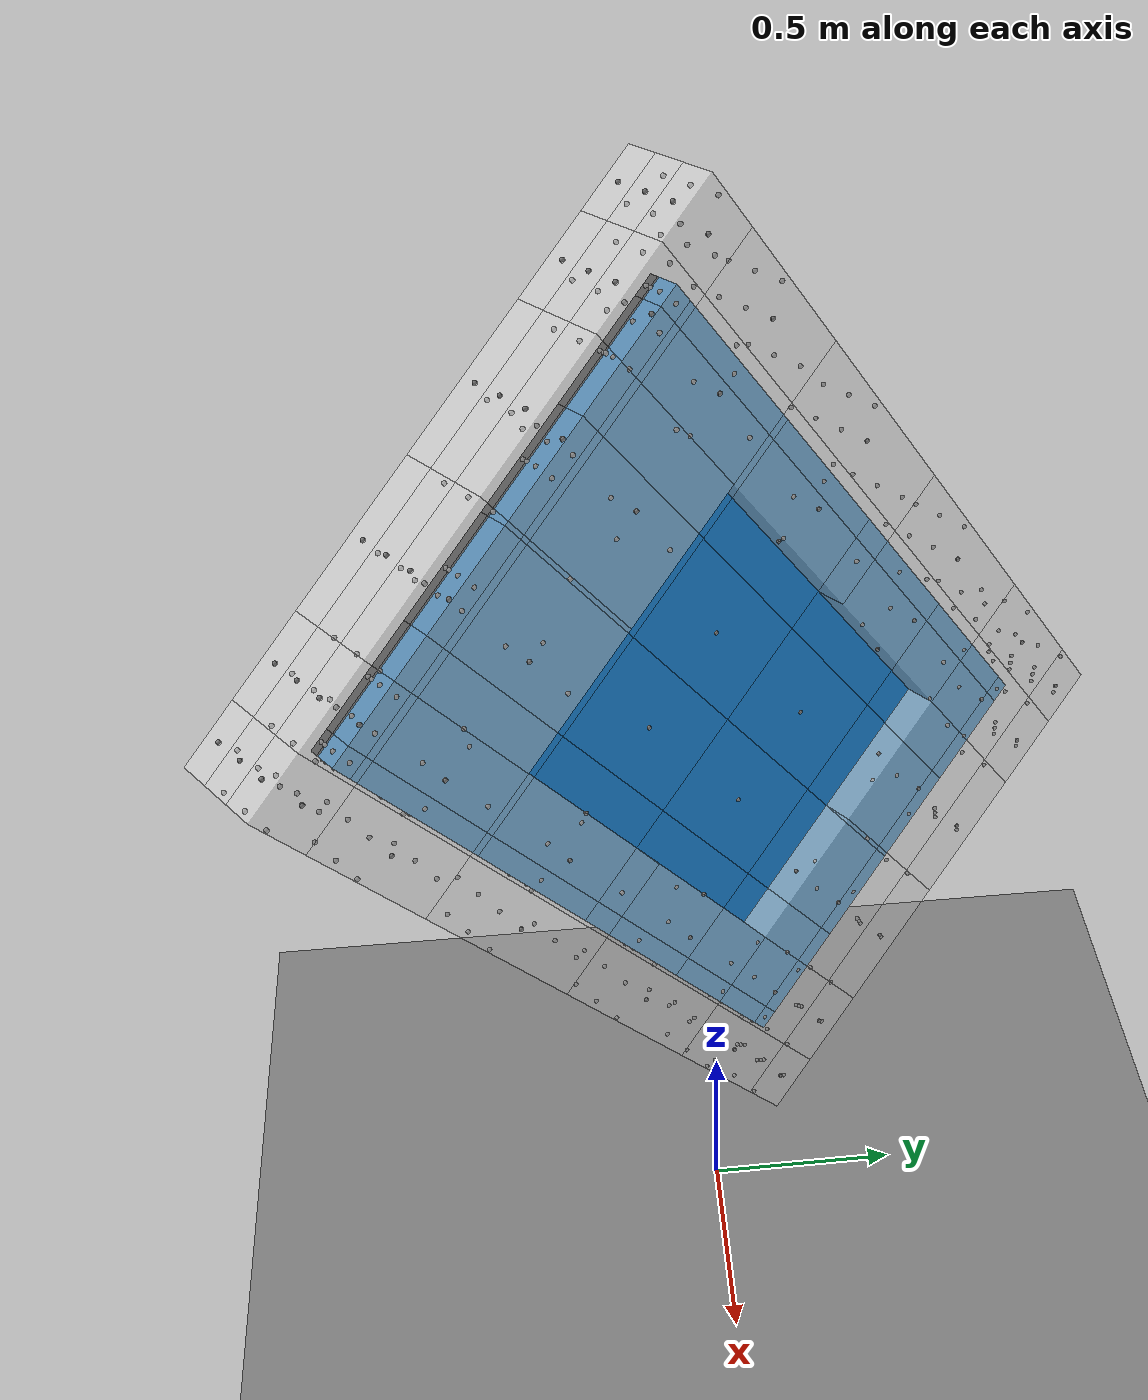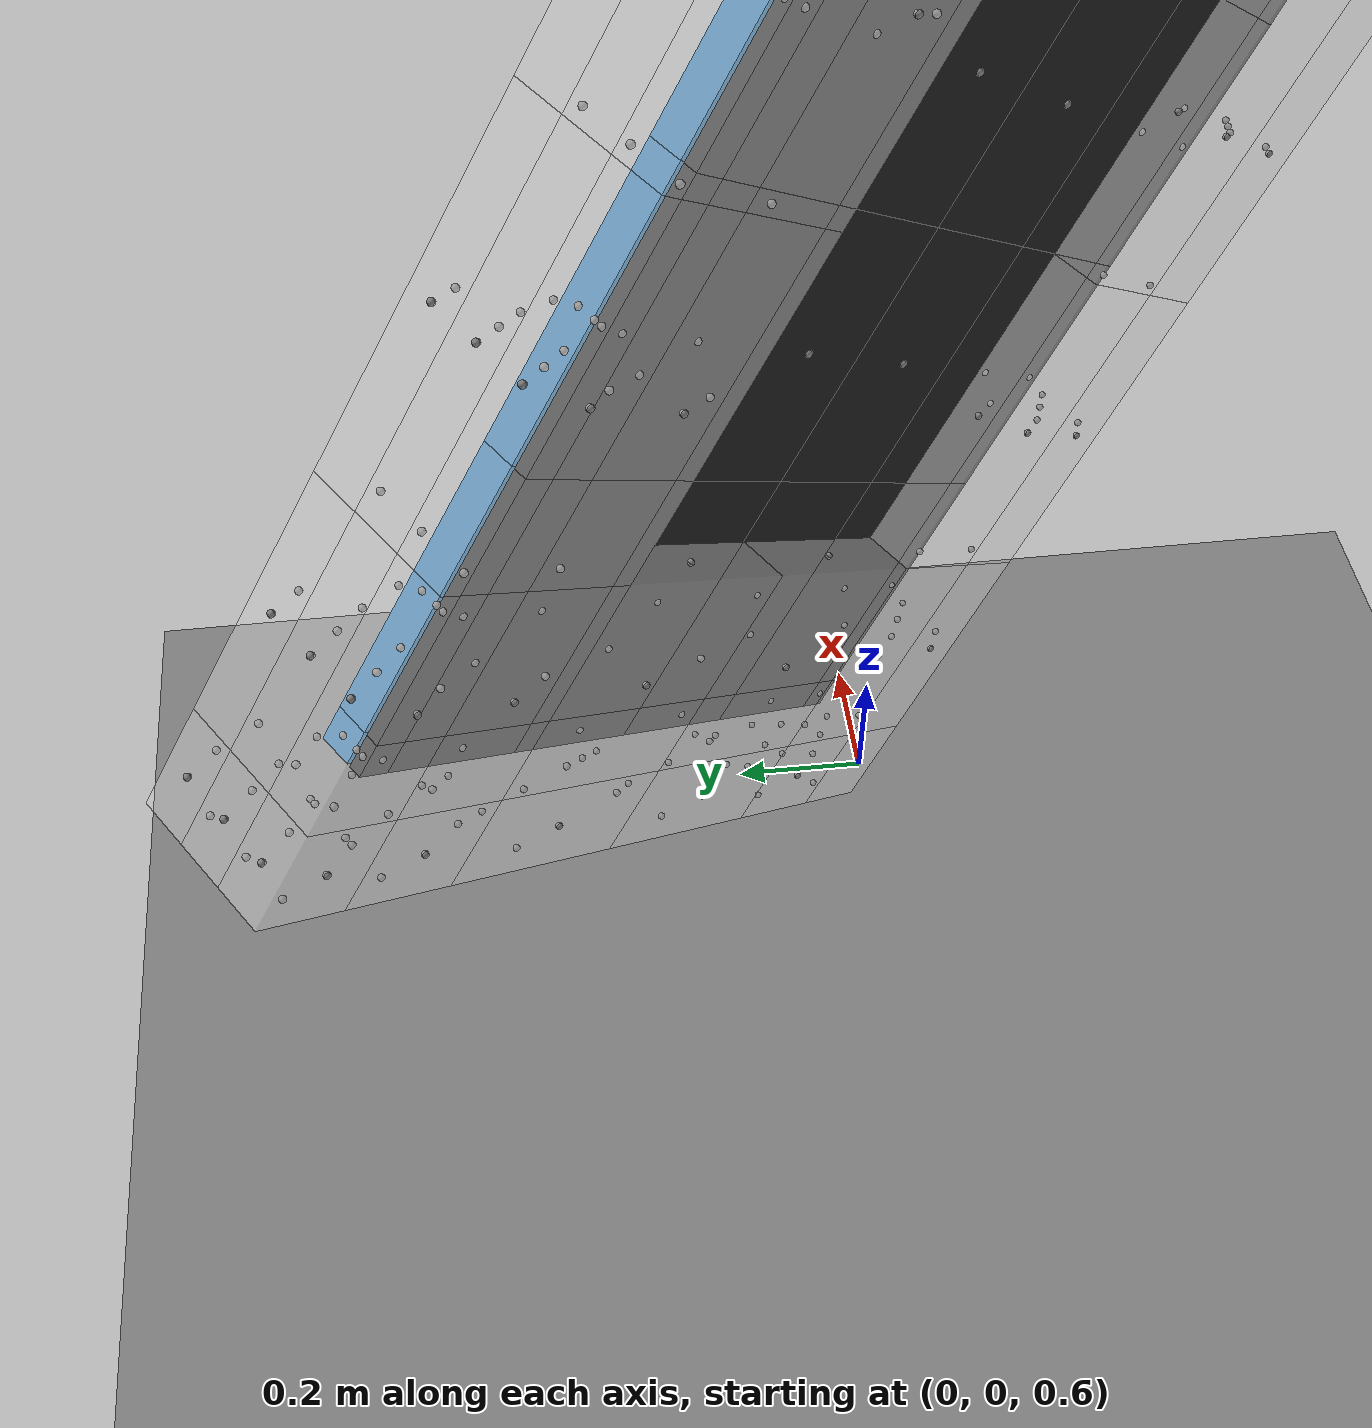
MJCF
<mujoco model="discrete_custom_box">
  <size memory="512M"/>
  <option integrator="Euler" timestep="0.001" iterations="50" noslip_iterations="0" tolerance="0.0001" impratio="1.0" gravity="0 0 -9.81" density="1.225" viscosity="1.81e-05">
    <flag contact="enable"/>
  </option>
  <visual>
    <headlight ambient="0.28 0.28 0.28" diffuse="0.56 0.56 0.56" specular="0.07 0.07 0.07"/>
    <map znear="0.01"/>
  </visual>
  <default>
    <joint armature="0.05" damping="1.0"/>
    <geom friction="0.8" solref="0.02 1.0" solimp="0.9 0.95 0.001"/>
  </default>
  <worldbody>
    <light pos="0 0 6" dir="0 0 -1" directional="false" diffuse="0.49 0.49 0.49" ambient="0.21 0.21 0.21" castshadow="true"/>
    <light pos="3 3 5" dir="-1 -1 -1" directional="false" diffuse="0.21 0.21 0.21" castshadow="false"/>
    <geom name="ground" type="plane" size="5 5 0.1" friction="0.02" contype="1" conaffinity="1" solref="0.005 2.0" solimp="0.9 0.999 0.001 0.5 2"/>
    <body name="BPackagingBox" pos="0.00000 0.00000 1.72704" axisangle="0.5735 -0.8192 0.0000 95.8469">
      <freejoint/>
      <geom type="box" size="0.001 0.001 0.001" mass="0.000021" rgba="0 0 0 0" contype="0" conaffinity="0" friction="0.8"/>
      <body name="BCushion">
        <body name="b_bcushion_0_0_0" pos="-0.91550 -0.61550 -0.07675">
          <joint type="slide" axis="1 0 0"/>
          <joint type="slide" axis="0 1 0"/>
          <joint type="slide" axis="0 0 1"/>
          <joint type="ball"/>
          <geom name="g_bcushion_0_0_0" type="box" size="0.07450 0.07450 0.03825" mass="0.004425" rgba="0.9 0.9 0.9 0.5" contype="2" conaffinity="29" friction="0.8" solref="0.1 2.0" solimp="0.95 0.999 0.001 0.5 2.0"/>
          <site name="s_BCushion_0_0_0_PX" pos="0.07450 0 0"/>
          <site name="s_BCushion_0_0_0_NX" pos="-0.07450 0 0"/>
          <site name="s_BCushion_0_0_0_PY" pos="0 0.07450 0"/>
          <site name="s_BCushion_0_0_0_NY" pos="0 -0.07450 0"/>
          <site name="s_BCushion_0_0_0_PZ" pos="0 0 0.03825"/>
          <site name="s_BCushion_0_0_0_NZ" pos="0 0 -0.03825"/>
        </body>
        <body name="b_bcushion_0_0_1" pos="-0.91550 -0.61550 0.00000">
          <joint type="slide" axis="1 0 0"/>
          <joint type="slide" axis="0 1 0"/>
          <joint type="slide" axis="0 0 1"/>
          <joint type="ball"/>
          <geom name="g_bcushion_0_0_1" type="box" size="0.07450 0.07450 0.03850" mass="0.004454" rgba="0.9 0.9 0.9 0.5" contype="2" conaffinity="29" friction="0.8" solref="0.1 2.0" solimp="0.95 0.999 0.001 0.5 2.0"/>
          <site name="s_BCushion_0_0_1_PX" pos="0.07450 0 0"/>
          <site name="s_BCushion_0_0_1_NX" pos="-0.07450 0 0"/>
          <site name="s_BCushion_0_0_1_PY" pos="0 0.07450 0"/>
          <site name="s_BCushion_0_0_1_NY" pos="0 -0.07450 0"/>
          <site name="s_BCushion_0_0_1_PZ" pos="0 0 0.03850"/>
          <site name="s_BCushion_0_0_1_NZ" pos="0 0 -0.03850"/>
        </body>
        <body name="b_bcushion_0_0_2" pos="-0.91550 -0.61550 0.07675">
          <joint type="slide" axis="1 0 0"/>
          <joint type="slide" axis="0 1 0"/>
          <joint type="slide" axis="0 0 1"/>
          <joint type="ball"/>
          <geom name="g_bcushion_0_0_2" type="box" size="0.07450 0.07450 0.03825" mass="0.004425" rgba="0.9 0.9 0.9 0.5" contype="2" conaffinity="29" friction="0.8" solref="0.1 2.0" solimp="0.95 0.999 0.001 0.5 2.0"/>
          <site name="s_BCushion_0_0_2_PX" pos="0.07450 0 0"/>
          <site name="s_BCushion_0_0_2_NX" pos="-0.07450 0 0"/>
          <site name="s_BCushion_0_0_2_PY" pos="0 0.07450 0"/>
          <site name="s_BCushion_0_0_2_NY" pos="0 -0.07450 0"/>
          <site name="s_BCushion_0_0_2_PZ" pos="0 0 0.03825"/>
          <site name="s_BCushion_0_0_2_NZ" pos="0 0 -0.03825"/>
        </body>
        <body name="b_bcushion_0_1_0" pos="-0.91550 -0.44300 -0.07675">
          <joint type="slide" axis="1 0 0"/>
          <joint type="slide" axis="0 1 0"/>
          <joint type="slide" axis="0 0 1"/>
          <joint type="ball"/>
          <geom name="g_bcushion_0_1_0" type="box" size="0.07450 0.09800 0.03825" mass="0.005821" rgba="0.9 0.9 0.9 0.5" contype="2" conaffinity="29" friction="0.8" solref="0.1 2.0" solimp="0.95 0.999 0.001 0.5 2.0"/>
          <site name="s_BCushion_0_1_0_PX" pos="0.07450 0 0"/>
          <site name="s_BCushion_0_1_0_NX" pos="-0.07450 0 0"/>
          <site name="s_BCushion_0_1_0_PY" pos="0 0.09800 0"/>
          <site name="s_BCushion_0_1_0_NY" pos="0 -0.09800 0"/>
          <site name="s_BCushion_0_1_0_PZ" pos="0 0 0.03825"/>
          <site name="s_BCushion_0_1_0_NZ" pos="0 0 -0.03825"/>
        </body>
        <body name="b_bcushion_0_1_1" pos="-0.91550 -0.44300 0.00000">
          <joint type="slide" axis="1 0 0"/>
          <joint type="slide" axis="0 1 0"/>
          <joint type="slide" axis="0 0 1"/>
          <joint type="ball"/>
          <geom name="g_bcushion_0_1_1" type="box" size="0.07450 0.09800 0.03850" mass="0.005859" rgba="0.9 0.9 0.9 0.5" contype="2" conaffinity="29" friction="0.8" solref="0.1 2.0" solimp="0.95 0.999 0.001 0.5 2.0"/>
          <site name="s_BCushion_0_1_1_PX" pos="0.07450 0 0"/>
          <site name="s_BCushion_0_1_1_NX" pos="-0.07450 0 0"/>
          <site name="s_BCushion_0_1_1_PY" pos="0 0.09800 0"/>
          <site name="s_BCushion_0_1_1_NY" pos="0 -0.09800 0"/>
          <site name="s_BCushion_0_1_1_PZ" pos="0 0 0.03850"/>
          <site name="s_BCushion_0_1_1_NZ" pos="0 0 -0.03850"/>
        </body>
        <body name="b_bcushion_0_1_2" pos="-0.91550 -0.44300 0.07675">
          <joint type="slide" axis="1 0 0"/>
          <joint type="slide" axis="0 1 0"/>
          <joint type="slide" axis="0 0 1"/>
          <joint type="ball"/>
          <geom name="g_bcushion_0_1_2" type="box" size="0.07450 0.09800 0.03825" mass="0.005821" rgba="0.9 0.9 0.9 0.5" contype="2" conaffinity="29" friction="0.8" solref="0.1 2.0" solimp="0.95 0.999 0.001 0.5 2.0"/>
          <site name="s_BCushion_0_1_2_PX" pos="0.07450 0 0"/>
          <site name="s_BCushion_0_1_2_NX" pos="-0.07450 0 0"/>
          <site name="s_BCushion_0_1_2_PY" pos="0 0.09800 0"/>
          <site name="s_BCushion_0_1_2_NY" pos="0 -0.09800 0"/>
          <site name="s_BCushion_0_1_2_PZ" pos="0 0 0.03825"/>
          <site name="s_BCushion_0_1_2_NZ" pos="0 0 -0.03825"/>
        </body>
        <body name="b_bcushion_0_2_0" pos="-0.91550 -0.17250 -0.07675">
          <joint type="slide" axis="1 0 0"/>
          <joint type="slide" axis="0 1 0"/>
          <joint type="slide" axis="0 0 1"/>
          <joint type="ball"/>
          <geom name="g_bcushion_0_2_0" type="box" size="0.07450 0.17250 0.03825" mass="0.010246" rgba="0.9 0.9 0.9 0.5" contype="2" conaffinity="29" friction="0.8" solref="0.1 2.0" solimp="0.95 0.999 0.001 0.5 2.0"/>
          <site name="s_BCushion_0_2_0_PX" pos="0.07450 0 0"/>
          <site name="s_BCushion_0_2_0_NX" pos="-0.07450 0 0"/>
          <site name="s_BCushion_0_2_0_PY" pos="0 0.17250 0"/>
          <site name="s_BCushion_0_2_0_NY" pos="0 -0.17250 0"/>
          <site name="s_BCushion_0_2_0_PZ" pos="0 0 0.03825"/>
          <site name="s_BCushion_0_2_0_NZ" pos="0 0 -0.03825"/>
        </body>
        <body name="b_bcushion_0_2_1" pos="-0.91550 -0.17250 0.00000">
          <joint type="slide" axis="1 0 0"/>
          <joint type="slide" axis="0 1 0"/>
          <joint type="slide" axis="0 0 1"/>
          <joint type="ball"/>
          <geom name="g_bcushion_0_2_1" type="box" size="0.07450 0.17250 0.03850" mass="0.010313" rgba="0.9 0.9 0.9 0.5" contype="2" conaffinity="29" friction="0.8" solref="0.1 2.0" solimp="0.95 0.999 0.001 0.5 2.0"/>
          <site name="s_BCushion_0_2_1_PX" pos="0.07450 0 0"/>
          <site name="s_BCushion_0_2_1_NX" pos="-0.07450 0 0"/>
          <site name="s_BCushion_0_2_1_PY" pos="0 0.17250 0"/>
          <site name="s_BCushion_0_2_1_NY" pos="0 -0.17250 0"/>
          <site name="s_BCushion_0_2_1_PZ" pos="0 0 0.03850"/>
          <site name="s_BCushion_0_2_1_NZ" pos="0 0 -0.03850"/>
        </body>
        <body name="b_bcushion_0_2_2" pos="-0.91550 -0.17250 0.07675">
          <joint type="slide" axis="1 0 0"/>
          <joint type="slide" axis="0 1 0"/>
          <joint type="slide" axis="0 0 1"/>
          <joint type="ball"/>
          <geom name="g_bcushion_0_2_2" type="box" size="0.07450 0.17250 0.03825" mass="0.010246" rgba="0.9 0.9 0.9 0.5" contype="2" conaffinity="29" friction="0.8" solref="0.1 2.0" solimp="0.95 0.999 0.001 0.5 2.0"/>
          <site name="s_BCushion_0_2_2_PX" pos="0.07450 0 0"/>
          <site name="s_BCushion_0_2_2_NX" pos="-0.07450 0 0"/>
          <site name="s_BCushion_0_2_2_PY" pos="0 0.17250 0"/>
          <site name="s_BCushion_0_2_2_NY" pos="0 -0.17250 0"/>
          <site name="s_BCushion_0_2_2_PZ" pos="0 0 0.03825"/>
          <site name="s_BCushion_0_2_2_NZ" pos="0 0 -0.03825"/>
        </body>
        <body name="b_bcushion_0_3_0" pos="-0.91550 0.17250 -0.07675">
          <joint type="slide" axis="1 0 0"/>
          <joint type="slide" axis="0 1 0"/>
          <joint type="slide" axis="0 0 1"/>
          <joint type="ball"/>
          <geom name="g_bcushion_0_3_0" type="box" size="0.07450 0.17250 0.03825" mass="0.010246" rgba="0.9 0.9 0.9 0.5" contype="2" conaffinity="29" friction="0.8" solref="0.1 2.0" solimp="0.95 0.999 0.001 0.5 2.0"/>
          <site name="s_BCushion_0_3_0_PX" pos="0.07450 0 0"/>
          <site name="s_BCushion_0_3_0_NX" pos="-0.07450 0 0"/>
          <site name="s_BCushion_0_3_0_PY" pos="0 0.17250 0"/>
          <site name="s_BCushion_0_3_0_NY" pos="0 -0.17250 0"/>
          <site name="s_BCushion_0_3_0_PZ" pos="0 0 0.03825"/>
          <site name="s_BCushion_0_3_0_NZ" pos="0 0 -0.03825"/>
        </body>
        <body name="b_bcushion_0_3_1" pos="-0.91550 0.17250 0.00000">
          <joint type="slide" axis="1 0 0"/>
          <joint type="slide" axis="0 1 0"/>
          <joint type="slide" axis="0 0 1"/>
          <joint type="ball"/>
          <geom name="g_bcushion_0_3_1" type="box" size="0.07450 0.17250 0.03850" mass="0.010313" rgba="0.9 0.9 0.9 0.5" contype="2" conaffinity="29" friction="0.8" solref="0.1 2.0" solimp="0.95 0.999 0.001 0.5 2.0"/>
          <site name="s_BCushion_0_3_1_PX" pos="0.07450 0 0"/>
          <site name="s_BCushion_0_3_1_NX" pos="-0.07450 0 0"/>
          <site name="s_BCushion_0_3_1_PY" pos="0 0.17250 0"/>
          <site name="s_BCushion_0_3_1_NY" pos="0 -0.17250 0"/>
          <site name="s_BCushion_0_3_1_PZ" pos="0 0 0.03850"/>
          <site name="s_BCushion_0_3_1_NZ" pos="0 0 -0.03850"/>
        </body>
        <body name="b_bcushion_0_3_2" pos="-0.91550 0.17250 0.07675">
          <joint type="slide" axis="1 0 0"/>
          <joint type="slide" axis="0 1 0"/>
          <joint type="slide" axis="0 0 1"/>
          <joint type="ball"/>
          <geom name="g_bcushion_0_3_2" type="box" size="0.07450 0.17250 0.03825" mass="0.010246" rgba="0.9 0.9 0.9 0.5" contype="2" conaffinity="29" friction="0.8" solref="0.1 2.0" solimp="0.95 0.999 0.001 0.5 2.0"/>
          <site name="s_BCushion_0_3_2_PX" pos="0.07450 0 0"/>
          <site name="s_BCushion_0_3_2_NX" pos="-0.07450 0 0"/>
          <site name="s_BCushion_0_3_2_PY" pos="0 0.17250 0"/>
          <site name="s_BCushion_0_3_2_NY" pos="0 -0.17250 0"/>
          <site name="s_BCushion_0_3_2_PZ" pos="0 0 0.03825"/>
          <site name="s_BCushion_0_3_2_NZ" pos="0 0 -0.03825"/>
        </body>
        <body name="b_bcushion_0_4_0" pos="-0.91550 0.44300 -0.07675">
          <joint type="slide" axis="1 0 0"/>
          <joint type="slide" axis="0 1 0"/>
          <joint type="slide" axis="0 0 1"/>
          <joint type="ball"/>
          <geom name="g_bcushion_0_4_0" type="box" size="0.07450 0.09800 0.03825" mass="0.005821" rgba="0.9 0.9 0.9 0.5" contype="2" conaffinity="29" friction="0.8" solref="0.1 2.0" solimp="0.95 0.999 0.001 0.5 2.0"/>
          <site name="s_BCushion_0_4_0_PX" pos="0.07450 0 0"/>
          <site name="s_BCushion_0_4_0_NX" pos="-0.07450 0 0"/>
          <site name="s_BCushion_0_4_0_PY" pos="0 0.09800 0"/>
          <site name="s_BCushion_0_4_0_NY" pos="0 -0.09800 0"/>
          <site name="s_BCushion_0_4_0_PZ" pos="0 0 0.03825"/>
          <site name="s_BCushion_0_4_0_NZ" pos="0 0 -0.03825"/>
        </body>
        <body name="b_bcushion_0_4_1" pos="-0.91550 0.44300 0.00000">
          <joint type="slide" axis="1 0 0"/>
          <joint type="slide" axis="0 1 0"/>
          <joint type="slide" axis="0 0 1"/>
          <joint type="ball"/>
          <geom name="g_bcushion_0_4_1" type="box" size="0.07450 0.09800 0.03850" mass="0.005859" rgba="0.9 0.9 0.9 0.5" contype="2" conaffinity="29" friction="0.8" solref="0.1 2.0" solimp="0.95 0.999 0.001 0.5 2.0"/>
          <site name="s_BCushion_0_4_1_PX" pos="0.07450 0 0"/>
          <site name="s_BCushion_0_4_1_NX" pos="-0.07450 0 0"/>
          <site name="s_BCushion_0_4_1_PY" pos="0 0.09800 0"/>
          <site name="s_BCushion_0_4_1_NY" pos="0 -0.09800 0"/>
          <site name="s_BCushion_0_4_1_PZ" pos="0 0 0.03850"/>
          <site name="s_BCushion_0_4_1_NZ" pos="0 0 -0.03850"/>
        </body>
        <body name="b_bcushion_0_4_2" pos="-0.91550 0.44300 0.07675">
          <joint type="slide" axis="1 0 0"/>
          <joint type="slide" axis="0 1 0"/>
          <joint type="slide" axis="0 0 1"/>
          <joint type="ball"/>
          <geom name="g_bcushion_0_4_2" type="box" size="0.07450 0.09800 0.03825" mass="0.005821" rgba="0.9 0.9 0.9 0.5" contype="2" conaffinity="29" friction="0.8" solref="0.1 2.0" solimp="0.95 0.999 0.001 0.5 2.0"/>
          <site name="s_BCushion_0_4_2_PX" pos="0.07450 0 0"/>
          <site name="s_BCushion_0_4_2_NX" pos="-0.07450 0 0"/>
          <site name="s_BCushion_0_4_2_PY" pos="0 0.09800 0"/>
          <site name="s_BCushion_0_4_2_NY" pos="0 -0.09800 0"/>
          <site name="s_BCushion_0_4_2_PZ" pos="0 0 0.03825"/>
          <site name="s_BCushion_0_4_2_NZ" pos="0 0 -0.03825"/>
        </body>
        <body name="b_bcushion_0_5_0" pos="-0.91550 0.61550 -0.07675">
          <joint type="slide" axis="1 0 0"/>
          <joint type="slide" axis="0 1 0"/>
          <joint type="slide" axis="0 0 1"/>
          <joint type="ball"/>
          <geom name="g_bcushion_0_5_0" type="box" size="0.07450 0.07450 0.03825" mass="0.004425" rgba="0.9 0.9 0.9 0.5" contype="2" conaffinity="29" friction="0.8" solref="0.1 2.0" solimp="0.95 0.999 0.001 0.5 2.0"/>
          <site name="s_BCushion_0_5_0_PX" pos="0.07450 0 0"/>
          <site name="s_BCushion_0_5_0_NX" pos="-0.07450 0 0"/>
          <site name="s_BCushion_0_5_0_PY" pos="0 0.07450 0"/>
          <site name="s_BCushion_0_5_0_NY" pos="0 -0.07450 0"/>
          <site name="s_BCushion_0_5_0_PZ" pos="0 0 0.03825"/>
          <site name="s_BCushion_0_5_0_NZ" pos="0 0 -0.03825"/>
        </body>
        <body name="b_bcushion_0_5_1" pos="-0.91550 0.61550 0.00000">
          <joint type="slide" axis="1 0 0"/>
          <joint type="slide" axis="0 1 0"/>
          <joint type="slide" axis="0 0 1"/>
          <joint type="ball"/>
          <geom name="g_bcushion_0_5_1" type="box" size="0.07450 0.07450 0.03850" mass="0.004454" rgba="0.9 0.9 0.9 0.5" contype="2" conaffinity="29" friction="0.8" solref="0.1 2.0" solimp="0.95 0.999 0.001 0.5 2.0"/>
          <site name="s_BCushion_0_5_1_PX" pos="0.07450 0 0"/>
          <site name="s_BCushion_0_5_1_NX" pos="-0.07450 0 0"/>
          <site name="s_BCushion_0_5_1_PY" pos="0 0.07450 0"/>
          <site name="s_BCushion_0_5_1_NY" pos="0 -0.07450 0"/>
          <site name="s_BCushion_0_5_1_PZ" pos="0 0 0.03850"/>
          <site name="s_BCushion_0_5_1_NZ" pos="0 0 -0.03850"/>
        </body>
        <body name="b_bcushion_0_5_2" pos="-0.91550 0.61550 0.07675">
          <joint type="slide" axis="1 0 0"/>
          <joint type="slide" axis="0 1 0"/>
          <joint type="slide" axis="0 0 1"/>
          <joint type="ball"/>
          <geom name="g_bcushion_0_5_2" type="box" size="0.07450 0.07450 0.03825" mass="0.004425" rgba="0.9 0.9 0.9 0.5" contype="2" conaffinity="29" friction="0.8" solref="0.1 2.0" solimp="0.95 0.999 0.001 0.5 2.0"/>
          <site name="s_BCushion_0_5_2_PX" pos="0.07450 0 0"/>
          <site name="s_BCushion_0_5_2_NX" pos="-0.07450 0 0"/>
          <site name="s_BCushion_0_5_2_PY" pos="0 0.07450 0"/>
          <site name="s_BCushion_0_5_2_NY" pos="0 -0.07450 0"/>
          <site name="s_BCushion_0_5_2_PZ" pos="0 0 0.03825"/>
          <site name="s_BCushion_0_5_2_NZ" pos="0 0 -0.03825"/>
        </body>
        <body name="b_bcushion_1_0_0" pos="-0.66800 -0.61550 -0.07675">
          <joint type="slide" axis="1 0 0"/>
          <joint type="slide" axis="0 1 0"/>
          <joint type="slide" axis="0 0 1"/>
          <joint type="ball"/>
          <geom name="g_bcushion_1_0_0" type="box" size="0.17300 0.07450 0.03825" mass="0.010276" rgba="0.9 0.9 0.9 0.5" contype="2" conaffinity="29" friction="0.8" solref="0.1 2.0" solimp="0.95 0.999 0.001 0.5 2.0"/>
          <site name="s_BCushion_1_0_0_PX" pos="0.17300 0 0"/>
          <site name="s_BCushion_1_0_0_NX" pos="-0.17300 0 0"/>
          <site name="s_BCushion_1_0_0_PY" pos="0 0.07450 0"/>
          <site name="s_BCushion_1_0_0_NY" pos="0 -0.07450 0"/>
          <site name="s_BCushion_1_0_0_PZ" pos="0 0 0.03825"/>
          <site name="s_BCushion_1_0_0_NZ" pos="0 0 -0.03825"/>
        </body>
        <body name="b_bcushion_1_0_1" pos="-0.66800 -0.61550 0.00000">
          <joint type="slide" axis="1 0 0"/>
          <joint type="slide" axis="0 1 0"/>
          <joint type="slide" axis="0 0 1"/>
          <joint type="ball"/>
          <geom name="g_bcushion_1_0_1" type="box" size="0.17300 0.07450 0.03850" mass="0.010343" rgba="0.9 0.9 0.9 0.5" contype="2" conaffinity="29" friction="0.8" solref="0.1 2.0" solimp="0.95 0.999 0.001 0.5 2.0"/>
          <site name="s_BCushion_1_0_1_PX" pos="0.17300 0 0"/>
          <site name="s_BCushion_1_0_1_NX" pos="-0.17300 0 0"/>
          <site name="s_BCushion_1_0_1_PY" pos="0 0.07450 0"/>
          <site name="s_BCushion_1_0_1_NY" pos="0 -0.07450 0"/>
          <site name="s_BCushion_1_0_1_PZ" pos="0 0 0.03850"/>
          <site name="s_BCushion_1_0_1_NZ" pos="0 0 -0.03850"/>
        </body>
        <body name="b_bcushion_1_0_2" pos="-0.66800 -0.61550 0.07675">
          <joint type="slide" axis="1 0 0"/>
          <joint type="slide" axis="0 1 0"/>
          <joint type="slide" axis="0 0 1"/>
          <joint type="ball"/>
          <geom name="g_bcushion_1_0_2" type="box" size="0.17300 0.07450 0.03825" mass="0.010276" rgba="0.9 0.9 0.9 0.5" contype="2" conaffinity="29" friction="0.8" solref="0.1 2.0" solimp="0.95 0.999 0.001 0.5 2.0"/>
          <site name="s_BCushion_1_0_2_PX" pos="0.17300 0 0"/>
          <site name="s_BCushion_1_0_2_NX" pos="-0.17300 0 0"/>
          <site name="s_BCushion_1_0_2_PY" pos="0 0.07450 0"/>
          <site name="s_BCushion_1_0_2_NY" pos="0 -0.07450 0"/>
          <site name="s_BCushion_1_0_2_PZ" pos="0 0 0.03825"/>
          <site name="s_BCushion_1_0_2_NZ" pos="0 0 -0.03825"/>
        </body>
        <body name="b_bcushion_1_1_0" pos="-0.66800 -0.44300 -0.07675">
          <joint type="slide" axis="1 0 0"/>
          <joint type="slide" axis="0 1 0"/>
          <joint type="slide" axis="0 0 1"/>
          <joint type="ball"/>
          <geom name="g_bcushion_1_1_0" type="box" size="0.17300 0.09800 0.03825" mass="0.013517" rgba="0.9 0.9 0.9 0.5" contype="2" conaffinity="29" friction="0.8" solref="0.1 2.0" solimp="0.95 0.999 0.001 0.5 2.0"/>
          <site name="s_BCushion_1_1_0_PX" pos="0.17300 0 0"/>
          <site name="s_BCushion_1_1_0_NX" pos="-0.17300 0 0"/>
          <site name="s_BCushion_1_1_0_PY" pos="0 0.09800 0"/>
          <site name="s_BCushion_1_1_0_NY" pos="0 -0.09800 0"/>
          <site name="s_BCushion_1_1_0_PZ" pos="0 0 0.03825"/>
          <site name="s_BCushion_1_1_0_NZ" pos="0 0 -0.03825"/>
        </body>
        <body name="b_bcushion_1_1_2" pos="-0.66800 -0.44300 0.07675">
          <joint type="slide" axis="1 0 0"/>
          <joint type="slide" axis="0 1 0"/>
          <joint type="slide" axis="0 0 1"/>
          <joint type="ball"/>
          <geom name="g_bcushion_1_1_2" type="box" size="0.17300 0.09800 0.03825" mass="0.013517" rgba="0.9 0.9 0.9 0.5" contype="2" conaffinity="29" friction="0.8" solref="0.1 2.0" solimp="0.95 0.999 0.001 0.5 2.0"/>
          <site name="s_BCushion_1_1_2_PX" pos="0.17300 0 0"/>
          <site name="s_BCushion_1_1_2_NX" pos="-0.17300 0 0"/>
          <site name="s_BCushion_1_1_2_PY" pos="0 0.09800 0"/>
          <site name="s_BCushion_1_1_2_NY" pos="0 -0.09800 0"/>
          <site name="s_BCushion_1_1_2_PZ" pos="0 0 0.03825"/>
          <site name="s_BCushion_1_1_2_NZ" pos="0 0 -0.03825"/>
        </body>
        <body name="b_bcushion_1_2_0" pos="-0.66800 -0.17250 -0.07675">
          <joint type="slide" axis="1 0 0"/>
          <joint type="slide" axis="0 1 0"/>
          <joint type="slide" axis="0 0 1"/>
          <joint type="ball"/>
          <geom name="g_bcushion_1_2_0" type="box" size="0.17300 0.17250 0.03825" mass="0.023793" rgba="0.9 0.9 0.9 0.5" contype="2" conaffinity="29" friction="0.8" solref="0.1 2.0" solimp="0.95 0.999 0.001 0.5 2.0"/>
          <site name="s_BCushion_1_2_0_PX" pos="0.17300 0 0"/>
          <site name="s_BCushion_1_2_0_NX" pos="-0.17300 0 0"/>
          <site name="s_BCushion_1_2_0_PY" pos="0 0.17250 0"/>
          <site name="s_BCushion_1_2_0_NY" pos="0 -0.17250 0"/>
          <site name="s_BCushion_1_2_0_PZ" pos="0 0 0.03825"/>
          <site name="s_BCushion_1_2_0_NZ" pos="0 0 -0.03825"/>
        </body>
        <body name="b_bcushion_1_2_2" pos="-0.66800 -0.17250 0.07675">
          <joint type="slide" axis="1 0 0"/>
          <joint type="slide" axis="0 1 0"/>
          <joint type="slide" axis="0 0 1"/>
          <joint type="ball"/>
          <geom name="g_bcushion_1_2_2" type="box" size="0.17300 0.17250 0.03825" mass="0.023793" rgba="0.9 0.9 0.9 0.5" contype="2" conaffinity="29" friction="0.8" solref="0.1 2.0" solimp="0.95 0.999 0.001 0.5 2.0"/>
          <site name="s_BCushion_1_2_2_PX" pos="0.17300 0 0"/>
          <site name="s_BCushion_1_2_2_NX" pos="-0.17300 0 0"/>
          <site name="s_BCushion_1_2_2_PY" pos="0 0.17250 0"/>
          <site name="s_BCushion_1_2_2_NY" pos="0 -0.17250 0"/>
          <site name="s_BCushion_1_2_2_PZ" pos="0 0 0.03825"/>
          <site name="s_BCushion_1_2_2_NZ" pos="0 0 -0.03825"/>
        </body>
        <body name="b_bcushion_1_3_0" pos="-0.66800 0.17250 -0.07675">
          <joint type="slide" axis="1 0 0"/>
          <joint type="slide" axis="0 1 0"/>
          <joint type="slide" axis="0 0 1"/>
          <joint type="ball"/>
          <geom name="g_bcushion_1_3_0" type="box" size="0.17300 0.17250 0.03825" mass="0.023793" rgba="0.9 0.9 0.9 0.5" contype="2" conaffinity="29" friction="0.8" solref="0.1 2.0" solimp="0.95 0.999 0.001 0.5 2.0"/>
          <site name="s_BCushion_1_3_0_PX" pos="0.17300 0 0"/>
          <site name="s_BCushion_1_3_0_NX" pos="-0.17300 0 0"/>
          <site name="s_BCushion_1_3_0_PY" pos="0 0.17250 0"/>
          <site name="s_BCushion_1_3_0_NY" pos="0 -0.17250 0"/>
          <site name="s_BCushion_1_3_0_PZ" pos="0 0 0.03825"/>
          <site name="s_BCushion_1_3_0_NZ" pos="0 0 -0.03825"/>
        </body>
        <body name="b_bcushion_1_3_2" pos="-0.66800 0.17250 0.07675">
          <joint type="slide" axis="1 0 0"/>
          <joint type="slide" axis="0 1 0"/>
          <joint type="slide" axis="0 0 1"/>
          <joint type="ball"/>
          <geom name="g_bcushion_1_3_2" type="box" size="0.17300 0.17250 0.03825" mass="0.023793" rgba="0.9 0.9 0.9 0.5" contype="2" conaffinity="29" friction="0.8" solref="0.1 2.0" solimp="0.95 0.999 0.001 0.5 2.0"/>
          <site name="s_BCushion_1_3_2_PX" pos="0.17300 0 0"/>
          <site name="s_BCushion_1_3_2_NX" pos="-0.17300 0 0"/>
          <site name="s_BCushion_1_3_2_PY" pos="0 0.17250 0"/>
          <site name="s_BCushion_1_3_2_NY" pos="0 -0.17250 0"/>
          <site name="s_BCushion_1_3_2_PZ" pos="0 0 0.03825"/>
          <site name="s_BCushion_1_3_2_NZ" pos="0 0 -0.03825"/>
        </body>
        <body name="b_bcushion_1_4_0" pos="-0.66800 0.44300 -0.07675">
          <joint type="slide" axis="1 0 0"/>
          <joint type="slide" axis="0 1 0"/>
          <joint type="slide" axis="0 0 1"/>
          <joint type="ball"/>
          <geom name="g_bcushion_1_4_0" type="box" size="0.17300 0.09800 0.03825" mass="0.013517" rgba="0.9 0.9 0.9 0.5" contype="2" conaffinity="29" friction="0.8" solref="0.1 2.0" solimp="0.95 0.999 0.001 0.5 2.0"/>
          <site name="s_BCushion_1_4_0_PX" pos="0.17300 0 0"/>
          <site name="s_BCushion_1_4_0_NX" pos="-0.17300 0 0"/>
          <site name="s_BCushion_1_4_0_PY" pos="0 0.09800 0"/>
          <site name="s_BCushion_1_4_0_NY" pos="0 -0.09800 0"/>
          <site name="s_BCushion_1_4_0_PZ" pos="0 0 0.03825"/>
          <site name="s_BCushion_1_4_0_NZ" pos="0 0 -0.03825"/>
        </body>
        <body name="b_bcushion_1_4_2" pos="-0.66800 0.44300 0.07675">
          <joint type="slide" axis="1 0 0"/>
          <joint type="slide" axis="0 1 0"/>
          <joint type="slide" axis="0 0 1"/>
          <joint type="ball"/>
          <geom name="g_bcushion_1_4_2" type="box" size="0.17300 0.09800 0.03825" mass="0.013517" rgba="0.9 0.9 0.9 0.5" contype="2" conaffinity="29" friction="0.8" solref="0.1 2.0" solimp="0.95 0.999 0.001 0.5 2.0"/>
          <site name="s_BCushion_1_4_2_PX" pos="0.17300 0 0"/>
          <site name="s_BCushion_1_4_2_NX" pos="-0.17300 0 0"/>
          <site name="s_BCushion_1_4_2_PY" pos="0 0.09800 0"/>
          <site name="s_BCushion_1_4_2_NY" pos="0 -0.09800 0"/>
          <site name="s_BCushion_1_4_2_PZ" pos="0 0 0.03825"/>
          <site name="s_BCushion_1_4_2_NZ" pos="0 0 -0.03825"/>
        </body>
        <body name="b_bcushion_1_5_0" pos="-0.66800 0.61550 -0.07675">
          <joint type="slide" axis="1 0 0"/>
          <joint type="slide" axis="0 1 0"/>
          <joint type="slide" axis="0 0 1"/>
          <joint type="ball"/>
          <geom name="g_bcushion_1_5_0" type="box" size="0.17300 0.07450 0.03825" mass="0.010276" rgba="0.9 0.9 0.9 0.5" contype="2" conaffinity="29" friction="0.8" solref="0.1 2.0" solimp="0.95 0.999 0.001 0.5 2.0"/>
          <site name="s_BCushion_1_5_0_PX" pos="0.17300 0 0"/>
          <site name="s_BCushion_1_5_0_NX" pos="-0.17300 0 0"/>
          <site name="s_BCushion_1_5_0_PY" pos="0 0.07450 0"/>
          <site name="s_BCushion_1_5_0_NY" pos="0 -0.07450 0"/>
          <site name="s_BCushion_1_5_0_PZ" pos="0 0 0.03825"/>
          <site name="s_BCushion_1_5_0_NZ" pos="0 0 -0.03825"/>
        </body>
        <body name="b_bcushion_1_5_1" pos="-0.66800 0.61550 0.00000">
          <joint type="slide" axis="1 0 0"/>
          <joint type="slide" axis="0 1 0"/>
          <joint type="slide" axis="0 0 1"/>
          <joint type="ball"/>
          <geom name="g_bcushion_1_5_1" type="box" size="0.17300 0.07450 0.03850" mass="0.010343" rgba="0.9 0.9 0.9 0.5" contype="2" conaffinity="29" friction="0.8" solref="0.1 2.0" solimp="0.95 0.999 0.001 0.5 2.0"/>
          <site name="s_BCushion_1_5_1_PX" pos="0.17300 0 0"/>
          <site name="s_BCushion_1_5_1_NX" pos="-0.17300 0 0"/>
          <site name="s_BCushion_1_5_1_PY" pos="0 0.07450 0"/>
          <site name="s_BCushion_1_5_1_NY" pos="0 -0.07450 0"/>
          <site name="s_BCushion_1_5_1_PZ" pos="0 0 0.03850"/>
          <site name="s_BCushion_1_5_1_NZ" pos="0 0 -0.03850"/>
        </body>
        <body name="b_bcushion_1_5_2" pos="-0.66800 0.61550 0.07675">
          <joint type="slide" axis="1 0 0"/>
          <joint type="slide" axis="0 1 0"/>
          <joint type="slide" axis="0 0 1"/>
          <joint type="ball"/>
          <geom name="g_bcushion_1_5_2" type="box" size="0.17300 0.07450 0.03825" mass="0.010276" rgba="0.9 0.9 0.9 0.5" contype="2" conaffinity="29" friction="0.8" solref="0.1 2.0" solimp="0.95 0.999 0.001 0.5 2.0"/>
          <site name="s_BCushion_1_5_2_PX" pos="0.17300 0 0"/>
          <site name="s_BCushion_1_5_2_NX" pos="-0.17300 0 0"/>
          <site name="s_BCushion_1_5_2_PY" pos="0 0.07450 0"/>
          <site name="s_BCushion_1_5_2_NY" pos="0 -0.07450 0"/>
          <site name="s_BCushion_1_5_2_PZ" pos="0 0 0.03825"/>
          <site name="s_BCushion_1_5_2_NZ" pos="0 0 -0.03825"/>
        </body>
        <body name="b_bcushion_2_0_0" pos="-0.24750 -0.61550 -0.07675">
          <joint type="slide" axis="1 0 0"/>
          <joint type="slide" axis="0 1 0"/>
          <joint type="slide" axis="0 0 1"/>
          <joint type="ball"/>
          <geom name="g_bcushion_2_0_0" type="box" size="0.24750 0.07450 0.03825" mass="0.014701" rgba="0.9 0.9 0.9 0.5" contype="2" conaffinity="29" friction="0.8" solref="0.1 2.0" solimp="0.95 0.999 0.001 0.5 2.0"/>
          <site name="s_BCushion_2_0_0_PX" pos="0.24750 0 0"/>
          <site name="s_BCushion_2_0_0_NX" pos="-0.24750 0 0"/>
          <site name="s_BCushion_2_0_0_PY" pos="0 0.07450 0"/>
          <site name="s_BCushion_2_0_0_NY" pos="0 -0.07450 0"/>
          <site name="s_BCushion_2_0_0_PZ" pos="0 0 0.03825"/>
          <site name="s_BCushion_2_0_0_NZ" pos="0 0 -0.03825"/>
        </body>
        <body name="b_bcushion_2_0_1" pos="-0.24750 -0.61550 0.00000">
          <joint type="slide" axis="1 0 0"/>
          <joint type="slide" axis="0 1 0"/>
          <joint type="slide" axis="0 0 1"/>
          <joint type="ball"/>
          <geom name="g_bcushion_2_0_1" type="box" size="0.24750 0.07450 0.03850" mass="0.014797" rgba="0.9 0.9 0.9 0.5" contype="2" conaffinity="29" friction="0.8" solref="0.1 2.0" solimp="0.95 0.999 0.001 0.5 2.0"/>
          <site name="s_BCushion_2_0_1_PX" pos="0.24750 0 0"/>
          <site name="s_BCushion_2_0_1_NX" pos="-0.24750 0 0"/>
          <site name="s_BCushion_2_0_1_PY" pos="0 0.07450 0"/>
          <site name="s_BCushion_2_0_1_NY" pos="0 -0.07450 0"/>
          <site name="s_BCushion_2_0_1_PZ" pos="0 0 0.03850"/>
          <site name="s_BCushion_2_0_1_NZ" pos="0 0 -0.03850"/>
        </body>
        <body name="b_bcushion_2_0_2" pos="-0.24750 -0.61550 0.07675">
          <joint type="slide" axis="1 0 0"/>
          <joint type="slide" axis="0 1 0"/>
          <joint type="slide" axis="0 0 1"/>
          <joint type="ball"/>
          <geom name="g_bcushion_2_0_2" type="box" size="0.24750 0.07450 0.03825" mass="0.014701" rgba="0.9 0.9 0.9 0.5" contype="2" conaffinity="29" friction="0.8" solref="0.1 2.0" solimp="0.95 0.999 0.001 0.5 2.0"/>
          <site name="s_BCushion_2_0_2_PX" pos="0.24750 0 0"/>
          <site name="s_BCushion_2_0_2_NX" pos="-0.24750 0 0"/>
          <site name="s_BCushion_2_0_2_PY" pos="0 0.07450 0"/>
          <site name="s_BCushion_2_0_2_NY" pos="0 -0.07450 0"/>
          <site name="s_BCushion_2_0_2_PZ" pos="0 0 0.03825"/>
          <site name="s_BCushion_2_0_2_NZ" pos="0 0 -0.03825"/>
        </body>
        <body name="b_bcushion_2_1_0" pos="-0.24750 -0.44300 -0.07675">
          <joint type="slide" axis="1 0 0"/>
          <joint type="slide" axis="0 1 0"/>
          <joint type="slide" axis="0 0 1"/>
          <joint type="ball"/>
          <geom name="g_bcushion_2_1_0" type="box" size="0.24750 0.09800 0.03825" mass="0.019338" rgba="0.9 0.9 0.9 0.5" contype="2" conaffinity="29" friction="0.8" solref="0.1 2.0" solimp="0.95 0.999 0.001 0.5 2.0"/>
          <site name="s_BCushion_2_1_0_PX" pos="0.24750 0 0"/>
          <site name="s_BCushion_2_1_0_NX" pos="-0.24750 0 0"/>
          <site name="s_BCushion_2_1_0_PY" pos="0 0.09800 0"/>
          <site name="s_BCushion_2_1_0_NY" pos="0 -0.09800 0"/>
          <site name="s_BCushion_2_1_0_PZ" pos="0 0 0.03825"/>
          <site name="s_BCushion_2_1_0_NZ" pos="0 0 -0.03825"/>
        </body>
        <body name="b_bcushion_2_1_2" pos="-0.24750 -0.44300 0.07675">
          <joint type="slide" axis="1 0 0"/>
          <joint type="slide" axis="0 1 0"/>
          <joint type="slide" axis="0 0 1"/>
          <joint type="ball"/>
          <geom name="g_bcushion_2_1_2" type="box" size="0.24750 0.09800 0.03825" mass="0.019338" rgba="0.9 0.9 0.9 0.5" contype="2" conaffinity="29" friction="0.8" solref="0.1 2.0" solimp="0.95 0.999 0.001 0.5 2.0"/>
          <site name="s_BCushion_2_1_2_PX" pos="0.24750 0 0"/>
          <site name="s_BCushion_2_1_2_NX" pos="-0.24750 0 0"/>
          <site name="s_BCushion_2_1_2_PY" pos="0 0.09800 0"/>
          <site name="s_BCushion_2_1_2_NY" pos="0 -0.09800 0"/>
          <site name="s_BCushion_2_1_2_PZ" pos="0 0 0.03825"/>
          <site name="s_BCushion_2_1_2_NZ" pos="0 0 -0.03825"/>
        </body>
        <body name="b_bcushion_2_4_0" pos="-0.24750 0.44300 -0.07675">
          <joint type="slide" axis="1 0 0"/>
          <joint type="slide" axis="0 1 0"/>
          <joint type="slide" axis="0 0 1"/>
          <joint type="ball"/>
          <geom name="g_bcushion_2_4_0" type="box" size="0.24750 0.09800 0.03825" mass="0.019338" rgba="0.9 0.9 0.9 0.5" contype="2" conaffinity="29" friction="0.8" solref="0.1 2.0" solimp="0.95 0.999 0.001 0.5 2.0"/>
          <site name="s_BCushion_2_4_0_PX" pos="0.24750 0 0"/>
          <site name="s_BCushion_2_4_0_NX" pos="-0.24750 0 0"/>
          <site name="s_BCushion_2_4_0_PY" pos="0 0.09800 0"/>
          <site name="s_BCushion_2_4_0_NY" pos="0 -0.09800 0"/>
          <site name="s_BCushion_2_4_0_PZ" pos="0 0 0.03825"/>
          <site name="s_BCushion_2_4_0_NZ" pos="0 0 -0.03825"/>
        </body>
        <body name="b_bcushion_2_4_2" pos="-0.24750 0.44300 0.07675">
          <joint type="slide" axis="1 0 0"/>
          <joint type="slide" axis="0 1 0"/>
          <joint type="slide" axis="0 0 1"/>
          <joint type="ball"/>
          <geom name="g_bcushion_2_4_2" type="box" size="0.24750 0.09800 0.03825" mass="0.019338" rgba="0.9 0.9 0.9 0.5" contype="2" conaffinity="29" friction="0.8" solref="0.1 2.0" solimp="0.95 0.999 0.001 0.5 2.0"/>
          <site name="s_BCushion_2_4_2_PX" pos="0.24750 0 0"/>
          <site name="s_BCushion_2_4_2_NX" pos="-0.24750 0 0"/>
          <site name="s_BCushion_2_4_2_PY" pos="0 0.09800 0"/>
          <site name="s_BCushion_2_4_2_NY" pos="0 -0.09800 0"/>
          <site name="s_BCushion_2_4_2_PZ" pos="0 0 0.03825"/>
          <site name="s_BCushion_2_4_2_NZ" pos="0 0 -0.03825"/>
        </body>
        <body name="b_bcushion_2_5_0" pos="-0.24750 0.61550 -0.07675">
          <joint type="slide" axis="1 0 0"/>
          <joint type="slide" axis="0 1 0"/>
          <joint type="slide" axis="0 0 1"/>
          <joint type="ball"/>
          <geom name="g_bcushion_2_5_0" type="box" size="0.24750 0.07450 0.03825" mass="0.014701" rgba="0.9 0.9 0.9 0.5" contype="2" conaffinity="29" friction="0.8" solref="0.1 2.0" solimp="0.95 0.999 0.001 0.5 2.0"/>
          <site name="s_BCushion_2_5_0_PX" pos="0.24750 0 0"/>
          <site name="s_BCushion_2_5_0_NX" pos="-0.24750 0 0"/>
          <site name="s_BCushion_2_5_0_PY" pos="0 0.07450 0"/>
          <site name="s_BCushion_2_5_0_NY" pos="0 -0.07450 0"/>
          <site name="s_BCushion_2_5_0_PZ" pos="0 0 0.03825"/>
          <site name="s_BCushion_2_5_0_NZ" pos="0 0 -0.03825"/>
        </body>
        <body name="b_bcushion_2_5_1" pos="-0.24750 0.61550 0.00000">
          <joint type="slide" axis="1 0 0"/>
          <joint type="slide" axis="0 1 0"/>
          <joint type="slide" axis="0 0 1"/>
          <joint type="ball"/>
          <geom name="g_bcushion_2_5_1" type="box" size="0.24750 0.07450 0.03850" mass="0.014797" rgba="0.9 0.9 0.9 0.5" contype="2" conaffinity="29" friction="0.8" solref="0.1 2.0" solimp="0.95 0.999 0.001 0.5 2.0"/>
          <site name="s_BCushion_2_5_1_PX" pos="0.24750 0 0"/>
          <site name="s_BCushion_2_5_1_NX" pos="-0.24750 0 0"/>
          <site name="s_BCushion_2_5_1_PY" pos="0 0.07450 0"/>
          <site name="s_BCushion_2_5_1_NY" pos="0 -0.07450 0"/>
          <site name="s_BCushion_2_5_1_PZ" pos="0 0 0.03850"/>
          <site name="s_BCushion_2_5_1_NZ" pos="0 0 -0.03850"/>
        </body>
        <body name="b_bcushion_2_5_2" pos="-0.24750 0.61550 0.07675">
          <joint type="slide" axis="1 0 0"/>
          <joint type="slide" axis="0 1 0"/>
          <joint type="slide" axis="0 0 1"/>
          <joint type="ball"/>
          <geom name="g_bcushion_2_5_2" type="box" size="0.24750 0.07450 0.03825" mass="0.014701" rgba="0.9 0.9 0.9 0.5" contype="2" conaffinity="29" friction="0.8" solref="0.1 2.0" solimp="0.95 0.999 0.001 0.5 2.0"/>
          <site name="s_BCushion_2_5_2_PX" pos="0.24750 0 0"/>
          <site name="s_BCushion_2_5_2_NX" pos="-0.24750 0 0"/>
          <site name="s_BCushion_2_5_2_PY" pos="0 0.07450 0"/>
          <site name="s_BCushion_2_5_2_NY" pos="0 -0.07450 0"/>
          <site name="s_BCushion_2_5_2_PZ" pos="0 0 0.03825"/>
          <site name="s_BCushion_2_5_2_NZ" pos="0 0 -0.03825"/>
        </body>
        <body name="b_bcushion_3_0_0" pos="0.24750 -0.61550 -0.07675">
          <joint type="slide" axis="1 0 0"/>
          <joint type="slide" axis="0 1 0"/>
          <joint type="slide" axis="0 0 1"/>
          <joint type="ball"/>
          <geom name="g_bcushion_3_0_0" type="box" size="0.24750 0.07450 0.03825" mass="0.014701" rgba="0.9 0.9 0.9 0.5" contype="2" conaffinity="29" friction="0.8" solref="0.1 2.0" solimp="0.95 0.999 0.001 0.5 2.0"/>
          <site name="s_BCushion_3_0_0_PX" pos="0.24750 0 0"/>
          <site name="s_BCushion_3_0_0_NX" pos="-0.24750 0 0"/>
          <site name="s_BCushion_3_0_0_PY" pos="0 0.07450 0"/>
          <site name="s_BCushion_3_0_0_NY" pos="0 -0.07450 0"/>
          <site name="s_BCushion_3_0_0_PZ" pos="0 0 0.03825"/>
          <site name="s_BCushion_3_0_0_NZ" pos="0 0 -0.03825"/>
        </body>
        <body name="b_bcushion_3_0_1" pos="0.24750 -0.61550 0.00000">
          <joint type="slide" axis="1 0 0"/>
          <joint type="slide" axis="0 1 0"/>
          <joint type="slide" axis="0 0 1"/>
          <joint type="ball"/>
          <geom name="g_bcushion_3_0_1" type="box" size="0.24750 0.07450 0.03850" mass="0.014797" rgba="0.9 0.9 0.9 0.5" contype="2" conaffinity="29" friction="0.8" solref="0.1 2.0" solimp="0.95 0.999 0.001 0.5 2.0"/>
          <site name="s_BCushion_3_0_1_PX" pos="0.24750 0 0"/>
          <site name="s_BCushion_3_0_1_NX" pos="-0.24750 0 0"/>
          <site name="s_BCushion_3_0_1_PY" pos="0 0.07450 0"/>
          <site name="s_BCushion_3_0_1_NY" pos="0 -0.07450 0"/>
          <site name="s_BCushion_3_0_1_PZ" pos="0 0 0.03850"/>
          <site name="s_BCushion_3_0_1_NZ" pos="0 0 -0.03850"/>
        </body>
        <body name="b_bcushion_3_0_2" pos="0.24750 -0.61550 0.07675">
          <joint type="slide" axis="1 0 0"/>
          <joint type="slide" axis="0 1 0"/>
          <joint type="slide" axis="0 0 1"/>
          <joint type="ball"/>
          <geom name="g_bcushion_3_0_2" type="box" size="0.24750 0.07450 0.03825" mass="0.014701" rgba="0.9 0.9 0.9 0.5" contype="2" conaffinity="29" friction="0.8" solref="0.1 2.0" solimp="0.95 0.999 0.001 0.5 2.0"/>
          <site name="s_BCushion_3_0_2_PX" pos="0.24750 0 0"/>
          <site name="s_BCushion_3_0_2_NX" pos="-0.24750 0 0"/>
          <site name="s_BCushion_3_0_2_PY" pos="0 0.07450 0"/>
          <site name="s_BCushion_3_0_2_NY" pos="0 -0.07450 0"/>
          <site name="s_BCushion_3_0_2_PZ" pos="0 0 0.03825"/>
          <site name="s_BCushion_3_0_2_NZ" pos="0 0 -0.03825"/>
        </body>
        <body name="b_bcushion_3_1_0" pos="0.24750 -0.44300 -0.07675">
          <joint type="slide" axis="1 0 0"/>
          <joint type="slide" axis="0 1 0"/>
          <joint type="slide" axis="0 0 1"/>
          <joint type="ball"/>
          <geom name="g_bcushion_3_1_0" type="box" size="0.24750 0.09800 0.03825" mass="0.019338" rgba="0.9 0.9 0.9 0.5" contype="2" conaffinity="29" friction="0.8" solref="0.1 2.0" solimp="0.95 0.999 0.001 0.5 2.0"/>
          <site name="s_BCushion_3_1_0_PX" pos="0.24750 0 0"/>
          <site name="s_BCushion_3_1_0_NX" pos="-0.24750 0 0"/>
          <site name="s_BCushion_3_1_0_PY" pos="0 0.09800 0"/>
          <site name="s_BCushion_3_1_0_NY" pos="0 -0.09800 0"/>
          <site name="s_BCushion_3_1_0_PZ" pos="0 0 0.03825"/>
          <site name="s_BCushion_3_1_0_NZ" pos="0 0 -0.03825"/>
        </body>
        <body name="b_bcushion_3_1_2" pos="0.24750 -0.44300 0.07675">
          <joint type="slide" axis="1 0 0"/>
          <joint type="slide" axis="0 1 0"/>
          <joint type="slide" axis="0 0 1"/>
          <joint type="ball"/>
          <geom name="g_bcushion_3_1_2" type="box" size="0.24750 0.09800 0.03825" mass="0.019338" rgba="0.9 0.9 0.9 0.5" contype="2" conaffinity="29" friction="0.8" solref="0.1 2.0" solimp="0.95 0.999 0.001 0.5 2.0"/>
          <site name="s_BCushion_3_1_2_PX" pos="0.24750 0 0"/>
          <site name="s_BCushion_3_1_2_NX" pos="-0.24750 0 0"/>
          <site name="s_BCushion_3_1_2_PY" pos="0 0.09800 0"/>
          <site name="s_BCushion_3_1_2_NY" pos="0 -0.09800 0"/>
          <site name="s_BCushion_3_1_2_PZ" pos="0 0 0.03825"/>
          <site name="s_BCushion_3_1_2_NZ" pos="0 0 -0.03825"/>
        </body>
        <body name="b_bcushion_3_4_0" pos="0.24750 0.44300 -0.07675">
          <joint type="slide" axis="1 0 0"/>
          <joint type="slide" axis="0 1 0"/>
          <joint type="slide" axis="0 0 1"/>
          <joint type="ball"/>
          <geom name="g_bcushion_3_4_0" type="box" size="0.24750 0.09800 0.03825" mass="0.019338" rgba="0.9 0.9 0.9 0.5" contype="2" conaffinity="29" friction="0.8" solref="0.1 2.0" solimp="0.95 0.999 0.001 0.5 2.0"/>
          <site name="s_BCushion_3_4_0_PX" pos="0.24750 0 0"/>
          <site name="s_BCushion_3_4_0_NX" pos="-0.24750 0 0"/>
          <site name="s_BCushion_3_4_0_PY" pos="0 0.09800 0"/>
          <site name="s_BCushion_3_4_0_NY" pos="0 -0.09800 0"/>
          <site name="s_BCushion_3_4_0_PZ" pos="0 0 0.03825"/>
          <site name="s_BCushion_3_4_0_NZ" pos="0 0 -0.03825"/>
        </body>
        <body name="b_bcushion_3_4_2" pos="0.24750 0.44300 0.07675">
          <joint type="slide" axis="1 0 0"/>
          <joint type="slide" axis="0 1 0"/>
          <joint type="slide" axis="0 0 1"/>
          <joint type="ball"/>
          <geom name="g_bcushion_3_4_2" type="box" size="0.24750 0.09800 0.03825" mass="0.019338" rgba="0.9 0.9 0.9 0.5" contype="2" conaffinity="29" friction="0.8" solref="0.1 2.0" solimp="0.95 0.999 0.001 0.5 2.0"/>
          <site name="s_BCushion_3_4_2_PX" pos="0.24750 0 0"/>
          <site name="s_BCushion_3_4_2_NX" pos="-0.24750 0 0"/>
          <site name="s_BCushion_3_4_2_PY" pos="0 0.09800 0"/>
          <site name="s_BCushion_3_4_2_NY" pos="0 -0.09800 0"/>
          <site name="s_BCushion_3_4_2_PZ" pos="0 0 0.03825"/>
          <site name="s_BCushion_3_4_2_NZ" pos="0 0 -0.03825"/>
        </body>
        <body name="b_bcushion_3_5_0" pos="0.24750 0.61550 -0.07675">
          <joint type="slide" axis="1 0 0"/>
          <joint type="slide" axis="0 1 0"/>
          <joint type="slide" axis="0 0 1"/>
          <joint type="ball"/>
          <geom name="g_bcushion_3_5_0" type="box" size="0.24750 0.07450 0.03825" mass="0.014701" rgba="0.9 0.9 0.9 0.5" contype="2" conaffinity="29" friction="0.8" solref="0.1 2.0" solimp="0.95 0.999 0.001 0.5 2.0"/>
          <site name="s_BCushion_3_5_0_PX" pos="0.24750 0 0"/>
          <site name="s_BCushion_3_5_0_NX" pos="-0.24750 0 0"/>
          <site name="s_BCushion_3_5_0_PY" pos="0 0.07450 0"/>
          <site name="s_BCushion_3_5_0_NY" pos="0 -0.07450 0"/>
          <site name="s_BCushion_3_5_0_PZ" pos="0 0 0.03825"/>
          <site name="s_BCushion_3_5_0_NZ" pos="0 0 -0.03825"/>
        </body>
        <body name="b_bcushion_3_5_1" pos="0.24750 0.61550 0.00000">
          <joint type="slide" axis="1 0 0"/>
          <joint type="slide" axis="0 1 0"/>
          <joint type="slide" axis="0 0 1"/>
          <joint type="ball"/>
          <geom name="g_bcushion_3_5_1" type="box" size="0.24750 0.07450 0.03850" mass="0.014797" rgba="0.9 0.9 0.9 0.5" contype="2" conaffinity="29" friction="0.8" solref="0.1 2.0" solimp="0.95 0.999 0.001 0.5 2.0"/>
          <site name="s_BCushion_3_5_1_PX" pos="0.24750 0 0"/>
          <site name="s_BCushion_3_5_1_NX" pos="-0.24750 0 0"/>
          <site name="s_BCushion_3_5_1_PY" pos="0 0.07450 0"/>
          <site name="s_BCushion_3_5_1_NY" pos="0 -0.07450 0"/>
          <site name="s_BCushion_3_5_1_PZ" pos="0 0 0.03850"/>
          <site name="s_BCushion_3_5_1_NZ" pos="0 0 -0.03850"/>
        </body>
        <body name="b_bcushion_3_5_2" pos="0.24750 0.61550 0.07675">
          <joint type="slide" axis="1 0 0"/>
          <joint type="slide" axis="0 1 0"/>
          <joint type="slide" axis="0 0 1"/>
          <joint type="ball"/>
          <geom name="g_bcushion_3_5_2" type="box" size="0.24750 0.07450 0.03825" mass="0.014701" rgba="0.9 0.9 0.9 0.5" contype="2" conaffinity="29" friction="0.8" solref="0.1 2.0" solimp="0.95 0.999 0.001 0.5 2.0"/>
          <site name="s_BCushion_3_5_2_PX" pos="0.24750 0 0"/>
          <site name="s_BCushion_3_5_2_NX" pos="-0.24750 0 0"/>
          <site name="s_BCushion_3_5_2_PY" pos="0 0.07450 0"/>
          <site name="s_BCushion_3_5_2_NY" pos="0 -0.07450 0"/>
          <site name="s_BCushion_3_5_2_PZ" pos="0 0 0.03825"/>
          <site name="s_BCushion_3_5_2_NZ" pos="0 0 -0.03825"/>
        </body>
        <body name="b_bcushion_4_0_0" pos="0.66800 -0.61550 -0.07675">
          <joint type="slide" axis="1 0 0"/>
          <joint type="slide" axis="0 1 0"/>
          <joint type="slide" axis="0 0 1"/>
          <joint type="ball"/>
          <geom name="g_bcushion_4_0_0" type="box" size="0.17300 0.07450 0.03825" mass="0.010276" rgba="0.9 0.9 0.9 0.5" contype="2" conaffinity="29" friction="0.8" solref="0.1 2.0" solimp="0.95 0.999 0.001 0.5 2.0"/>
          <site name="s_BCushion_4_0_0_PX" pos="0.17300 0 0"/>
          <site name="s_BCushion_4_0_0_NX" pos="-0.17300 0 0"/>
          <site name="s_BCushion_4_0_0_PY" pos="0 0.07450 0"/>
          <site name="s_BCushion_4_0_0_NY" pos="0 -0.07450 0"/>
          <site name="s_BCushion_4_0_0_PZ" pos="0 0 0.03825"/>
          <site name="s_BCushion_4_0_0_NZ" pos="0 0 -0.03825"/>
        </body>
        <body name="b_bcushion_4_0_1" pos="0.66800 -0.61550 0.00000">
          <joint type="slide" axis="1 0 0"/>
          <joint type="slide" axis="0 1 0"/>
          <joint type="slide" axis="0 0 1"/>
          <joint type="ball"/>
          <geom name="g_bcushion_4_0_1" type="box" size="0.17300 0.07450 0.03850" mass="0.010343" rgba="0.9 0.9 0.9 0.5" contype="2" conaffinity="29" friction="0.8" solref="0.1 2.0" solimp="0.95 0.999 0.001 0.5 2.0"/>
          <site name="s_BCushion_4_0_1_PX" pos="0.17300 0 0"/>
          <site name="s_BCushion_4_0_1_NX" pos="-0.17300 0 0"/>
          <site name="s_BCushion_4_0_1_PY" pos="0 0.07450 0"/>
          <site name="s_BCushion_4_0_1_NY" pos="0 -0.07450 0"/>
          <site name="s_BCushion_4_0_1_PZ" pos="0 0 0.03850"/>
          <site name="s_BCushion_4_0_1_NZ" pos="0 0 -0.03850"/>
        </body>
        <body name="b_bcushion_4_0_2" pos="0.66800 -0.61550 0.07675">
          <joint type="slide" axis="1 0 0"/>
          <joint type="slide" axis="0 1 0"/>
          <joint type="slide" axis="0 0 1"/>
          <joint type="ball"/>
          <geom name="g_bcushion_4_0_2" type="box" size="0.17300 0.07450 0.03825" mass="0.010276" rgba="0.9 0.9 0.9 0.5" contype="2" conaffinity="29" friction="0.8" solref="0.1 2.0" solimp="0.95 0.999 0.001 0.5 2.0"/>
          <site name="s_BCushion_4_0_2_PX" pos="0.17300 0 0"/>
          <site name="s_BCushion_4_0_2_NX" pos="-0.17300 0 0"/>
          <site name="s_BCushion_4_0_2_PY" pos="0 0.07450 0"/>
          <site name="s_BCushion_4_0_2_NY" pos="0 -0.07450 0"/>
          <site name="s_BCushion_4_0_2_PZ" pos="0 0 0.03825"/>
          <site name="s_BCushion_4_0_2_NZ" pos="0 0 -0.03825"/>
        </body>
        <body name="b_bcushion_4_1_0" pos="0.66800 -0.44300 -0.07675">
          <joint type="slide" axis="1 0 0"/>
          <joint type="slide" axis="0 1 0"/>
          <joint type="slide" axis="0 0 1"/>
          <joint type="ball"/>
          <geom name="g_bcushion_4_1_0" type="box" size="0.17300 0.09800 0.03825" mass="0.013517" rgba="0.9 0.9 0.9 0.5" contype="2" conaffinity="29" friction="0.8" solref="0.1 2.0" solimp="0.95 0.999 0.001 0.5 2.0"/>
          <site name="s_BCushion_4_1_0_PX" pos="0.17300 0 0"/>
          <site name="s_BCushion_4_1_0_NX" pos="-0.17300 0 0"/>
          <site name="s_BCushion_4_1_0_PY" pos="0 0.09800 0"/>
          <site name="s_BCushion_4_1_0_NY" pos="0 -0.09800 0"/>
          <site name="s_BCushion_4_1_0_PZ" pos="0 0 0.03825"/>
          <site name="s_BCushion_4_1_0_NZ" pos="0 0 -0.03825"/>
        </body>
        <body name="b_bcushion_4_1_2" pos="0.66800 -0.44300 0.07675">
          <joint type="slide" axis="1 0 0"/>
          <joint type="slide" axis="0 1 0"/>
          <joint type="slide" axis="0 0 1"/>
          <joint type="ball"/>
          <geom name="g_bcushion_4_1_2" type="box" size="0.17300 0.09800 0.03825" mass="0.013517" rgba="0.9 0.9 0.9 0.5" contype="2" conaffinity="29" friction="0.8" solref="0.1 2.0" solimp="0.95 0.999 0.001 0.5 2.0"/>
          <site name="s_BCushion_4_1_2_PX" pos="0.17300 0 0"/>
          <site name="s_BCushion_4_1_2_NX" pos="-0.17300 0 0"/>
          <site name="s_BCushion_4_1_2_PY" pos="0 0.09800 0"/>
          <site name="s_BCushion_4_1_2_NY" pos="0 -0.09800 0"/>
          <site name="s_BCushion_4_1_2_PZ" pos="0 0 0.03825"/>
          <site name="s_BCushion_4_1_2_NZ" pos="0 0 -0.03825"/>
        </body>
        <body name="b_bcushion_4_2_0" pos="0.66800 -0.17250 -0.07675">
          <joint type="slide" axis="1 0 0"/>
          <joint type="slide" axis="0 1 0"/>
          <joint type="slide" axis="0 0 1"/>
          <joint type="ball"/>
          <geom name="g_bcushion_4_2_0" type="box" size="0.17300 0.17250 0.03825" mass="0.023793" rgba="0.9 0.9 0.9 0.5" contype="2" conaffinity="29" friction="0.8" solref="0.1 2.0" solimp="0.95 0.999 0.001 0.5 2.0"/>
          <site name="s_BCushion_4_2_0_PX" pos="0.17300 0 0"/>
          <site name="s_BCushion_4_2_0_NX" pos="-0.17300 0 0"/>
          <site name="s_BCushion_4_2_0_PY" pos="0 0.17250 0"/>
          <site name="s_BCushion_4_2_0_NY" pos="0 -0.17250 0"/>
          <site name="s_BCushion_4_2_0_PZ" pos="0 0 0.03825"/>
          <site name="s_BCushion_4_2_0_NZ" pos="0 0 -0.03825"/>
        </body>
        <body name="b_bcushion_4_2_2" pos="0.66800 -0.17250 0.07675">
          <joint type="slide" axis="1 0 0"/>
          <joint type="slide" axis="0 1 0"/>
          <joint type="slide" axis="0 0 1"/>
          <joint type="ball"/>
          <geom name="g_bcushion_4_2_2" type="box" size="0.17300 0.17250 0.03825" mass="0.023793" rgba="0.9 0.9 0.9 0.5" contype="2" conaffinity="29" friction="0.8" solref="0.1 2.0" solimp="0.95 0.999 0.001 0.5 2.0"/>
          <site name="s_BCushion_4_2_2_PX" pos="0.17300 0 0"/>
          <site name="s_BCushion_4_2_2_NX" pos="-0.17300 0 0"/>
          <site name="s_BCushion_4_2_2_PY" pos="0 0.17250 0"/>
          <site name="s_BCushion_4_2_2_NY" pos="0 -0.17250 0"/>
          <site name="s_BCushion_4_2_2_PZ" pos="0 0 0.03825"/>
          <site name="s_BCushion_4_2_2_NZ" pos="0 0 -0.03825"/>
        </body>
        <body name="b_bcushion_4_3_0" pos="0.66800 0.17250 -0.07675">
          <joint type="slide" axis="1 0 0"/>
          <joint type="slide" axis="0 1 0"/>
          <joint type="slide" axis="0 0 1"/>
          <joint type="ball"/>
          <geom name="g_bcushion_4_3_0" type="box" size="0.17300 0.17250 0.03825" mass="0.023793" rgba="0.9 0.9 0.9 0.5" contype="2" conaffinity="29" friction="0.8" solref="0.1 2.0" solimp="0.95 0.999 0.001 0.5 2.0"/>
          <site name="s_BCushion_4_3_0_PX" pos="0.17300 0 0"/>
          <site name="s_BCushion_4_3_0_NX" pos="-0.17300 0 0"/>
          <site name="s_BCushion_4_3_0_PY" pos="0 0.17250 0"/>
          <site name="s_BCushion_4_3_0_NY" pos="0 -0.17250 0"/>
          <site name="s_BCushion_4_3_0_PZ" pos="0 0 0.03825"/>
          <site name="s_BCushion_4_3_0_NZ" pos="0 0 -0.03825"/>
        </body>
        <body name="b_bcushion_4_3_2" pos="0.66800 0.17250 0.07675">
          <joint type="slide" axis="1 0 0"/>
          <joint type="slide" axis="0 1 0"/>
          <joint type="slide" axis="0 0 1"/>
          <joint type="ball"/>
          <geom name="g_bcushion_4_3_2" type="box" size="0.17300 0.17250 0.03825" mass="0.023793" rgba="0.9 0.9 0.9 0.5" contype="2" conaffinity="29" friction="0.8" solref="0.1 2.0" solimp="0.95 0.999 0.001 0.5 2.0"/>
          <site name="s_BCushion_4_3_2_PX" pos="0.17300 0 0"/>
          <site name="s_BCushion_4_3_2_NX" pos="-0.17300 0 0"/>
          <site name="s_BCushion_4_3_2_PY" pos="0 0.17250 0"/>
          <site name="s_BCushion_4_3_2_NY" pos="0 -0.17250 0"/>
          <site name="s_BCushion_4_3_2_PZ" pos="0 0 0.03825"/>
          <site name="s_BCushion_4_3_2_NZ" pos="0 0 -0.03825"/>
        </body>
        <body name="b_bcushion_4_4_0" pos="0.66800 0.44300 -0.07675">
          <joint type="slide" axis="1 0 0"/>
          <joint type="slide" axis="0 1 0"/>
          <joint type="slide" axis="0 0 1"/>
          <joint type="ball"/>
          <geom name="g_bcushion_4_4_0" type="box" size="0.17300 0.09800 0.03825" mass="0.013517" rgba="0.9 0.9 0.9 0.5" contype="2" conaffinity="29" friction="0.8" solref="0.1 2.0" solimp="0.95 0.999 0.001 0.5 2.0"/>
          <site name="s_BCushion_4_4_0_PX" pos="0.17300 0 0"/>
          <site name="s_BCushion_4_4_0_NX" pos="-0.17300 0 0"/>
          <site name="s_BCushion_4_4_0_PY" pos="0 0.09800 0"/>
          <site name="s_BCushion_4_4_0_NY" pos="0 -0.09800 0"/>
          <site name="s_BCushion_4_4_0_PZ" pos="0 0 0.03825"/>
          <site name="s_BCushion_4_4_0_NZ" pos="0 0 -0.03825"/>
        </body>
        <body name="b_bcushion_4_4_2" pos="0.66800 0.44300 0.07675">
          <joint type="slide" axis="1 0 0"/>
          <joint type="slide" axis="0 1 0"/>
          <joint type="slide" axis="0 0 1"/>
          <joint type="ball"/>
          <geom name="g_bcushion_4_4_2" type="box" size="0.17300 0.09800 0.03825" mass="0.013517" rgba="0.9 0.9 0.9 0.5" contype="2" conaffinity="29" friction="0.8" solref="0.1 2.0" solimp="0.95 0.999 0.001 0.5 2.0"/>
          <site name="s_BCushion_4_4_2_PX" pos="0.17300 0 0"/>
          <site name="s_BCushion_4_4_2_NX" pos="-0.17300 0 0"/>
          <site name="s_BCushion_4_4_2_PY" pos="0 0.09800 0"/>
          <site name="s_BCushion_4_4_2_NY" pos="0 -0.09800 0"/>
          <site name="s_BCushion_4_4_2_PZ" pos="0 0 0.03825"/>
          <site name="s_BCushion_4_4_2_NZ" pos="0 0 -0.03825"/>
        </body>
        <body name="b_bcushion_4_5_0" pos="0.66800 0.61550 -0.07675">
          <joint type="slide" axis="1 0 0"/>
          <joint type="slide" axis="0 1 0"/>
          <joint type="slide" axis="0 0 1"/>
          <joint type="ball"/>
          <geom name="g_bcushion_4_5_0" type="box" size="0.17300 0.07450 0.03825" mass="0.010276" rgba="0.9 0.9 0.9 0.5" contype="2" conaffinity="29" friction="0.8" solref="0.1 2.0" solimp="0.95 0.999 0.001 0.5 2.0"/>
          <site name="s_BCushion_4_5_0_PX" pos="0.17300 0 0"/>
          <site name="s_BCushion_4_5_0_NX" pos="-0.17300 0 0"/>
          <site name="s_BCushion_4_5_0_PY" pos="0 0.07450 0"/>
          <site name="s_BCushion_4_5_0_NY" pos="0 -0.07450 0"/>
          <site name="s_BCushion_4_5_0_PZ" pos="0 0 0.03825"/>
          <site name="s_BCushion_4_5_0_NZ" pos="0 0 -0.03825"/>
        </body>
        <body name="b_bcushion_4_5_1" pos="0.66800 0.61550 0.00000">
          <joint type="slide" axis="1 0 0"/>
          <joint type="slide" axis="0 1 0"/>
          <joint type="slide" axis="0 0 1"/>
          <joint type="ball"/>
          <geom name="g_bcushion_4_5_1" type="box" size="0.17300 0.07450 0.03850" mass="0.010343" rgba="0.9 0.9 0.9 0.5" contype="2" conaffinity="29" friction="0.8" solref="0.1 2.0" solimp="0.95 0.999 0.001 0.5 2.0"/>
          <site name="s_BCushion_4_5_1_PX" pos="0.17300 0 0"/>
          <site name="s_BCushion_4_5_1_NX" pos="-0.17300 0 0"/>
          <site name="s_BCushion_4_5_1_PY" pos="0 0.07450 0"/>
          <site name="s_BCushion_4_5_1_NY" pos="0 -0.07450 0"/>
          <site name="s_BCushion_4_5_1_PZ" pos="0 0 0.03850"/>
          <site name="s_BCushion_4_5_1_NZ" pos="0 0 -0.03850"/>
        </body>
        <body name="b_bcushion_4_5_2" pos="0.66800 0.61550 0.07675">
          <joint type="slide" axis="1 0 0"/>
          <joint type="slide" axis="0 1 0"/>
          <joint type="slide" axis="0 0 1"/>
          <joint type="ball"/>
          <geom name="g_bcushion_4_5_2" type="box" size="0.17300 0.07450 0.03825" mass="0.010276" rgba="0.9 0.9 0.9 0.5" contype="2" conaffinity="29" friction="0.8" solref="0.1 2.0" solimp="0.95 0.999 0.001 0.5 2.0"/>
          <site name="s_BCushion_4_5_2_PX" pos="0.17300 0 0"/>
          <site name="s_BCushion_4_5_2_NX" pos="-0.17300 0 0"/>
          <site name="s_BCushion_4_5_2_PY" pos="0 0.07450 0"/>
          <site name="s_BCushion_4_5_2_NY" pos="0 -0.07450 0"/>
          <site name="s_BCushion_4_5_2_PZ" pos="0 0 0.03825"/>
          <site name="s_BCushion_4_5_2_NZ" pos="0 0 -0.03825"/>
        </body>
        <body name="b_bcushion_5_0_0" pos="0.91550 -0.61550 -0.07675">
          <joint type="slide" axis="1 0 0"/>
          <joint type="slide" axis="0 1 0"/>
          <joint type="slide" axis="0 0 1"/>
          <joint type="ball"/>
          <geom name="g_bcushion_5_0_0" type="box" size="0.07450 0.07450 0.03825" mass="0.004425" rgba="0.9 0.9 0.9 0.5" contype="2" conaffinity="29" friction="0.8" solref="0.1 2.0" solimp="0.95 0.999 0.001 0.5 2.0"/>
          <site name="s_BCushion_5_0_0_PX" pos="0.07450 0 0"/>
          <site name="s_BCushion_5_0_0_NX" pos="-0.07450 0 0"/>
          <site name="s_BCushion_5_0_0_PY" pos="0 0.07450 0"/>
          <site name="s_BCushion_5_0_0_NY" pos="0 -0.07450 0"/>
          <site name="s_BCushion_5_0_0_PZ" pos="0 0 0.03825"/>
          <site name="s_BCushion_5_0_0_NZ" pos="0 0 -0.03825"/>
        </body>
        <body name="b_bcushion_5_0_1" pos="0.91550 -0.61550 0.00000">
          <joint type="slide" axis="1 0 0"/>
          <joint type="slide" axis="0 1 0"/>
          <joint type="slide" axis="0 0 1"/>
          <joint type="ball"/>
          <geom name="g_bcushion_5_0_1" type="box" size="0.07450 0.07450 0.03850" mass="0.004454" rgba="0.9 0.9 0.9 0.5" contype="2" conaffinity="29" friction="0.8" solref="0.1 2.0" solimp="0.95 0.999 0.001 0.5 2.0"/>
          <site name="s_BCushion_5_0_1_PX" pos="0.07450 0 0"/>
          <site name="s_BCushion_5_0_1_NX" pos="-0.07450 0 0"/>
          <site name="s_BCushion_5_0_1_PY" pos="0 0.07450 0"/>
          <site name="s_BCushion_5_0_1_NY" pos="0 -0.07450 0"/>
          <site name="s_BCushion_5_0_1_PZ" pos="0 0 0.03850"/>
          <site name="s_BCushion_5_0_1_NZ" pos="0 0 -0.03850"/>
        </body>
        <body name="b_bcushion_5_0_2" pos="0.91550 -0.61550 0.07675">
          <joint type="slide" axis="1 0 0"/>
          <joint type="slide" axis="0 1 0"/>
          <joint type="slide" axis="0 0 1"/>
          <joint type="ball"/>
          <geom name="g_bcushion_5_0_2" type="box" size="0.07450 0.07450 0.03825" mass="0.004425" rgba="0.9 0.9 0.9 0.5" contype="2" conaffinity="29" friction="0.8" solref="0.1 2.0" solimp="0.95 0.999 0.001 0.5 2.0"/>
          <site name="s_BCushion_5_0_2_PX" pos="0.07450 0 0"/>
          <site name="s_BCushion_5_0_2_NX" pos="-0.07450 0 0"/>
          <site name="s_BCushion_5_0_2_PY" pos="0 0.07450 0"/>
          <site name="s_BCushion_5_0_2_NY" pos="0 -0.07450 0"/>
          <site name="s_BCushion_5_0_2_PZ" pos="0 0 0.03825"/>
          <site name="s_BCushion_5_0_2_NZ" pos="0 0 -0.03825"/>
        </body>
        <body name="b_bcushion_5_1_0" pos="0.91550 -0.44300 -0.07675">
          <joint type="slide" axis="1 0 0"/>
          <joint type="slide" axis="0 1 0"/>
          <joint type="slide" axis="0 0 1"/>
          <joint type="ball"/>
          <geom name="g_bcushion_5_1_0" type="box" size="0.07450 0.09800 0.03825" mass="0.005821" rgba="0.9 0.9 0.9 0.5" contype="2" conaffinity="29" friction="0.8" solref="0.1 2.0" solimp="0.95 0.999 0.001 0.5 2.0"/>
          <site name="s_BCushion_5_1_0_PX" pos="0.07450 0 0"/>
          <site name="s_BCushion_5_1_0_NX" pos="-0.07450 0 0"/>
          <site name="s_BCushion_5_1_0_PY" pos="0 0.09800 0"/>
          <site name="s_BCushion_5_1_0_NY" pos="0 -0.09800 0"/>
          <site name="s_BCushion_5_1_0_PZ" pos="0 0 0.03825"/>
          <site name="s_BCushion_5_1_0_NZ" pos="0 0 -0.03825"/>
        </body>
        <body name="b_bcushion_5_1_1" pos="0.91550 -0.44300 0.00000">
          <joint type="slide" axis="1 0 0"/>
          <joint type="slide" axis="0 1 0"/>
          <joint type="slide" axis="0 0 1"/>
          <joint type="ball"/>
          <geom name="g_bcushion_5_1_1" type="box" size="0.07450 0.09800 0.03850" mass="0.005859" rgba="0.9 0.9 0.9 0.5" contype="2" conaffinity="29" friction="0.8" solref="0.1 2.0" solimp="0.95 0.999 0.001 0.5 2.0"/>
          <site name="s_BCushion_5_1_1_PX" pos="0.07450 0 0"/>
          <site name="s_BCushion_5_1_1_NX" pos="-0.07450 0 0"/>
          <site name="s_BCushion_5_1_1_PY" pos="0 0.09800 0"/>
          <site name="s_BCushion_5_1_1_NY" pos="0 -0.09800 0"/>
          <site name="s_BCushion_5_1_1_PZ" pos="0 0 0.03850"/>
          <site name="s_BCushion_5_1_1_NZ" pos="0 0 -0.03850"/>
        </body>
        <body name="b_bcushion_5_1_2" pos="0.91550 -0.44300 0.07675">
          <joint type="slide" axis="1 0 0"/>
          <joint type="slide" axis="0 1 0"/>
          <joint type="slide" axis="0 0 1"/>
          <joint type="ball"/>
          <geom name="g_bcushion_5_1_2" type="box" size="0.07450 0.09800 0.03825" mass="0.005821" rgba="0.9 0.9 0.9 0.5" contype="2" conaffinity="29" friction="0.8" solref="0.1 2.0" solimp="0.95 0.999 0.001 0.5 2.0"/>
          <site name="s_BCushion_5_1_2_PX" pos="0.07450 0 0"/>
          <site name="s_BCushion_5_1_2_NX" pos="-0.07450 0 0"/>
          <site name="s_BCushion_5_1_2_PY" pos="0 0.09800 0"/>
          <site name="s_BCushion_5_1_2_NY" pos="0 -0.09800 0"/>
          <site name="s_BCushion_5_1_2_PZ" pos="0 0 0.03825"/>
          <site name="s_BCushion_5_1_2_NZ" pos="0 0 -0.03825"/>
        </body>
        <body name="b_bcushion_5_2_0" pos="0.91550 -0.17250 -0.07675">
          <joint type="slide" axis="1 0 0"/>
          <joint type="slide" axis="0 1 0"/>
          <joint type="slide" axis="0 0 1"/>
          <joint type="ball"/>
          <geom name="g_bcushion_5_2_0" type="box" size="0.07450 0.17250 0.03825" mass="0.010246" rgba="0.9 0.9 0.9 0.5" contype="2" conaffinity="29" friction="0.8" solref="0.1 2.0" solimp="0.95 0.999 0.001 0.5 2.0"/>
          <site name="s_BCushion_5_2_0_PX" pos="0.07450 0 0"/>
          <site name="s_BCushion_5_2_0_NX" pos="-0.07450 0 0"/>
          <site name="s_BCushion_5_2_0_PY" pos="0 0.17250 0"/>
          <site name="s_BCushion_5_2_0_NY" pos="0 -0.17250 0"/>
          <site name="s_BCushion_5_2_0_PZ" pos="0 0 0.03825"/>
          <site name="s_BCushion_5_2_0_NZ" pos="0 0 -0.03825"/>
        </body>
        <body name="b_bcushion_5_2_1" pos="0.91550 -0.17250 0.00000">
          <joint type="slide" axis="1 0 0"/>
          <joint type="slide" axis="0 1 0"/>
          <joint type="slide" axis="0 0 1"/>
          <joint type="ball"/>
          <geom name="g_bcushion_5_2_1" type="box" size="0.07450 0.17250 0.03850" mass="0.010313" rgba="0.9 0.9 0.9 0.5" contype="2" conaffinity="29" friction="0.8" solref="0.1 2.0" solimp="0.95 0.999 0.001 0.5 2.0"/>
          <site name="s_BCushion_5_2_1_PX" pos="0.07450 0 0"/>
          <site name="s_BCushion_5_2_1_NX" pos="-0.07450 0 0"/>
          <site name="s_BCushion_5_2_1_PY" pos="0 0.17250 0"/>
          <site name="s_BCushion_5_2_1_NY" pos="0 -0.17250 0"/>
          <site name="s_BCushion_5_2_1_PZ" pos="0 0 0.03850"/>
          <site name="s_BCushion_5_2_1_NZ" pos="0 0 -0.03850"/>
        </body>
        <body name="b_bcushion_5_2_2" pos="0.91550 -0.17250 0.07675">
          <joint type="slide" axis="1 0 0"/>
          <joint type="slide" axis="0 1 0"/>
          <joint type="slide" axis="0 0 1"/>
          <joint type="ball"/>
          <geom name="g_bcushion_5_2_2" type="box" size="0.07450 0.17250 0.03825" mass="0.010246" rgba="0.9 0.9 0.9 0.5" contype="2" conaffinity="29" friction="0.8" solref="0.1 2.0" solimp="0.95 0.999 0.001 0.5 2.0"/>
          <site name="s_BCushion_5_2_2_PX" pos="0.07450 0 0"/>
          <site name="s_BCushion_5_2_2_NX" pos="-0.07450 0 0"/>
          <site name="s_BCushion_5_2_2_PY" pos="0 0.17250 0"/>
          <site name="s_BCushion_5_2_2_NY" pos="0 -0.17250 0"/>
          <site name="s_BCushion_5_2_2_PZ" pos="0 0 0.03825"/>
          <site name="s_BCushion_5_2_2_NZ" pos="0 0 -0.03825"/>
        </body>
        <body name="b_bcushion_5_3_0" pos="0.91550 0.17250 -0.07675">
          <joint type="slide" axis="1 0 0"/>
          <joint type="slide" axis="0 1 0"/>
          <joint type="slide" axis="0 0 1"/>
          <joint type="ball"/>
          <geom name="g_bcushion_5_3_0" type="box" size="0.07450 0.17250 0.03825" mass="0.010246" rgba="0.9 0.9 0.9 0.5" contype="2" conaffinity="29" friction="0.8" solref="0.1 2.0" solimp="0.95 0.999 0.001 0.5 2.0"/>
          <site name="s_BCushion_5_3_0_PX" pos="0.07450 0 0"/>
          <site name="s_BCushion_5_3_0_NX" pos="-0.07450 0 0"/>
          <site name="s_BCushion_5_3_0_PY" pos="0 0.17250 0"/>
          <site name="s_BCushion_5_3_0_NY" pos="0 -0.17250 0"/>
          <site name="s_BCushion_5_3_0_PZ" pos="0 0 0.03825"/>
          <site name="s_BCushion_5_3_0_NZ" pos="0 0 -0.03825"/>
        </body>
        <body name="b_bcushion_5_3_1" pos="0.91550 0.17250 0.00000">
          <joint type="slide" axis="1 0 0"/>
          <joint type="slide" axis="0 1 0"/>
          <joint type="slide" axis="0 0 1"/>
          <joint type="ball"/>
          <geom name="g_bcushion_5_3_1" type="box" size="0.07450 0.17250 0.03850" mass="0.010313" rgba="0.9 0.9 0.9 0.5" contype="2" conaffinity="29" friction="0.8" solref="0.1 2.0" solimp="0.95 0.999 0.001 0.5 2.0"/>
          <site name="s_BCushion_5_3_1_PX" pos="0.07450 0 0"/>
          <site name="s_BCushion_5_3_1_NX" pos="-0.07450 0 0"/>
          <site name="s_BCushion_5_3_1_PY" pos="0 0.17250 0"/>
          <site name="s_BCushion_5_3_1_NY" pos="0 -0.17250 0"/>
          <site name="s_BCushion_5_3_1_PZ" pos="0 0 0.03850"/>
          <site name="s_BCushion_5_3_1_NZ" pos="0 0 -0.03850"/>
        </body>
        <body name="b_bcushion_5_3_2" pos="0.91550 0.17250 0.07675">
          <joint type="slide" axis="1 0 0"/>
          <joint type="slide" axis="0 1 0"/>
          <joint type="slide" axis="0 0 1"/>
          <joint type="ball"/>
          <geom name="g_bcushion_5_3_2" type="box" size="0.07450 0.17250 0.03825" mass="0.010246" rgba="0.9 0.9 0.9 0.5" contype="2" conaffinity="29" friction="0.8" solref="0.1 2.0" solimp="0.95 0.999 0.001 0.5 2.0"/>
          <site name="s_BCushion_5_3_2_PX" pos="0.07450 0 0"/>
          <site name="s_BCushion_5_3_2_NX" pos="-0.07450 0 0"/>
          <site name="s_BCushion_5_3_2_PY" pos="0 0.17250 0"/>
          <site name="s_BCushion_5_3_2_NY" pos="0 -0.17250 0"/>
          <site name="s_BCushion_5_3_2_PZ" pos="0 0 0.03825"/>
          <site name="s_BCushion_5_3_2_NZ" pos="0 0 -0.03825"/>
        </body>
        <body name="b_bcushion_5_4_0" pos="0.91550 0.44300 -0.07675">
          <joint type="slide" axis="1 0 0"/>
          <joint type="slide" axis="0 1 0"/>
          <joint type="slide" axis="0 0 1"/>
          <joint type="ball"/>
          <geom name="g_bcushion_5_4_0" type="box" size="0.07450 0.09800 0.03825" mass="0.005821" rgba="0.9 0.9 0.9 0.5" contype="2" conaffinity="29" friction="0.8" solref="0.1 2.0" solimp="0.95 0.999 0.001 0.5 2.0"/>
          <site name="s_BCushion_5_4_0_PX" pos="0.07450 0 0"/>
          <site name="s_BCushion_5_4_0_NX" pos="-0.07450 0 0"/>
          <site name="s_BCushion_5_4_0_PY" pos="0 0.09800 0"/>
          <site name="s_BCushion_5_4_0_NY" pos="0 -0.09800 0"/>
          <site name="s_BCushion_5_4_0_PZ" pos="0 0 0.03825"/>
          <site name="s_BCushion_5_4_0_NZ" pos="0 0 -0.03825"/>
        </body>
        <body name="b_bcushion_5_4_1" pos="0.91550 0.44300 0.00000">
          <joint type="slide" axis="1 0 0"/>
          <joint type="slide" axis="0 1 0"/>
          <joint type="slide" axis="0 0 1"/>
          <joint type="ball"/>
          <geom name="g_bcushion_5_4_1" type="box" size="0.07450 0.09800 0.03850" mass="0.005859" rgba="0.9 0.9 0.9 0.5" contype="2" conaffinity="29" friction="0.8" solref="0.1 2.0" solimp="0.95 0.999 0.001 0.5 2.0"/>
          <site name="s_BCushion_5_4_1_PX" pos="0.07450 0 0"/>
          <site name="s_BCushion_5_4_1_NX" pos="-0.07450 0 0"/>
          <site name="s_BCushion_5_4_1_PY" pos="0 0.09800 0"/>
          <site name="s_BCushion_5_4_1_NY" pos="0 -0.09800 0"/>
          <site name="s_BCushion_5_4_1_PZ" pos="0 0 0.03850"/>
          <site name="s_BCushion_5_4_1_NZ" pos="0 0 -0.03850"/>
        </body>
        <body name="b_bcushion_5_4_2" pos="0.91550 0.44300 0.07675">
          <joint type="slide" axis="1 0 0"/>
          <joint type="slide" axis="0 1 0"/>
          <joint type="slide" axis="0 0 1"/>
          <joint type="ball"/>
          <geom name="g_bcushion_5_4_2" type="box" size="0.07450 0.09800 0.03825" mass="0.005821" rgba="0.9 0.9 0.9 0.5" contype="2" conaffinity="29" friction="0.8" solref="0.1 2.0" solimp="0.95 0.999 0.001 0.5 2.0"/>
          <site name="s_BCushion_5_4_2_PX" pos="0.07450 0 0"/>
          <site name="s_BCushion_5_4_2_NX" pos="-0.07450 0 0"/>
          <site name="s_BCushion_5_4_2_PY" pos="0 0.09800 0"/>
          <site name="s_BCushion_5_4_2_NY" pos="0 -0.09800 0"/>
          <site name="s_BCushion_5_4_2_PZ" pos="0 0 0.03825"/>
          <site name="s_BCushion_5_4_2_NZ" pos="0 0 -0.03825"/>
        </body>
        <body name="b_bcushion_5_5_0" pos="0.91550 0.61550 -0.07675">
          <joint type="slide" axis="1 0 0"/>
          <joint type="slide" axis="0 1 0"/>
          <joint type="slide" axis="0 0 1"/>
          <joint type="ball"/>
          <geom name="g_bcushion_5_5_0" type="box" size="0.07450 0.07450 0.03825" mass="0.004425" rgba="0.9 0.9 0.9 0.5" contype="2" conaffinity="29" friction="0.8" solref="0.1 2.0" solimp="0.95 0.999 0.001 0.5 2.0"/>
          <site name="s_BCushion_5_5_0_PX" pos="0.07450 0 0"/>
          <site name="s_BCushion_5_5_0_NX" pos="-0.07450 0 0"/>
          <site name="s_BCushion_5_5_0_PY" pos="0 0.07450 0"/>
          <site name="s_BCushion_5_5_0_NY" pos="0 -0.07450 0"/>
          <site name="s_BCushion_5_5_0_PZ" pos="0 0 0.03825"/>
          <site name="s_BCushion_5_5_0_NZ" pos="0 0 -0.03825"/>
        </body>
        <body name="b_bcushion_5_5_1" pos="0.91550 0.61550 0.00000">
          <joint type="slide" axis="1 0 0"/>
          <joint type="slide" axis="0 1 0"/>
          <joint type="slide" axis="0 0 1"/>
          <joint type="ball"/>
          <geom name="g_bcushion_5_5_1" type="box" size="0.07450 0.07450 0.03850" mass="0.004454" rgba="0.9 0.9 0.9 0.5" contype="2" conaffinity="29" friction="0.8" solref="0.1 2.0" solimp="0.95 0.999 0.001 0.5 2.0"/>
          <site name="s_BCushion_5_5_1_PX" pos="0.07450 0 0"/>
          <site name="s_BCushion_5_5_1_NX" pos="-0.07450 0 0"/>
          <site name="s_BCushion_5_5_1_PY" pos="0 0.07450 0"/>
          <site name="s_BCushion_5_5_1_NY" pos="0 -0.07450 0"/>
          <site name="s_BCushion_5_5_1_PZ" pos="0 0 0.03850"/>
          <site name="s_BCushion_5_5_1_NZ" pos="0 0 -0.03850"/>
        </body>
        <body name="b_bcushion_5_5_2" pos="0.91550 0.61550 0.07675">
          <joint type="slide" axis="1 0 0"/>
          <joint type="slide" axis="0 1 0"/>
          <joint type="slide" axis="0 0 1"/>
          <joint type="ball"/>
          <geom name="g_bcushion_5_5_2" type="box" size="0.07450 0.07450 0.03825" mass="0.004425" rgba="0.9 0.9 0.9 0.5" contype="2" conaffinity="29" friction="0.8" solref="0.1 2.0" solimp="0.95 0.999 0.001 0.5 2.0"/>
          <site name="s_BCushion_5_5_2_PX" pos="0.07450 0 0"/>
          <site name="s_BCushion_5_5_2_NX" pos="-0.07450 0 0"/>
          <site name="s_BCushion_5_5_2_PY" pos="0 0.07450 0"/>
          <site name="s_BCushion_5_5_2_NY" pos="0 -0.07450 0"/>
          <site name="s_BCushion_5_5_2_PZ" pos="0 0 0.03825"/>
          <site name="s_BCushion_5_5_2_NZ" pos="0 0 -0.03825"/>
        </body>
      </body>
      <body name="BOpenCell">
        <joint type="slide" axis="1 0 0"/>
        <joint type="slide" axis="0 1 0"/>
        <joint type="slide" axis="0 0 1"/>
        <joint type="ball"/>
        <geom name="g_bopencell_0_0_0" type="box" pos="-0.81500 -0.51500 0.02750" size="0.02500 0.02500 0.01000" mass="0.006889" rgba="0.1 0.1 0.1 1.0" contype="4" conaffinity="27" friction="0.8" solref="0.01 1.0" solimp="0.9 0.999 0.001 0.5 2.0"/>
        <site name="s_BOpenCell_0_0_0_PX" pos="-0.79000 -0.51500 0.02750"/>
        <site name="s_BOpenCell_0_0_0_NX" pos="-0.84000 -0.51500 0.02750"/>
        <site name="s_BOpenCell_0_0_0_PY" pos="-0.81500 -0.49000 0.02750"/>
        <site name="s_BOpenCell_0_0_0_NY" pos="-0.81500 -0.54000 0.02750"/>
        <site name="s_BOpenCell_0_0_0_PZ" pos="-0.81500 -0.51500 0.03750"/>
        <site name="s_BOpenCell_0_0_0_NZ" pos="-0.81500 -0.51500 0.01750"/>
        <geom name="g_bopencell_0_1_0" type="box" pos="-0.81500 -0.36750 0.02750" size="0.02500 0.12250 0.01000" mass="0.033758" rgba="0.1 0.1 0.1 1.0" contype="4" conaffinity="27" friction="0.8" solref="0.01 1.0" solimp="0.9 0.999 0.001 0.5 2.0"/>
        <site name="s_BOpenCell_0_1_0_PX" pos="-0.79000 -0.36750 0.02750"/>
        <site name="s_BOpenCell_0_1_0_NX" pos="-0.84000 -0.36750 0.02750"/>
        <site name="s_BOpenCell_0_1_0_PY" pos="-0.81500 -0.24500 0.02750"/>
        <site name="s_BOpenCell_0_1_0_NY" pos="-0.81500 -0.49000 0.02750"/>
        <site name="s_BOpenCell_0_1_0_PZ" pos="-0.81500 -0.36750 0.03750"/>
        <site name="s_BOpenCell_0_1_0_NZ" pos="-0.81500 -0.36750 0.01750"/>
        <geom name="g_bopencell_0_2_0" type="box" pos="-0.81500 -0.12250 0.02750" size="0.02500 0.12250 0.01000" mass="0.033758" rgba="0.1 0.1 0.1 1.0" contype="4" conaffinity="27" friction="0.8" solref="0.01 1.0" solimp="0.9 0.999 0.001 0.5 2.0"/>
        <site name="s_BOpenCell_0_2_0_PX" pos="-0.79000 -0.12250 0.02750"/>
        <site name="s_BOpenCell_0_2_0_NX" pos="-0.84000 -0.12250 0.02750"/>
        <site name="s_BOpenCell_0_2_0_PY" pos="-0.81500 0.00000 0.02750"/>
        <site name="s_BOpenCell_0_2_0_NY" pos="-0.81500 -0.24500 0.02750"/>
        <site name="s_BOpenCell_0_2_0_PZ" pos="-0.81500 -0.12250 0.03750"/>
        <site name="s_BOpenCell_0_2_0_NZ" pos="-0.81500 -0.12250 0.01750"/>
        <geom name="g_bopencell_0_3_0" type="box" pos="-0.81500 0.12250 0.02750" size="0.02500 0.12250 0.01000" mass="0.033758" rgba="0.1 0.1 0.1 1.0" contype="4" conaffinity="27" friction="0.8" solref="0.01 1.0" solimp="0.9 0.999 0.001 0.5 2.0"/>
        <site name="s_BOpenCell_0_3_0_PX" pos="-0.79000 0.12250 0.02750"/>
        <site name="s_BOpenCell_0_3_0_NX" pos="-0.84000 0.12250 0.02750"/>
        <site name="s_BOpenCell_0_3_0_PY" pos="-0.81500 0.24500 0.02750"/>
        <site name="s_BOpenCell_0_3_0_NY" pos="-0.81500 0.00000 0.02750"/>
        <site name="s_BOpenCell_0_3_0_PZ" pos="-0.81500 0.12250 0.03750"/>
        <site name="s_BOpenCell_0_3_0_NZ" pos="-0.81500 0.12250 0.01750"/>
        <geom name="g_bopencell_0_4_0" type="box" pos="-0.81500 0.36750 0.02750" size="0.02500 0.12250 0.01000" mass="0.033758" rgba="0.1 0.1 0.1 1.0" contype="4" conaffinity="27" friction="0.8" solref="0.01 1.0" solimp="0.9 0.999 0.001 0.5 2.0"/>
        <site name="s_BOpenCell_0_4_0_PX" pos="-0.79000 0.36750 0.02750"/>
        <site name="s_BOpenCell_0_4_0_NX" pos="-0.84000 0.36750 0.02750"/>
        <site name="s_BOpenCell_0_4_0_PY" pos="-0.81500 0.49000 0.02750"/>
        <site name="s_BOpenCell_0_4_0_NY" pos="-0.81500 0.24500 0.02750"/>
        <site name="s_BOpenCell_0_4_0_PZ" pos="-0.81500 0.36750 0.03750"/>
        <site name="s_BOpenCell_0_4_0_NZ" pos="-0.81500 0.36750 0.01750"/>
        <geom name="g_bopencell_0_5_0" type="box" pos="-0.81500 0.51500 0.02750" size="0.02500 0.02500 0.01000" mass="0.006889" rgba="0.1 0.1 0.1 1.0" contype="4" conaffinity="27" friction="0.8" solref="0.01 1.0" solimp="0.9 0.999 0.001 0.5 2.0"/>
        <site name="s_BOpenCell_0_5_0_PX" pos="-0.79000 0.51500 0.02750"/>
        <site name="s_BOpenCell_0_5_0_NX" pos="-0.84000 0.51500 0.02750"/>
        <site name="s_BOpenCell_0_5_0_PY" pos="-0.81500 0.54000 0.02750"/>
        <site name="s_BOpenCell_0_5_0_NY" pos="-0.81500 0.49000 0.02750"/>
        <site name="s_BOpenCell_0_5_0_PZ" pos="-0.81500 0.51500 0.03750"/>
        <site name="s_BOpenCell_0_5_0_NZ" pos="-0.81500 0.51500 0.01750"/>
        <geom name="g_bopencell_1_0_0" type="box" pos="-0.59250 -0.51500 0.02750" size="0.19750 0.02500 0.01000" mass="0.054426" rgba="0.1 0.1 0.1 1.0" contype="4" conaffinity="27" friction="0.8" solref="0.01 1.0" solimp="0.9 0.999 0.001 0.5 2.0"/>
        <site name="s_BOpenCell_1_0_0_PX" pos="-0.39500 -0.51500 0.02750"/>
        <site name="s_BOpenCell_1_0_0_NX" pos="-0.79000 -0.51500 0.02750"/>
        <site name="s_BOpenCell_1_0_0_PY" pos="-0.59250 -0.49000 0.02750"/>
        <site name="s_BOpenCell_1_0_0_NY" pos="-0.59250 -0.54000 0.02750"/>
        <site name="s_BOpenCell_1_0_0_PZ" pos="-0.59250 -0.51500 0.03750"/>
        <site name="s_BOpenCell_1_0_0_NZ" pos="-0.59250 -0.51500 0.01750"/>
        <geom name="g_bopencell_1_1_0" type="box" pos="-0.59250 -0.36750 0.02750" size="0.19750 0.12250 0.01000" mass="0.266686" rgba="0.1 0.1 0.1 1.0" contype="4" conaffinity="27" friction="0.8" solref="0.01 1.0" solimp="0.9 0.999 0.001 0.5 2.0"/>
        <site name="s_BOpenCell_1_1_0_PX" pos="-0.39500 -0.36750 0.02750"/>
        <site name="s_BOpenCell_1_1_0_NX" pos="-0.79000 -0.36750 0.02750"/>
        <site name="s_BOpenCell_1_1_0_PY" pos="-0.59250 -0.24500 0.02750"/>
        <site name="s_BOpenCell_1_1_0_NY" pos="-0.59250 -0.49000 0.02750"/>
        <site name="s_BOpenCell_1_1_0_PZ" pos="-0.59250 -0.36750 0.03750"/>
        <site name="s_BOpenCell_1_1_0_NZ" pos="-0.59250 -0.36750 0.01750"/>
        <geom name="g_bopencell_1_2_0" type="box" pos="-0.59250 -0.12250 0.02750" size="0.19750 0.12250 0.01000" mass="0.266686" rgba="0.1 0.1 0.1 1.0" contype="4" conaffinity="27" friction="0.8" solref="0.01 1.0" solimp="0.9 0.999 0.001 0.5 2.0"/>
        <site name="s_BOpenCell_1_2_0_PX" pos="-0.39500 -0.12250 0.02750"/>
        <site name="s_BOpenCell_1_2_0_NX" pos="-0.79000 -0.12250 0.02750"/>
        <site name="s_BOpenCell_1_2_0_PY" pos="-0.59250 0.00000 0.02750"/>
        <site name="s_BOpenCell_1_2_0_NY" pos="-0.59250 -0.24500 0.02750"/>
        <site name="s_BOpenCell_1_2_0_PZ" pos="-0.59250 -0.12250 0.03750"/>
        <site name="s_BOpenCell_1_2_0_NZ" pos="-0.59250 -0.12250 0.01750"/>
        <geom name="g_bopencell_1_3_0" type="box" pos="-0.59250 0.12250 0.02750" size="0.19750 0.12250 0.01000" mass="0.266686" rgba="0.1 0.1 0.1 1.0" contype="4" conaffinity="27" friction="0.8" solref="0.01 1.0" solimp="0.9 0.999 0.001 0.5 2.0"/>
        <site name="s_BOpenCell_1_3_0_PX" pos="-0.39500 0.12250 0.02750"/>
        <site name="s_BOpenCell_1_3_0_NX" pos="-0.79000 0.12250 0.02750"/>
        <site name="s_BOpenCell_1_3_0_PY" pos="-0.59250 0.24500 0.02750"/>
        <site name="s_BOpenCell_1_3_0_NY" pos="-0.59250 0.00000 0.02750"/>
        <site name="s_BOpenCell_1_3_0_PZ" pos="-0.59250 0.12250 0.03750"/>
        <site name="s_BOpenCell_1_3_0_NZ" pos="-0.59250 0.12250 0.01750"/>
        <geom name="g_bopencell_1_4_0" type="box" pos="-0.59250 0.36750 0.02750" size="0.19750 0.12250 0.01000" mass="0.266686" rgba="0.1 0.1 0.1 1.0" contype="4" conaffinity="27" friction="0.8" solref="0.01 1.0" solimp="0.9 0.999 0.001 0.5 2.0"/>
        <site name="s_BOpenCell_1_4_0_PX" pos="-0.39500 0.36750 0.02750"/>
        <site name="s_BOpenCell_1_4_0_NX" pos="-0.79000 0.36750 0.02750"/>
        <site name="s_BOpenCell_1_4_0_PY" pos="-0.59250 0.49000 0.02750"/>
        <site name="s_BOpenCell_1_4_0_NY" pos="-0.59250 0.24500 0.02750"/>
        <site name="s_BOpenCell_1_4_0_PZ" pos="-0.59250 0.36750 0.03750"/>
        <site name="s_BOpenCell_1_4_0_NZ" pos="-0.59250 0.36750 0.01750"/>
        <geom name="g_bopencell_1_5_0" type="box" pos="-0.59250 0.51500 0.02750" size="0.19750 0.02500 0.01000" mass="0.054426" rgba="0.1 0.1 0.1 1.0" contype="4" conaffinity="27" friction="0.8" solref="0.01 1.0" solimp="0.9 0.999 0.001 0.5 2.0"/>
        <site name="s_BOpenCell_1_5_0_PX" pos="-0.39500 0.51500 0.02750"/>
        <site name="s_BOpenCell_1_5_0_NX" pos="-0.79000 0.51500 0.02750"/>
        <site name="s_BOpenCell_1_5_0_PY" pos="-0.59250 0.54000 0.02750"/>
        <site name="s_BOpenCell_1_5_0_NY" pos="-0.59250 0.49000 0.02750"/>
        <site name="s_BOpenCell_1_5_0_PZ" pos="-0.59250 0.51500 0.03750"/>
        <site name="s_BOpenCell_1_5_0_NZ" pos="-0.59250 0.51500 0.01750"/>
        <geom name="g_bopencell_2_0_0" type="box" pos="-0.19750 -0.51500 0.02750" size="0.19750 0.02500 0.01000" mass="0.054426" rgba="0.1 0.1 0.1 1.0" contype="4" conaffinity="27" friction="0.8" solref="0.01 1.0" solimp="0.9 0.999 0.001 0.5 2.0"/>
        <site name="s_BOpenCell_2_0_0_PX" pos="0.00000 -0.51500 0.02750"/>
        <site name="s_BOpenCell_2_0_0_NX" pos="-0.39500 -0.51500 0.02750"/>
        <site name="s_BOpenCell_2_0_0_PY" pos="-0.19750 -0.49000 0.02750"/>
        <site name="s_BOpenCell_2_0_0_NY" pos="-0.19750 -0.54000 0.02750"/>
        <site name="s_BOpenCell_2_0_0_PZ" pos="-0.19750 -0.51500 0.03750"/>
        <site name="s_BOpenCell_2_0_0_NZ" pos="-0.19750 -0.51500 0.01750"/>
        <geom name="g_bopencell_2_1_0" type="box" pos="-0.19750 -0.36750 0.02750" size="0.19750 0.12250 0.01000" mass="0.266686" rgba="0.1 0.1 0.1 1.0" contype="4" conaffinity="27" friction="0.8" solref="0.01 1.0" solimp="0.9 0.999 0.001 0.5 2.0"/>
        <site name="s_BOpenCell_2_1_0_PX" pos="0.00000 -0.36750 0.02750"/>
        <site name="s_BOpenCell_2_1_0_NX" pos="-0.39500 -0.36750 0.02750"/>
        <site name="s_BOpenCell_2_1_0_PY" pos="-0.19750 -0.24500 0.02750"/>
        <site name="s_BOpenCell_2_1_0_NY" pos="-0.19750 -0.49000 0.02750"/>
        <site name="s_BOpenCell_2_1_0_PZ" pos="-0.19750 -0.36750 0.03750"/>
        <site name="s_BOpenCell_2_1_0_NZ" pos="-0.19750 -0.36750 0.01750"/>
        <geom name="g_bopencell_2_2_0" type="box" pos="-0.19750 -0.12250 0.02750" size="0.19750 0.12250 0.01000" mass="0.266686" rgba="0.1 0.1 0.1 1.0" contype="4" conaffinity="27" friction="0.8" solref="0.01 1.0" solimp="0.9 0.999 0.001 0.5 2.0"/>
        <site name="s_BOpenCell_2_2_0_PX" pos="0.00000 -0.12250 0.02750"/>
        <site name="s_BOpenCell_2_2_0_NX" pos="-0.39500 -0.12250 0.02750"/>
        <site name="s_BOpenCell_2_2_0_PY" pos="-0.19750 0.00000 0.02750"/>
        <site name="s_BOpenCell_2_2_0_NY" pos="-0.19750 -0.24500 0.02750"/>
        <site name="s_BOpenCell_2_2_0_PZ" pos="-0.19750 -0.12250 0.03750"/>
        <site name="s_BOpenCell_2_2_0_NZ" pos="-0.19750 -0.12250 0.01750"/>
        <geom name="g_bopencell_2_3_0" type="box" pos="-0.19750 0.12250 0.02750" size="0.19750 0.12250 0.01000" mass="0.266686" rgba="0.1 0.1 0.1 1.0" contype="4" conaffinity="27" friction="0.8" solref="0.01 1.0" solimp="0.9 0.999 0.001 0.5 2.0"/>
        <site name="s_BOpenCell_2_3_0_PX" pos="0.00000 0.12250 0.02750"/>
        <site name="s_BOpenCell_2_3_0_NX" pos="-0.39500 0.12250 0.02750"/>
        <site name="s_BOpenCell_2_3_0_PY" pos="-0.19750 0.24500 0.02750"/>
        <site name="s_BOpenCell_2_3_0_NY" pos="-0.19750 0.00000 0.02750"/>
        <site name="s_BOpenCell_2_3_0_PZ" pos="-0.19750 0.12250 0.03750"/>
        <site name="s_BOpenCell_2_3_0_NZ" pos="-0.19750 0.12250 0.01750"/>
        <geom name="g_bopencell_2_4_0" type="box" pos="-0.19750 0.36750 0.02750" size="0.19750 0.12250 0.01000" mass="0.266686" rgba="0.1 0.1 0.1 1.0" contype="4" conaffinity="27" friction="0.8" solref="0.01 1.0" solimp="0.9 0.999 0.001 0.5 2.0"/>
        <site name="s_BOpenCell_2_4_0_PX" pos="0.00000 0.36750 0.02750"/>
        <site name="s_BOpenCell_2_4_0_NX" pos="-0.39500 0.36750 0.02750"/>
        <site name="s_BOpenCell_2_4_0_PY" pos="-0.19750 0.49000 0.02750"/>
        <site name="s_BOpenCell_2_4_0_NY" pos="-0.19750 0.24500 0.02750"/>
        <site name="s_BOpenCell_2_4_0_PZ" pos="-0.19750 0.36750 0.03750"/>
        <site name="s_BOpenCell_2_4_0_NZ" pos="-0.19750 0.36750 0.01750"/>
        <geom name="g_bopencell_2_5_0" type="box" pos="-0.19750 0.51500 0.02750" size="0.19750 0.02500 0.01000" mass="0.054426" rgba="0.1 0.1 0.1 1.0" contype="4" conaffinity="27" friction="0.8" solref="0.01 1.0" solimp="0.9 0.999 0.001 0.5 2.0"/>
        <site name="s_BOpenCell_2_5_0_PX" pos="0.00000 0.51500 0.02750"/>
        <site name="s_BOpenCell_2_5_0_NX" pos="-0.39500 0.51500 0.02750"/>
        <site name="s_BOpenCell_2_5_0_PY" pos="-0.19750 0.54000 0.02750"/>
        <site name="s_BOpenCell_2_5_0_NY" pos="-0.19750 0.49000 0.02750"/>
        <site name="s_BOpenCell_2_5_0_PZ" pos="-0.19750 0.51500 0.03750"/>
        <site name="s_BOpenCell_2_5_0_NZ" pos="-0.19750 0.51500 0.01750"/>
        <geom name="g_bopencell_3_0_0" type="box" pos="0.19750 -0.51500 0.02750" size="0.19750 0.02500 0.01000" mass="0.054426" rgba="0.1 0.1 0.1 1.0" contype="4" conaffinity="27" friction="0.8" solref="0.01 1.0" solimp="0.9 0.999 0.001 0.5 2.0"/>
        <site name="s_BOpenCell_3_0_0_PX" pos="0.39500 -0.51500 0.02750"/>
        <site name="s_BOpenCell_3_0_0_NX" pos="0.00000 -0.51500 0.02750"/>
        <site name="s_BOpenCell_3_0_0_PY" pos="0.19750 -0.49000 0.02750"/>
        <site name="s_BOpenCell_3_0_0_NY" pos="0.19750 -0.54000 0.02750"/>
        <site name="s_BOpenCell_3_0_0_PZ" pos="0.19750 -0.51500 0.03750"/>
        <site name="s_BOpenCell_3_0_0_NZ" pos="0.19750 -0.51500 0.01750"/>
        <geom name="g_bopencell_3_1_0" type="box" pos="0.19750 -0.36750 0.02750" size="0.19750 0.12250 0.01000" mass="0.266686" rgba="0.1 0.1 0.1 1.0" contype="4" conaffinity="27" friction="0.8" solref="0.01 1.0" solimp="0.9 0.999 0.001 0.5 2.0"/>
        <site name="s_BOpenCell_3_1_0_PX" pos="0.39500 -0.36750 0.02750"/>
        <site name="s_BOpenCell_3_1_0_NX" pos="0.00000 -0.36750 0.02750"/>
        <site name="s_BOpenCell_3_1_0_PY" pos="0.19750 -0.24500 0.02750"/>
        <site name="s_BOpenCell_3_1_0_NY" pos="0.19750 -0.49000 0.02750"/>
        <site name="s_BOpenCell_3_1_0_PZ" pos="0.19750 -0.36750 0.03750"/>
        <site name="s_BOpenCell_3_1_0_NZ" pos="0.19750 -0.36750 0.01750"/>
        <geom name="g_bopencell_3_2_0" type="box" pos="0.19750 -0.12250 0.02750" size="0.19750 0.12250 0.01000" mass="0.266686" rgba="0.1 0.1 0.1 1.0" contype="4" conaffinity="27" friction="0.8" solref="0.01 1.0" solimp="0.9 0.999 0.001 0.5 2.0"/>
        <site name="s_BOpenCell_3_2_0_PX" pos="0.39500 -0.12250 0.02750"/>
        <site name="s_BOpenCell_3_2_0_NX" pos="0.00000 -0.12250 0.02750"/>
        <site name="s_BOpenCell_3_2_0_PY" pos="0.19750 0.00000 0.02750"/>
        <site name="s_BOpenCell_3_2_0_NY" pos="0.19750 -0.24500 0.02750"/>
        <site name="s_BOpenCell_3_2_0_PZ" pos="0.19750 -0.12250 0.03750"/>
        <site name="s_BOpenCell_3_2_0_NZ" pos="0.19750 -0.12250 0.01750"/>
        <geom name="g_bopencell_3_3_0" type="box" pos="0.19750 0.12250 0.02750" size="0.19750 0.12250 0.01000" mass="0.266686" rgba="0.1 0.1 0.1 1.0" contype="4" conaffinity="27" friction="0.8" solref="0.01 1.0" solimp="0.9 0.999 0.001 0.5 2.0"/>
        <site name="s_BOpenCell_3_3_0_PX" pos="0.39500 0.12250 0.02750"/>
        <site name="s_BOpenCell_3_3_0_NX" pos="0.00000 0.12250 0.02750"/>
        <site name="s_BOpenCell_3_3_0_PY" pos="0.19750 0.24500 0.02750"/>
        <site name="s_BOpenCell_3_3_0_NY" pos="0.19750 0.00000 0.02750"/>
        <site name="s_BOpenCell_3_3_0_PZ" pos="0.19750 0.12250 0.03750"/>
        <site name="s_BOpenCell_3_3_0_NZ" pos="0.19750 0.12250 0.01750"/>
        <geom name="g_bopencell_3_4_0" type="box" pos="0.19750 0.36750 0.02750" size="0.19750 0.12250 0.01000" mass="0.266686" rgba="0.1 0.1 0.1 1.0" contype="4" conaffinity="27" friction="0.8" solref="0.01 1.0" solimp="0.9 0.999 0.001 0.5 2.0"/>
        <site name="s_BOpenCell_3_4_0_PX" pos="0.39500 0.36750 0.02750"/>
        <site name="s_BOpenCell_3_4_0_NX" pos="0.00000 0.36750 0.02750"/>
        <site name="s_BOpenCell_3_4_0_PY" pos="0.19750 0.49000 0.02750"/>
        <site name="s_BOpenCell_3_4_0_NY" pos="0.19750 0.24500 0.02750"/>
        <site name="s_BOpenCell_3_4_0_PZ" pos="0.19750 0.36750 0.03750"/>
        <site name="s_BOpenCell_3_4_0_NZ" pos="0.19750 0.36750 0.01750"/>
        <geom name="g_bopencell_3_5_0" type="box" pos="0.19750 0.51500 0.02750" size="0.19750 0.02500 0.01000" mass="0.054426" rgba="0.1 0.1 0.1 1.0" contype="4" conaffinity="27" friction="0.8" solref="0.01 1.0" solimp="0.9 0.999 0.001 0.5 2.0"/>
        <site name="s_BOpenCell_3_5_0_PX" pos="0.39500 0.51500 0.02750"/>
        <site name="s_BOpenCell_3_5_0_NX" pos="0.00000 0.51500 0.02750"/>
        <site name="s_BOpenCell_3_5_0_PY" pos="0.19750 0.54000 0.02750"/>
        <site name="s_BOpenCell_3_5_0_NY" pos="0.19750 0.49000 0.02750"/>
        <site name="s_BOpenCell_3_5_0_PZ" pos="0.19750 0.51500 0.03750"/>
        <site name="s_BOpenCell_3_5_0_NZ" pos="0.19750 0.51500 0.01750"/>
        <geom name="g_bopencell_4_0_0" type="box" pos="0.59250 -0.51500 0.02750" size="0.19750 0.02500 0.01000" mass="0.054426" rgba="0.1 0.1 0.1 1.0" contype="4" conaffinity="27" friction="0.8" solref="0.01 1.0" solimp="0.9 0.999 0.001 0.5 2.0"/>
        <site name="s_BOpenCell_4_0_0_PX" pos="0.79000 -0.51500 0.02750"/>
        <site name="s_BOpenCell_4_0_0_NX" pos="0.39500 -0.51500 0.02750"/>
        <site name="s_BOpenCell_4_0_0_PY" pos="0.59250 -0.49000 0.02750"/>
        <site name="s_BOpenCell_4_0_0_NY" pos="0.59250 -0.54000 0.02750"/>
        <site name="s_BOpenCell_4_0_0_PZ" pos="0.59250 -0.51500 0.03750"/>
        <site name="s_BOpenCell_4_0_0_NZ" pos="0.59250 -0.51500 0.01750"/>
        <geom name="g_bopencell_4_1_0" type="box" pos="0.59250 -0.36750 0.02750" size="0.19750 0.12250 0.01000" mass="0.266686" rgba="0.1 0.1 0.1 1.0" contype="4" conaffinity="27" friction="0.8" solref="0.01 1.0" solimp="0.9 0.999 0.001 0.5 2.0"/>
        <site name="s_BOpenCell_4_1_0_PX" pos="0.79000 -0.36750 0.02750"/>
        <site name="s_BOpenCell_4_1_0_NX" pos="0.39500 -0.36750 0.02750"/>
        <site name="s_BOpenCell_4_1_0_PY" pos="0.59250 -0.24500 0.02750"/>
        <site name="s_BOpenCell_4_1_0_NY" pos="0.59250 -0.49000 0.02750"/>
        <site name="s_BOpenCell_4_1_0_PZ" pos="0.59250 -0.36750 0.03750"/>
        <site name="s_BOpenCell_4_1_0_NZ" pos="0.59250 -0.36750 0.01750"/>
        <geom name="g_bopencell_4_2_0" type="box" pos="0.59250 -0.12250 0.02750" size="0.19750 0.12250 0.01000" mass="0.266686" rgba="0.1 0.1 0.1 1.0" contype="4" conaffinity="27" friction="0.8" solref="0.01 1.0" solimp="0.9 0.999 0.001 0.5 2.0"/>
        <site name="s_BOpenCell_4_2_0_PX" pos="0.79000 -0.12250 0.02750"/>
        <site name="s_BOpenCell_4_2_0_NX" pos="0.39500 -0.12250 0.02750"/>
        <site name="s_BOpenCell_4_2_0_PY" pos="0.59250 0.00000 0.02750"/>
        <site name="s_BOpenCell_4_2_0_NY" pos="0.59250 -0.24500 0.02750"/>
        <site name="s_BOpenCell_4_2_0_PZ" pos="0.59250 -0.12250 0.03750"/>
        <site name="s_BOpenCell_4_2_0_NZ" pos="0.59250 -0.12250 0.01750"/>
        <geom name="g_bopencell_4_3_0" type="box" pos="0.59250 0.12250 0.02750" size="0.19750 0.12250 0.01000" mass="0.266686" rgba="0.1 0.1 0.1 1.0" contype="4" conaffinity="27" friction="0.8" solref="0.01 1.0" solimp="0.9 0.999 0.001 0.5 2.0"/>
        <site name="s_BOpenCell_4_3_0_PX" pos="0.79000 0.12250 0.02750"/>
        <site name="s_BOpenCell_4_3_0_NX" pos="0.39500 0.12250 0.02750"/>
        <site name="s_BOpenCell_4_3_0_PY" pos="0.59250 0.24500 0.02750"/>
        <site name="s_BOpenCell_4_3_0_NY" pos="0.59250 0.00000 0.02750"/>
        <site name="s_BOpenCell_4_3_0_PZ" pos="0.59250 0.12250 0.03750"/>
        <site name="s_BOpenCell_4_3_0_NZ" pos="0.59250 0.12250 0.01750"/>
        <geom name="g_bopencell_4_4_0" type="box" pos="0.59250 0.36750 0.02750" size="0.19750 0.12250 0.01000" mass="0.266686" rgba="0.1 0.1 0.1 1.0" contype="4" conaffinity="27" friction="0.8" solref="0.01 1.0" solimp="0.9 0.999 0.001 0.5 2.0"/>
        <site name="s_BOpenCell_4_4_0_PX" pos="0.79000 0.36750 0.02750"/>
        <site name="s_BOpenCell_4_4_0_NX" pos="0.39500 0.36750 0.02750"/>
        <site name="s_BOpenCell_4_4_0_PY" pos="0.59250 0.49000 0.02750"/>
        <site name="s_BOpenCell_4_4_0_NY" pos="0.59250 0.24500 0.02750"/>
        <site name="s_BOpenCell_4_4_0_PZ" pos="0.59250 0.36750 0.03750"/>
        <site name="s_BOpenCell_4_4_0_NZ" pos="0.59250 0.36750 0.01750"/>
        <geom name="g_bopencell_4_5_0" type="box" pos="0.59250 0.51500 0.02750" size="0.19750 0.02500 0.01000" mass="0.054426" rgba="0.1 0.1 0.1 1.0" contype="4" conaffinity="27" friction="0.8" solref="0.01 1.0" solimp="0.9 0.999 0.001 0.5 2.0"/>
        <site name="s_BOpenCell_4_5_0_PX" pos="0.79000 0.51500 0.02750"/>
        <site name="s_BOpenCell_4_5_0_NX" pos="0.39500 0.51500 0.02750"/>
        <site name="s_BOpenCell_4_5_0_PY" pos="0.59250 0.54000 0.02750"/>
        <site name="s_BOpenCell_4_5_0_NY" pos="0.59250 0.49000 0.02750"/>
        <site name="s_BOpenCell_4_5_0_PZ" pos="0.59250 0.51500 0.03750"/>
        <site name="s_BOpenCell_4_5_0_NZ" pos="0.59250 0.51500 0.01750"/>
        <geom name="g_bopencell_5_0_0" type="box" pos="0.81500 -0.51500 0.02750" size="0.02500 0.02500 0.01000" mass="0.006889" rgba="0.1 0.1 0.1 1.0" contype="4" conaffinity="27" friction="0.8" solref="0.01 1.0" solimp="0.9 0.999 0.001 0.5 2.0"/>
        <site name="s_BOpenCell_5_0_0_PX" pos="0.84000 -0.51500 0.02750"/>
        <site name="s_BOpenCell_5_0_0_NX" pos="0.79000 -0.51500 0.02750"/>
        <site name="s_BOpenCell_5_0_0_PY" pos="0.81500 -0.49000 0.02750"/>
        <site name="s_BOpenCell_5_0_0_NY" pos="0.81500 -0.54000 0.02750"/>
        <site name="s_BOpenCell_5_0_0_PZ" pos="0.81500 -0.51500 0.03750"/>
        <site name="s_BOpenCell_5_0_0_NZ" pos="0.81500 -0.51500 0.01750"/>
        <geom name="g_bopencell_5_1_0" type="box" pos="0.81500 -0.36750 0.02750" size="0.02500 0.12250 0.01000" mass="0.033758" rgba="0.1 0.1 0.1 1.0" contype="4" conaffinity="27" friction="0.8" solref="0.01 1.0" solimp="0.9 0.999 0.001 0.5 2.0"/>
        <site name="s_BOpenCell_5_1_0_PX" pos="0.84000 -0.36750 0.02750"/>
        <site name="s_BOpenCell_5_1_0_NX" pos="0.79000 -0.36750 0.02750"/>
        <site name="s_BOpenCell_5_1_0_PY" pos="0.81500 -0.24500 0.02750"/>
        <site name="s_BOpenCell_5_1_0_NY" pos="0.81500 -0.49000 0.02750"/>
        <site name="s_BOpenCell_5_1_0_PZ" pos="0.81500 -0.36750 0.03750"/>
        <site name="s_BOpenCell_5_1_0_NZ" pos="0.81500 -0.36750 0.01750"/>
        <geom name="g_bopencell_5_2_0" type="box" pos="0.81500 -0.12250 0.02750" size="0.02500 0.12250 0.01000" mass="0.033758" rgba="0.1 0.1 0.1 1.0" contype="4" conaffinity="27" friction="0.8" solref="0.01 1.0" solimp="0.9 0.999 0.001 0.5 2.0"/>
        <site name="s_BOpenCell_5_2_0_PX" pos="0.84000 -0.12250 0.02750"/>
        <site name="s_BOpenCell_5_2_0_NX" pos="0.79000 -0.12250 0.02750"/>
        <site name="s_BOpenCell_5_2_0_PY" pos="0.81500 0.00000 0.02750"/>
        <site name="s_BOpenCell_5_2_0_NY" pos="0.81500 -0.24500 0.02750"/>
        <site name="s_BOpenCell_5_2_0_PZ" pos="0.81500 -0.12250 0.03750"/>
        <site name="s_BOpenCell_5_2_0_NZ" pos="0.81500 -0.12250 0.01750"/>
        <geom name="g_bopencell_5_3_0" type="box" pos="0.81500 0.12250 0.02750" size="0.02500 0.12250 0.01000" mass="0.033758" rgba="0.1 0.1 0.1 1.0" contype="4" conaffinity="27" friction="0.8" solref="0.01 1.0" solimp="0.9 0.999 0.001 0.5 2.0"/>
        <site name="s_BOpenCell_5_3_0_PX" pos="0.84000 0.12250 0.02750"/>
        <site name="s_BOpenCell_5_3_0_NX" pos="0.79000 0.12250 0.02750"/>
        <site name="s_BOpenCell_5_3_0_PY" pos="0.81500 0.24500 0.02750"/>
        <site name="s_BOpenCell_5_3_0_NY" pos="0.81500 0.00000 0.02750"/>
        <site name="s_BOpenCell_5_3_0_PZ" pos="0.81500 0.12250 0.03750"/>
        <site name="s_BOpenCell_5_3_0_NZ" pos="0.81500 0.12250 0.01750"/>
        <geom name="g_bopencell_5_4_0" type="box" pos="0.81500 0.36750 0.02750" size="0.02500 0.12250 0.01000" mass="0.033758" rgba="0.1 0.1 0.1 1.0" contype="4" conaffinity="27" friction="0.8" solref="0.01 1.0" solimp="0.9 0.999 0.001 0.5 2.0"/>
        <site name="s_BOpenCell_5_4_0_PX" pos="0.84000 0.36750 0.02750"/>
        <site name="s_BOpenCell_5_4_0_NX" pos="0.79000 0.36750 0.02750"/>
        <site name="s_BOpenCell_5_4_0_PY" pos="0.81500 0.49000 0.02750"/>
        <site name="s_BOpenCell_5_4_0_NY" pos="0.81500 0.24500 0.02750"/>
        <site name="s_BOpenCell_5_4_0_PZ" pos="0.81500 0.36750 0.03750"/>
        <site name="s_BOpenCell_5_4_0_NZ" pos="0.81500 0.36750 0.01750"/>
        <geom name="g_bopencell_5_5_0" type="box" pos="0.81500 0.51500 0.02750" size="0.02500 0.02500 0.01000" mass="0.006889" rgba="0.1 0.1 0.1 1.0" contype="4" conaffinity="27" friction="0.8" solref="0.01 1.0" solimp="0.9 0.999 0.001 0.5 2.0"/>
        <site name="s_BOpenCell_5_5_0_PX" pos="0.84000 0.51500 0.02750"/>
        <site name="s_BOpenCell_5_5_0_NX" pos="0.79000 0.51500 0.02750"/>
        <site name="s_BOpenCell_5_5_0_PY" pos="0.81500 0.54000 0.02750"/>
        <site name="s_BOpenCell_5_5_0_NY" pos="0.81500 0.49000 0.02750"/>
        <site name="s_BOpenCell_5_5_0_PZ" pos="0.81500 0.51500 0.03750"/>
        <site name="s_BOpenCell_5_5_0_NZ" pos="0.81500 0.51500 0.01750"/>
      </body>
      <body name="BOpenCellCohesive">
        <joint type="slide" axis="1 0 0"/>
        <joint type="slide" axis="0 1 0"/>
        <joint type="slide" axis="0 0 1"/>
        <joint type="ball"/>
        <geom name="g_bopencellcohesive_0_0_0" type="box" pos="-0.81500 -0.51500 0.01500" size="0.02500 0.02500 0.00250" mass="0.000940" rgba="1.0 0.1 0.1 0.8" contype="8" conaffinity="23" friction="0.8" solref="0.05 1.0" solimp="0.9 0.999 0.001 0.5 2.0"/>
        <site name="s_BOpenCellCohesive_0_0_0_PX" pos="-0.79000 -0.51500 0.01500"/>
        <site name="s_BOpenCellCohesive_0_0_0_NX" pos="-0.84000 -0.51500 0.01500"/>
        <site name="s_BOpenCellCohesive_0_0_0_PY" pos="-0.81500 -0.49000 0.01500"/>
        <site name="s_BOpenCellCohesive_0_0_0_NY" pos="-0.81500 -0.54000 0.01500"/>
        <site name="s_BOpenCellCohesive_0_0_0_PZ" pos="-0.81500 -0.51500 0.01750"/>
        <site name="s_BOpenCellCohesive_0_0_0_NZ" pos="-0.81500 -0.51500 0.01250"/>
        <geom name="g_bopencellcohesive_0_1_0" type="box" pos="-0.81500 -0.36750 0.01500" size="0.02500 0.12250 0.00250" mass="0.004605" rgba="1.0 0.1 0.1 0.8" contype="8" conaffinity="23" friction="0.8" solref="0.05 1.0" solimp="0.9 0.999 0.001 0.5 2.0"/>
        <site name="s_BOpenCellCohesive_0_1_0_PX" pos="-0.79000 -0.36750 0.01500"/>
        <site name="s_BOpenCellCohesive_0_1_0_NX" pos="-0.84000 -0.36750 0.01500"/>
        <site name="s_BOpenCellCohesive_0_1_0_PY" pos="-0.81500 -0.24500 0.01500"/>
        <site name="s_BOpenCellCohesive_0_1_0_NY" pos="-0.81500 -0.49000 0.01500"/>
        <site name="s_BOpenCellCohesive_0_1_0_PZ" pos="-0.81500 -0.36750 0.01750"/>
        <site name="s_BOpenCellCohesive_0_1_0_NZ" pos="-0.81500 -0.36750 0.01250"/>
        <geom name="g_bopencellcohesive_0_2_0" type="box" pos="-0.81500 -0.12250 0.01500" size="0.02500 0.12250 0.00250" mass="0.004605" rgba="1.0 0.1 0.1 0.8" contype="8" conaffinity="23" friction="0.8" solref="0.05 1.0" solimp="0.9 0.999 0.001 0.5 2.0"/>
        <site name="s_BOpenCellCohesive_0_2_0_PX" pos="-0.79000 -0.12250 0.01500"/>
        <site name="s_BOpenCellCohesive_0_2_0_NX" pos="-0.84000 -0.12250 0.01500"/>
        <site name="s_BOpenCellCohesive_0_2_0_PY" pos="-0.81500 0.00000 0.01500"/>
        <site name="s_BOpenCellCohesive_0_2_0_NY" pos="-0.81500 -0.24500 0.01500"/>
        <site name="s_BOpenCellCohesive_0_2_0_PZ" pos="-0.81500 -0.12250 0.01750"/>
        <site name="s_BOpenCellCohesive_0_2_0_NZ" pos="-0.81500 -0.12250 0.01250"/>
        <geom name="g_bopencellcohesive_0_3_0" type="box" pos="-0.81500 0.12250 0.01500" size="0.02500 0.12250 0.00250" mass="0.004605" rgba="1.0 0.1 0.1 0.8" contype="8" conaffinity="23" friction="0.8" solref="0.05 1.0" solimp="0.9 0.999 0.001 0.5 2.0"/>
        <site name="s_BOpenCellCohesive_0_3_0_PX" pos="-0.79000 0.12250 0.01500"/>
        <site name="s_BOpenCellCohesive_0_3_0_NX" pos="-0.84000 0.12250 0.01500"/>
        <site name="s_BOpenCellCohesive_0_3_0_PY" pos="-0.81500 0.24500 0.01500"/>
        <site name="s_BOpenCellCohesive_0_3_0_NY" pos="-0.81500 0.00000 0.01500"/>
        <site name="s_BOpenCellCohesive_0_3_0_PZ" pos="-0.81500 0.12250 0.01750"/>
        <site name="s_BOpenCellCohesive_0_3_0_NZ" pos="-0.81500 0.12250 0.01250"/>
        <geom name="g_bopencellcohesive_0_4_0" type="box" pos="-0.81500 0.36750 0.01500" size="0.02500 0.12250 0.00250" mass="0.004605" rgba="1.0 0.1 0.1 0.8" contype="8" conaffinity="23" friction="0.8" solref="0.05 1.0" solimp="0.9 0.999 0.001 0.5 2.0"/>
        <site name="s_BOpenCellCohesive_0_4_0_PX" pos="-0.79000 0.36750 0.01500"/>
        <site name="s_BOpenCellCohesive_0_4_0_NX" pos="-0.84000 0.36750 0.01500"/>
        <site name="s_BOpenCellCohesive_0_4_0_PY" pos="-0.81500 0.49000 0.01500"/>
        <site name="s_BOpenCellCohesive_0_4_0_NY" pos="-0.81500 0.24500 0.01500"/>
        <site name="s_BOpenCellCohesive_0_4_0_PZ" pos="-0.81500 0.36750 0.01750"/>
        <site name="s_BOpenCellCohesive_0_4_0_NZ" pos="-0.81500 0.36750 0.01250"/>
        <geom name="g_bopencellcohesive_0_5_0" type="box" pos="-0.81500 0.51500 0.01500" size="0.02500 0.02500 0.00250" mass="0.000940" rgba="1.0 0.1 0.1 0.8" contype="8" conaffinity="23" friction="0.8" solref="0.05 1.0" solimp="0.9 0.999 0.001 0.5 2.0"/>
        <site name="s_BOpenCellCohesive_0_5_0_PX" pos="-0.79000 0.51500 0.01500"/>
        <site name="s_BOpenCellCohesive_0_5_0_NX" pos="-0.84000 0.51500 0.01500"/>
        <site name="s_BOpenCellCohesive_0_5_0_PY" pos="-0.81500 0.54000 0.01500"/>
        <site name="s_BOpenCellCohesive_0_5_0_NY" pos="-0.81500 0.49000 0.01500"/>
        <site name="s_BOpenCellCohesive_0_5_0_PZ" pos="-0.81500 0.51500 0.01750"/>
        <site name="s_BOpenCellCohesive_0_5_0_NZ" pos="-0.81500 0.51500 0.01250"/>
        <geom name="g_bopencellcohesive_1_0_0" type="box" pos="-0.59250 -0.51500 0.01500" size="0.19750 0.02500 0.00250" mass="0.007425" rgba="1.0 0.1 0.1 0.8" contype="8" conaffinity="23" friction="0.8" solref="0.05 1.0" solimp="0.9 0.999 0.001 0.5 2.0"/>
        <site name="s_BOpenCellCohesive_1_0_0_PX" pos="-0.39500 -0.51500 0.01500"/>
        <site name="s_BOpenCellCohesive_1_0_0_NX" pos="-0.79000 -0.51500 0.01500"/>
        <site name="s_BOpenCellCohesive_1_0_0_PY" pos="-0.59250 -0.49000 0.01500"/>
        <site name="s_BOpenCellCohesive_1_0_0_NY" pos="-0.59250 -0.54000 0.01500"/>
        <site name="s_BOpenCellCohesive_1_0_0_PZ" pos="-0.59250 -0.51500 0.01750"/>
        <site name="s_BOpenCellCohesive_1_0_0_NZ" pos="-0.59250 -0.51500 0.01250"/>
        <geom name="g_bopencellcohesive_1_5_0" type="box" pos="-0.59250 0.51500 0.01500" size="0.19750 0.02500 0.00250" mass="0.007425" rgba="1.0 0.1 0.1 0.8" contype="8" conaffinity="23" friction="0.8" solref="0.05 1.0" solimp="0.9 0.999 0.001 0.5 2.0"/>
        <site name="s_BOpenCellCohesive_1_5_0_PX" pos="-0.39500 0.51500 0.01500"/>
        <site name="s_BOpenCellCohesive_1_5_0_NX" pos="-0.79000 0.51500 0.01500"/>
        <site name="s_BOpenCellCohesive_1_5_0_PY" pos="-0.59250 0.54000 0.01500"/>
        <site name="s_BOpenCellCohesive_1_5_0_NY" pos="-0.59250 0.49000 0.01500"/>
        <site name="s_BOpenCellCohesive_1_5_0_PZ" pos="-0.59250 0.51500 0.01750"/>
        <site name="s_BOpenCellCohesive_1_5_0_NZ" pos="-0.59250 0.51500 0.01250"/>
        <geom name="g_bopencellcohesive_2_0_0" type="box" pos="-0.19750 -0.51500 0.01500" size="0.19750 0.02500 0.00250" mass="0.007425" rgba="1.0 0.1 0.1 0.8" contype="8" conaffinity="23" friction="0.8" solref="0.05 1.0" solimp="0.9 0.999 0.001 0.5 2.0"/>
        <site name="s_BOpenCellCohesive_2_0_0_PX" pos="0.00000 -0.51500 0.01500"/>
        <site name="s_BOpenCellCohesive_2_0_0_NX" pos="-0.39500 -0.51500 0.01500"/>
        <site name="s_BOpenCellCohesive_2_0_0_PY" pos="-0.19750 -0.49000 0.01500"/>
        <site name="s_BOpenCellCohesive_2_0_0_NY" pos="-0.19750 -0.54000 0.01500"/>
        <site name="s_BOpenCellCohesive_2_0_0_PZ" pos="-0.19750 -0.51500 0.01750"/>
        <site name="s_BOpenCellCohesive_2_0_0_NZ" pos="-0.19750 -0.51500 0.01250"/>
        <geom name="g_bopencellcohesive_2_5_0" type="box" pos="-0.19750 0.51500 0.01500" size="0.19750 0.02500 0.00250" mass="0.007425" rgba="1.0 0.1 0.1 0.8" contype="8" conaffinity="23" friction="0.8" solref="0.05 1.0" solimp="0.9 0.999 0.001 0.5 2.0"/>
        <site name="s_BOpenCellCohesive_2_5_0_PX" pos="0.00000 0.51500 0.01500"/>
        <site name="s_BOpenCellCohesive_2_5_0_NX" pos="-0.39500 0.51500 0.01500"/>
        <site name="s_BOpenCellCohesive_2_5_0_PY" pos="-0.19750 0.54000 0.01500"/>
        <site name="s_BOpenCellCohesive_2_5_0_NY" pos="-0.19750 0.49000 0.01500"/>
        <site name="s_BOpenCellCohesive_2_5_0_PZ" pos="-0.19750 0.51500 0.01750"/>
        <site name="s_BOpenCellCohesive_2_5_0_NZ" pos="-0.19750 0.51500 0.01250"/>
        <geom name="g_bopencellcohesive_3_0_0" type="box" pos="0.19750 -0.51500 0.01500" size="0.19750 0.02500 0.00250" mass="0.007425" rgba="1.0 0.1 0.1 0.8" contype="8" conaffinity="23" friction="0.8" solref="0.05 1.0" solimp="0.9 0.999 0.001 0.5 2.0"/>
        <site name="s_BOpenCellCohesive_3_0_0_PX" pos="0.39500 -0.51500 0.01500"/>
        <site name="s_BOpenCellCohesive_3_0_0_NX" pos="0.00000 -0.51500 0.01500"/>
        <site name="s_BOpenCellCohesive_3_0_0_PY" pos="0.19750 -0.49000 0.01500"/>
        <site name="s_BOpenCellCohesive_3_0_0_NY" pos="0.19750 -0.54000 0.01500"/>
        <site name="s_BOpenCellCohesive_3_0_0_PZ" pos="0.19750 -0.51500 0.01750"/>
        <site name="s_BOpenCellCohesive_3_0_0_NZ" pos="0.19750 -0.51500 0.01250"/>
        <geom name="g_bopencellcohesive_3_5_0" type="box" pos="0.19750 0.51500 0.01500" size="0.19750 0.02500 0.00250" mass="0.007425" rgba="1.0 0.1 0.1 0.8" contype="8" conaffinity="23" friction="0.8" solref="0.05 1.0" solimp="0.9 0.999 0.001 0.5 2.0"/>
        <site name="s_BOpenCellCohesive_3_5_0_PX" pos="0.39500 0.51500 0.01500"/>
        <site name="s_BOpenCellCohesive_3_5_0_NX" pos="0.00000 0.51500 0.01500"/>
        <site name="s_BOpenCellCohesive_3_5_0_PY" pos="0.19750 0.54000 0.01500"/>
        <site name="s_BOpenCellCohesive_3_5_0_NY" pos="0.19750 0.49000 0.01500"/>
        <site name="s_BOpenCellCohesive_3_5_0_PZ" pos="0.19750 0.51500 0.01750"/>
        <site name="s_BOpenCellCohesive_3_5_0_NZ" pos="0.19750 0.51500 0.01250"/>
        <geom name="g_bopencellcohesive_4_0_0" type="box" pos="0.59250 -0.51500 0.01500" size="0.19750 0.02500 0.00250" mass="0.007425" rgba="1.0 0.1 0.1 0.8" contype="8" conaffinity="23" friction="0.8" solref="0.05 1.0" solimp="0.9 0.999 0.001 0.5 2.0"/>
        <site name="s_BOpenCellCohesive_4_0_0_PX" pos="0.79000 -0.51500 0.01500"/>
        <site name="s_BOpenCellCohesive_4_0_0_NX" pos="0.39500 -0.51500 0.01500"/>
        <site name="s_BOpenCellCohesive_4_0_0_PY" pos="0.59250 -0.49000 0.01500"/>
        <site name="s_BOpenCellCohesive_4_0_0_NY" pos="0.59250 -0.54000 0.01500"/>
        <site name="s_BOpenCellCohesive_4_0_0_PZ" pos="0.59250 -0.51500 0.01750"/>
        <site name="s_BOpenCellCohesive_4_0_0_NZ" pos="0.59250 -0.51500 0.01250"/>
        <geom name="g_bopencellcohesive_4_5_0" type="box" pos="0.59250 0.51500 0.01500" size="0.19750 0.02500 0.00250" mass="0.007425" rgba="1.0 0.1 0.1 0.8" contype="8" conaffinity="23" friction="0.8" solref="0.05 1.0" solimp="0.9 0.999 0.001 0.5 2.0"/>
        <site name="s_BOpenCellCohesive_4_5_0_PX" pos="0.79000 0.51500 0.01500"/>
        <site name="s_BOpenCellCohesive_4_5_0_NX" pos="0.39500 0.51500 0.01500"/>
        <site name="s_BOpenCellCohesive_4_5_0_PY" pos="0.59250 0.54000 0.01500"/>
        <site name="s_BOpenCellCohesive_4_5_0_NY" pos="0.59250 0.49000 0.01500"/>
        <site name="s_BOpenCellCohesive_4_5_0_PZ" pos="0.59250 0.51500 0.01750"/>
        <site name="s_BOpenCellCohesive_4_5_0_NZ" pos="0.59250 0.51500 0.01250"/>
        <geom name="g_bopencellcohesive_5_0_0" type="box" pos="0.81500 -0.51500 0.01500" size="0.02500 0.02500 0.00250" mass="0.000940" rgba="1.0 0.1 0.1 0.8" contype="8" conaffinity="23" friction="0.8" solref="0.05 1.0" solimp="0.9 0.999 0.001 0.5 2.0"/>
        <site name="s_BOpenCellCohesive_5_0_0_PX" pos="0.84000 -0.51500 0.01500"/>
        <site name="s_BOpenCellCohesive_5_0_0_NX" pos="0.79000 -0.51500 0.01500"/>
        <site name="s_BOpenCellCohesive_5_0_0_PY" pos="0.81500 -0.49000 0.01500"/>
        <site name="s_BOpenCellCohesive_5_0_0_NY" pos="0.81500 -0.54000 0.01500"/>
        <site name="s_BOpenCellCohesive_5_0_0_PZ" pos="0.81500 -0.51500 0.01750"/>
        <site name="s_BOpenCellCohesive_5_0_0_NZ" pos="0.81500 -0.51500 0.01250"/>
        <geom name="g_bopencellcohesive_5_1_0" type="box" pos="0.81500 -0.36750 0.01500" size="0.02500 0.12250 0.00250" mass="0.004605" rgba="1.0 0.1 0.1 0.8" contype="8" conaffinity="23" friction="0.8" solref="0.05 1.0" solimp="0.9 0.999 0.001 0.5 2.0"/>
        <site name="s_BOpenCellCohesive_5_1_0_PX" pos="0.84000 -0.36750 0.01500"/>
        <site name="s_BOpenCellCohesive_5_1_0_NX" pos="0.79000 -0.36750 0.01500"/>
        <site name="s_BOpenCellCohesive_5_1_0_PY" pos="0.81500 -0.24500 0.01500"/>
        <site name="s_BOpenCellCohesive_5_1_0_NY" pos="0.81500 -0.49000 0.01500"/>
        <site name="s_BOpenCellCohesive_5_1_0_PZ" pos="0.81500 -0.36750 0.01750"/>
        <site name="s_BOpenCellCohesive_5_1_0_NZ" pos="0.81500 -0.36750 0.01250"/>
        <geom name="g_bopencellcohesive_5_2_0" type="box" pos="0.81500 -0.12250 0.01500" size="0.02500 0.12250 0.00250" mass="0.004605" rgba="1.0 0.1 0.1 0.8" contype="8" conaffinity="23" friction="0.8" solref="0.05 1.0" solimp="0.9 0.999 0.001 0.5 2.0"/>
        <site name="s_BOpenCellCohesive_5_2_0_PX" pos="0.84000 -0.12250 0.01500"/>
        <site name="s_BOpenCellCohesive_5_2_0_NX" pos="0.79000 -0.12250 0.01500"/>
        <site name="s_BOpenCellCohesive_5_2_0_PY" pos="0.81500 0.00000 0.01500"/>
        <site name="s_BOpenCellCohesive_5_2_0_NY" pos="0.81500 -0.24500 0.01500"/>
        <site name="s_BOpenCellCohesive_5_2_0_PZ" pos="0.81500 -0.12250 0.01750"/>
        <site name="s_BOpenCellCohesive_5_2_0_NZ" pos="0.81500 -0.12250 0.01250"/>
        <geom name="g_bopencellcohesive_5_3_0" type="box" pos="0.81500 0.12250 0.01500" size="0.02500 0.12250 0.00250" mass="0.004605" rgba="1.0 0.1 0.1 0.8" contype="8" conaffinity="23" friction="0.8" solref="0.05 1.0" solimp="0.9 0.999 0.001 0.5 2.0"/>
        <site name="s_BOpenCellCohesive_5_3_0_PX" pos="0.84000 0.12250 0.01500"/>
        <site name="s_BOpenCellCohesive_5_3_0_NX" pos="0.79000 0.12250 0.01500"/>
        <site name="s_BOpenCellCohesive_5_3_0_PY" pos="0.81500 0.24500 0.01500"/>
        <site name="s_BOpenCellCohesive_5_3_0_NY" pos="0.81500 0.00000 0.01500"/>
        <site name="s_BOpenCellCohesive_5_3_0_PZ" pos="0.81500 0.12250 0.01750"/>
        <site name="s_BOpenCellCohesive_5_3_0_NZ" pos="0.81500 0.12250 0.01250"/>
        <geom name="g_bopencellcohesive_5_4_0" type="box" pos="0.81500 0.36750 0.01500" size="0.02500 0.12250 0.00250" mass="0.004605" rgba="1.0 0.1 0.1 0.8" contype="8" conaffinity="23" friction="0.8" solref="0.05 1.0" solimp="0.9 0.999 0.001 0.5 2.0"/>
        <site name="s_BOpenCellCohesive_5_4_0_PX" pos="0.84000 0.36750 0.01500"/>
        <site name="s_BOpenCellCohesive_5_4_0_NX" pos="0.79000 0.36750 0.01500"/>
        <site name="s_BOpenCellCohesive_5_4_0_PY" pos="0.81500 0.49000 0.01500"/>
        <site name="s_BOpenCellCohesive_5_4_0_NY" pos="0.81500 0.24500 0.01500"/>
        <site name="s_BOpenCellCohesive_5_4_0_PZ" pos="0.81500 0.36750 0.01750"/>
        <site name="s_BOpenCellCohesive_5_4_0_NZ" pos="0.81500 0.36750 0.01250"/>
        <geom name="g_bopencellcohesive_5_5_0" type="box" pos="0.81500 0.51500 0.01500" size="0.02500 0.02500 0.00250" mass="0.000940" rgba="1.0 0.1 0.1 0.8" contype="8" conaffinity="23" friction="0.8" solref="0.05 1.0" solimp="0.9 0.999 0.001 0.5 2.0"/>
        <site name="s_BOpenCellCohesive_5_5_0_PX" pos="0.84000 0.51500 0.01500"/>
        <site name="s_BOpenCellCohesive_5_5_0_NX" pos="0.79000 0.51500 0.01500"/>
        <site name="s_BOpenCellCohesive_5_5_0_PY" pos="0.81500 0.54000 0.01500"/>
        <site name="s_BOpenCellCohesive_5_5_0_NY" pos="0.81500 0.49000 0.01500"/>
        <site name="s_BOpenCellCohesive_5_5_0_PZ" pos="0.81500 0.51500 0.01750"/>
        <site name="s_BOpenCellCohesive_5_5_0_NZ" pos="0.81500 0.51500 0.01250"/>
      </body>
      <body name="BChassis">
        <joint type="slide" axis="1 0 0"/>
        <joint type="slide" axis="0 1 0"/>
        <joint type="slide" axis="0 0 1"/>
        <joint type="ball"/>
        <geom name="g_bchassis_0_0_0" type="box" pos="-0.81500 -0.51500 -0.01250" size="0.02500 0.02500 0.02500" mass="0.020668" rgba="0.1 0.5 0.8 1.0" contype="16" conaffinity="15" friction="0.8" solref="0.01 1.0" solimp="0.9 0.95 0.001 0.5 2.0"/>
        <site name="s_BChassis_0_0_0_PX" pos="-0.79000 -0.51500 -0.01250"/>
        <site name="s_BChassis_0_0_0_NX" pos="-0.84000 -0.51500 -0.01250"/>
        <site name="s_BChassis_0_0_0_PY" pos="-0.81500 -0.49000 -0.01250"/>
        <site name="s_BChassis_0_0_0_NY" pos="-0.81500 -0.54000 -0.01250"/>
        <site name="s_BChassis_0_0_0_PZ" pos="-0.81500 -0.51500 0.01250"/>
        <site name="s_BChassis_0_0_0_NZ" pos="-0.81500 -0.51500 -0.03750"/>
        <geom name="g_bchassis_0_1_0" type="box" pos="-0.81500 -0.36750 -0.01250" size="0.02500 0.12250 0.02500" mass="0.101273" rgba="0.1 0.5 0.8 1.0" contype="16" conaffinity="15" friction="0.8" solref="0.01 1.0" solimp="0.9 0.95 0.001 0.5 2.0"/>
        <site name="s_BChassis_0_1_0_PX" pos="-0.79000 -0.36750 -0.01250"/>
        <site name="s_BChassis_0_1_0_NX" pos="-0.84000 -0.36750 -0.01250"/>
        <site name="s_BChassis_0_1_0_PY" pos="-0.81500 -0.24500 -0.01250"/>
        <site name="s_BChassis_0_1_0_NY" pos="-0.81500 -0.49000 -0.01250"/>
        <site name="s_BChassis_0_1_0_PZ" pos="-0.81500 -0.36750 0.01250"/>
        <site name="s_BChassis_0_1_0_NZ" pos="-0.81500 -0.36750 -0.03750"/>
        <geom name="g_bchassis_0_2_0" type="box" pos="-0.81500 -0.12250 -0.01250" size="0.02500 0.12250 0.02500" mass="0.101273" rgba="0.1 0.5 0.8 1.0" contype="16" conaffinity="15" friction="0.8" solref="0.01 1.0" solimp="0.9 0.95 0.001 0.5 2.0"/>
        <site name="s_BChassis_0_2_0_PX" pos="-0.79000 -0.12250 -0.01250"/>
        <site name="s_BChassis_0_2_0_NX" pos="-0.84000 -0.12250 -0.01250"/>
        <site name="s_BChassis_0_2_0_PY" pos="-0.81500 0.00000 -0.01250"/>
        <site name="s_BChassis_0_2_0_NY" pos="-0.81500 -0.24500 -0.01250"/>
        <site name="s_BChassis_0_2_0_PZ" pos="-0.81500 -0.12250 0.01250"/>
        <site name="s_BChassis_0_2_0_NZ" pos="-0.81500 -0.12250 -0.03750"/>
        <geom name="g_bchassis_0_3_0" type="box" pos="-0.81500 0.12250 -0.01250" size="0.02500 0.12250 0.02500" mass="0.101273" rgba="0.1 0.5 0.8 1.0" contype="16" conaffinity="15" friction="0.8" solref="0.01 1.0" solimp="0.9 0.95 0.001 0.5 2.0"/>
        <site name="s_BChassis_0_3_0_PX" pos="-0.79000 0.12250 -0.01250"/>
        <site name="s_BChassis_0_3_0_NX" pos="-0.84000 0.12250 -0.01250"/>
        <site name="s_BChassis_0_3_0_PY" pos="-0.81500 0.24500 -0.01250"/>
        <site name="s_BChassis_0_3_0_NY" pos="-0.81500 0.00000 -0.01250"/>
        <site name="s_BChassis_0_3_0_PZ" pos="-0.81500 0.12250 0.01250"/>
        <site name="s_BChassis_0_3_0_NZ" pos="-0.81500 0.12250 -0.03750"/>
        <geom name="g_bchassis_0_4_0" type="box" pos="-0.81500 0.36750 -0.01250" size="0.02500 0.12250 0.02500" mass="0.101273" rgba="0.1 0.5 0.8 1.0" contype="16" conaffinity="15" friction="0.8" solref="0.01 1.0" solimp="0.9 0.95 0.001 0.5 2.0"/>
        <site name="s_BChassis_0_4_0_PX" pos="-0.79000 0.36750 -0.01250"/>
        <site name="s_BChassis_0_4_0_NX" pos="-0.84000 0.36750 -0.01250"/>
        <site name="s_BChassis_0_4_0_PY" pos="-0.81500 0.49000 -0.01250"/>
        <site name="s_BChassis_0_4_0_NY" pos="-0.81500 0.24500 -0.01250"/>
        <site name="s_BChassis_0_4_0_PZ" pos="-0.81500 0.36750 0.01250"/>
        <site name="s_BChassis_0_4_0_NZ" pos="-0.81500 0.36750 -0.03750"/>
        <geom name="g_bchassis_0_5_0" type="box" pos="-0.81500 0.51500 -0.01250" size="0.02500 0.02500 0.02500" mass="0.020668" rgba="0.1 0.5 0.8 1.0" contype="16" conaffinity="15" friction="0.8" solref="0.01 1.0" solimp="0.9 0.95 0.001 0.5 2.0"/>
        <site name="s_BChassis_0_5_0_PX" pos="-0.79000 0.51500 -0.01250"/>
        <site name="s_BChassis_0_5_0_NX" pos="-0.84000 0.51500 -0.01250"/>
        <site name="s_BChassis_0_5_0_PY" pos="-0.81500 0.54000 -0.01250"/>
        <site name="s_BChassis_0_5_0_NY" pos="-0.81500 0.49000 -0.01250"/>
        <site name="s_BChassis_0_5_0_PZ" pos="-0.81500 0.51500 0.01250"/>
        <site name="s_BChassis_0_5_0_NZ" pos="-0.81500 0.51500 -0.03750"/>
        <geom name="g_bchassis_1_0_0" type="box" pos="-0.59250 -0.51500 -0.01250" size="0.19750 0.02500 0.02500" mass="0.163277" rgba="0.1 0.5 0.8 1.0" contype="16" conaffinity="15" friction="0.8" solref="0.01 1.0" solimp="0.9 0.95 0.001 0.5 2.0"/>
        <site name="s_BChassis_1_0_0_PX" pos="-0.39500 -0.51500 -0.01250"/>
        <site name="s_BChassis_1_0_0_NX" pos="-0.79000 -0.51500 -0.01250"/>
        <site name="s_BChassis_1_0_0_PY" pos="-0.59250 -0.49000 -0.01250"/>
        <site name="s_BChassis_1_0_0_NY" pos="-0.59250 -0.54000 -0.01250"/>
        <site name="s_BChassis_1_0_0_PZ" pos="-0.59250 -0.51500 0.01250"/>
        <site name="s_BChassis_1_0_0_NZ" pos="-0.59250 -0.51500 -0.03750"/>
        <geom name="g_bchassis_1_1_0" type="box" pos="-0.59250 -0.36750 -0.01250" size="0.19750 0.12250 0.02500" mass="0.800058" rgba="0.1 0.5 0.8 1.0" contype="16" conaffinity="15" friction="0.8" solref="0.01 1.0" solimp="0.9 0.95 0.001 0.5 2.0"/>
        <site name="s_BChassis_1_1_0_PX" pos="-0.39500 -0.36750 -0.01250"/>
        <site name="s_BChassis_1_1_0_NX" pos="-0.79000 -0.36750 -0.01250"/>
        <site name="s_BChassis_1_1_0_PY" pos="-0.59250 -0.24500 -0.01250"/>
        <site name="s_BChassis_1_1_0_NY" pos="-0.59250 -0.49000 -0.01250"/>
        <site name="s_BChassis_1_1_0_PZ" pos="-0.59250 -0.36750 0.01250"/>
        <site name="s_BChassis_1_1_0_NZ" pos="-0.59250 -0.36750 -0.03750"/>
        <geom name="g_bchassis_1_2_0" type="box" pos="-0.59250 -0.12250 -0.01250" size="0.19750 0.12250 0.02500" mass="0.800058" rgba="0.1 0.5 0.8 1.0" contype="16" conaffinity="15" friction="0.8" solref="0.01 1.0" solimp="0.9 0.95 0.001 0.5 2.0"/>
        <site name="s_BChassis_1_2_0_PX" pos="-0.39500 -0.12250 -0.01250"/>
        <site name="s_BChassis_1_2_0_NX" pos="-0.79000 -0.12250 -0.01250"/>
        <site name="s_BChassis_1_2_0_PY" pos="-0.59250 0.00000 -0.01250"/>
        <site name="s_BChassis_1_2_0_NY" pos="-0.59250 -0.24500 -0.01250"/>
        <site name="s_BChassis_1_2_0_PZ" pos="-0.59250 -0.12250 0.01250"/>
        <site name="s_BChassis_1_2_0_NZ" pos="-0.59250 -0.12250 -0.03750"/>
        <geom name="g_bchassis_1_3_0" type="box" pos="-0.59250 0.12250 -0.01250" size="0.19750 0.12250 0.02500" mass="0.800058" rgba="0.1 0.5 0.8 1.0" contype="16" conaffinity="15" friction="0.8" solref="0.01 1.0" solimp="0.9 0.95 0.001 0.5 2.0"/>
        <site name="s_BChassis_1_3_0_PX" pos="-0.39500 0.12250 -0.01250"/>
        <site name="s_BChassis_1_3_0_NX" pos="-0.79000 0.12250 -0.01250"/>
        <site name="s_BChassis_1_3_0_PY" pos="-0.59250 0.24500 -0.01250"/>
        <site name="s_BChassis_1_3_0_NY" pos="-0.59250 0.00000 -0.01250"/>
        <site name="s_BChassis_1_3_0_PZ" pos="-0.59250 0.12250 0.01250"/>
        <site name="s_BChassis_1_3_0_NZ" pos="-0.59250 0.12250 -0.03750"/>
        <geom name="g_bchassis_1_4_0" type="box" pos="-0.59250 0.36750 -0.01250" size="0.19750 0.12250 0.02500" mass="0.800058" rgba="0.1 0.5 0.8 1.0" contype="16" conaffinity="15" friction="0.8" solref="0.01 1.0" solimp="0.9 0.95 0.001 0.5 2.0"/>
        <site name="s_BChassis_1_4_0_PX" pos="-0.39500 0.36750 -0.01250"/>
        <site name="s_BChassis_1_4_0_NX" pos="-0.79000 0.36750 -0.01250"/>
        <site name="s_BChassis_1_4_0_PY" pos="-0.59250 0.49000 -0.01250"/>
        <site name="s_BChassis_1_4_0_NY" pos="-0.59250 0.24500 -0.01250"/>
        <site name="s_BChassis_1_4_0_PZ" pos="-0.59250 0.36750 0.01250"/>
        <site name="s_BChassis_1_4_0_NZ" pos="-0.59250 0.36750 -0.03750"/>
        <geom name="g_bchassis_1_5_0" type="box" pos="-0.59250 0.51500 -0.01250" size="0.19750 0.02500 0.02500" mass="0.163277" rgba="0.1 0.5 0.8 1.0" contype="16" conaffinity="15" friction="0.8" solref="0.01 1.0" solimp="0.9 0.95 0.001 0.5 2.0"/>
        <site name="s_BChassis_1_5_0_PX" pos="-0.39500 0.51500 -0.01250"/>
        <site name="s_BChassis_1_5_0_NX" pos="-0.79000 0.51500 -0.01250"/>
        <site name="s_BChassis_1_5_0_PY" pos="-0.59250 0.54000 -0.01250"/>
        <site name="s_BChassis_1_5_0_NY" pos="-0.59250 0.49000 -0.01250"/>
        <site name="s_BChassis_1_5_0_PZ" pos="-0.59250 0.51500 0.01250"/>
        <site name="s_BChassis_1_5_0_NZ" pos="-0.59250 0.51500 -0.03750"/>
        <geom name="g_bchassis_2_0_0" type="box" pos="-0.19750 -0.51500 -0.01250" size="0.19750 0.02500 0.02500" mass="0.163277" rgba="0.1 0.5 0.8 1.0" contype="16" conaffinity="15" friction="0.8" solref="0.01 1.0" solimp="0.9 0.95 0.001 0.5 2.0"/>
        <site name="s_BChassis_2_0_0_PX" pos="0.00000 -0.51500 -0.01250"/>
        <site name="s_BChassis_2_0_0_NX" pos="-0.39500 -0.51500 -0.01250"/>
        <site name="s_BChassis_2_0_0_PY" pos="-0.19750 -0.49000 -0.01250"/>
        <site name="s_BChassis_2_0_0_NY" pos="-0.19750 -0.54000 -0.01250"/>
        <site name="s_BChassis_2_0_0_PZ" pos="-0.19750 -0.51500 0.01250"/>
        <site name="s_BChassis_2_0_0_NZ" pos="-0.19750 -0.51500 -0.03750"/>
        <geom name="g_bchassis_2_1_0" type="box" pos="-0.19750 -0.36750 -0.01250" size="0.19750 0.12250 0.02500" mass="0.800058" rgba="0.1 0.5 0.8 1.0" contype="16" conaffinity="15" friction="0.8" solref="0.01 1.0" solimp="0.9 0.95 0.001 0.5 2.0"/>
        <site name="s_BChassis_2_1_0_PX" pos="0.00000 -0.36750 -0.01250"/>
        <site name="s_BChassis_2_1_0_NX" pos="-0.39500 -0.36750 -0.01250"/>
        <site name="s_BChassis_2_1_0_PY" pos="-0.19750 -0.24500 -0.01250"/>
        <site name="s_BChassis_2_1_0_NY" pos="-0.19750 -0.49000 -0.01250"/>
        <site name="s_BChassis_2_1_0_PZ" pos="-0.19750 -0.36750 0.01250"/>
        <site name="s_BChassis_2_1_0_NZ" pos="-0.19750 -0.36750 -0.03750"/>
        <geom name="g_bchassis_2_2_0" type="box" pos="-0.19750 -0.12250 -0.01250" size="0.19750 0.12250 0.02500" mass="0.800058" rgba="0.1 0.5 0.8 1.0" contype="16" conaffinity="15" friction="0.8" solref="0.01 1.0" solimp="0.9 0.95 0.001 0.5 2.0"/>
        <site name="s_BChassis_2_2_0_PX" pos="0.00000 -0.12250 -0.01250"/>
        <site name="s_BChassis_2_2_0_NX" pos="-0.39500 -0.12250 -0.01250"/>
        <site name="s_BChassis_2_2_0_PY" pos="-0.19750 0.00000 -0.01250"/>
        <site name="s_BChassis_2_2_0_NY" pos="-0.19750 -0.24500 -0.01250"/>
        <site name="s_BChassis_2_2_0_PZ" pos="-0.19750 -0.12250 0.01250"/>
        <site name="s_BChassis_2_2_0_NZ" pos="-0.19750 -0.12250 -0.03750"/>
        <geom name="g_bchassis_2_3_0" type="box" pos="-0.19750 0.12250 -0.01250" size="0.19750 0.12250 0.02500" mass="0.800058" rgba="0.1 0.5 0.8 1.0" contype="16" conaffinity="15" friction="0.8" solref="0.01 1.0" solimp="0.9 0.95 0.001 0.5 2.0"/>
        <site name="s_BChassis_2_3_0_PX" pos="0.00000 0.12250 -0.01250"/>
        <site name="s_BChassis_2_3_0_NX" pos="-0.39500 0.12250 -0.01250"/>
        <site name="s_BChassis_2_3_0_PY" pos="-0.19750 0.24500 -0.01250"/>
        <site name="s_BChassis_2_3_0_NY" pos="-0.19750 0.00000 -0.01250"/>
        <site name="s_BChassis_2_3_0_PZ" pos="-0.19750 0.12250 0.01250"/>
        <site name="s_BChassis_2_3_0_NZ" pos="-0.19750 0.12250 -0.03750"/>
        <geom name="g_bchassis_2_4_0" type="box" pos="-0.19750 0.36750 -0.01250" size="0.19750 0.12250 0.02500" mass="0.800058" rgba="0.1 0.5 0.8 1.0" contype="16" conaffinity="15" friction="0.8" solref="0.01 1.0" solimp="0.9 0.95 0.001 0.5 2.0"/>
        <site name="s_BChassis_2_4_0_PX" pos="0.00000 0.36750 -0.01250"/>
        <site name="s_BChassis_2_4_0_NX" pos="-0.39500 0.36750 -0.01250"/>
        <site name="s_BChassis_2_4_0_PY" pos="-0.19750 0.49000 -0.01250"/>
        <site name="s_BChassis_2_4_0_NY" pos="-0.19750 0.24500 -0.01250"/>
        <site name="s_BChassis_2_4_0_PZ" pos="-0.19750 0.36750 0.01250"/>
        <site name="s_BChassis_2_4_0_NZ" pos="-0.19750 0.36750 -0.03750"/>
        <geom name="g_bchassis_2_5_0" type="box" pos="-0.19750 0.51500 -0.01250" size="0.19750 0.02500 0.02500" mass="0.163277" rgba="0.1 0.5 0.8 1.0" contype="16" conaffinity="15" friction="0.8" solref="0.01 1.0" solimp="0.9 0.95 0.001 0.5 2.0"/>
        <site name="s_BChassis_2_5_0_PX" pos="0.00000 0.51500 -0.01250"/>
        <site name="s_BChassis_2_5_0_NX" pos="-0.39500 0.51500 -0.01250"/>
        <site name="s_BChassis_2_5_0_PY" pos="-0.19750 0.54000 -0.01250"/>
        <site name="s_BChassis_2_5_0_NY" pos="-0.19750 0.49000 -0.01250"/>
        <site name="s_BChassis_2_5_0_PZ" pos="-0.19750 0.51500 0.01250"/>
        <site name="s_BChassis_2_5_0_NZ" pos="-0.19750 0.51500 -0.03750"/>
        <geom name="g_bchassis_3_0_0" type="box" pos="0.19750 -0.51500 -0.01250" size="0.19750 0.02500 0.02500" mass="0.163277" rgba="0.1 0.5 0.8 1.0" contype="16" conaffinity="15" friction="0.8" solref="0.01 1.0" solimp="0.9 0.95 0.001 0.5 2.0"/>
        <site name="s_BChassis_3_0_0_PX" pos="0.39500 -0.51500 -0.01250"/>
        <site name="s_BChassis_3_0_0_NX" pos="0.00000 -0.51500 -0.01250"/>
        <site name="s_BChassis_3_0_0_PY" pos="0.19750 -0.49000 -0.01250"/>
        <site name="s_BChassis_3_0_0_NY" pos="0.19750 -0.54000 -0.01250"/>
        <site name="s_BChassis_3_0_0_PZ" pos="0.19750 -0.51500 0.01250"/>
        <site name="s_BChassis_3_0_0_NZ" pos="0.19750 -0.51500 -0.03750"/>
        <geom name="g_bchassis_3_1_0" type="box" pos="0.19750 -0.36750 -0.01250" size="0.19750 0.12250 0.02500" mass="0.800058" rgba="0.1 0.5 0.8 1.0" contype="16" conaffinity="15" friction="0.8" solref="0.01 1.0" solimp="0.9 0.95 0.001 0.5 2.0"/>
        <site name="s_BChassis_3_1_0_PX" pos="0.39500 -0.36750 -0.01250"/>
        <site name="s_BChassis_3_1_0_NX" pos="0.00000 -0.36750 -0.01250"/>
        <site name="s_BChassis_3_1_0_PY" pos="0.19750 -0.24500 -0.01250"/>
        <site name="s_BChassis_3_1_0_NY" pos="0.19750 -0.49000 -0.01250"/>
        <site name="s_BChassis_3_1_0_PZ" pos="0.19750 -0.36750 0.01250"/>
        <site name="s_BChassis_3_1_0_NZ" pos="0.19750 -0.36750 -0.03750"/>
        <geom name="g_bchassis_3_2_0" type="box" pos="0.19750 -0.12250 -0.01250" size="0.19750 0.12250 0.02500" mass="0.800058" rgba="0.1 0.5 0.8 1.0" contype="16" conaffinity="15" friction="0.8" solref="0.01 1.0" solimp="0.9 0.95 0.001 0.5 2.0"/>
        <site name="s_BChassis_3_2_0_PX" pos="0.39500 -0.12250 -0.01250"/>
        <site name="s_BChassis_3_2_0_NX" pos="0.00000 -0.12250 -0.01250"/>
        <site name="s_BChassis_3_2_0_PY" pos="0.19750 0.00000 -0.01250"/>
        <site name="s_BChassis_3_2_0_NY" pos="0.19750 -0.24500 -0.01250"/>
        <site name="s_BChassis_3_2_0_PZ" pos="0.19750 -0.12250 0.01250"/>
        <site name="s_BChassis_3_2_0_NZ" pos="0.19750 -0.12250 -0.03750"/>
        <geom name="g_bchassis_3_3_0" type="box" pos="0.19750 0.12250 -0.01250" size="0.19750 0.12250 0.02500" mass="0.800058" rgba="0.1 0.5 0.8 1.0" contype="16" conaffinity="15" friction="0.8" solref="0.01 1.0" solimp="0.9 0.95 0.001 0.5 2.0"/>
        <site name="s_BChassis_3_3_0_PX" pos="0.39500 0.12250 -0.01250"/>
        <site name="s_BChassis_3_3_0_NX" pos="0.00000 0.12250 -0.01250"/>
        <site name="s_BChassis_3_3_0_PY" pos="0.19750 0.24500 -0.01250"/>
        <site name="s_BChassis_3_3_0_NY" pos="0.19750 0.00000 -0.01250"/>
        <site name="s_BChassis_3_3_0_PZ" pos="0.19750 0.12250 0.01250"/>
        <site name="s_BChassis_3_3_0_NZ" pos="0.19750 0.12250 -0.03750"/>
        <geom name="g_bchassis_3_4_0" type="box" pos="0.19750 0.36750 -0.01250" size="0.19750 0.12250 0.02500" mass="0.800058" rgba="0.1 0.5 0.8 1.0" contype="16" conaffinity="15" friction="0.8" solref="0.01 1.0" solimp="0.9 0.95 0.001 0.5 2.0"/>
        <site name="s_BChassis_3_4_0_PX" pos="0.39500 0.36750 -0.01250"/>
        <site name="s_BChassis_3_4_0_NX" pos="0.00000 0.36750 -0.01250"/>
        <site name="s_BChassis_3_4_0_PY" pos="0.19750 0.49000 -0.01250"/>
        <site name="s_BChassis_3_4_0_NY" pos="0.19750 0.24500 -0.01250"/>
        <site name="s_BChassis_3_4_0_PZ" pos="0.19750 0.36750 0.01250"/>
        <site name="s_BChassis_3_4_0_NZ" pos="0.19750 0.36750 -0.03750"/>
        <geom name="g_bchassis_3_5_0" type="box" pos="0.19750 0.51500 -0.01250" size="0.19750 0.02500 0.02500" mass="0.163277" rgba="0.1 0.5 0.8 1.0" contype="16" conaffinity="15" friction="0.8" solref="0.01 1.0" solimp="0.9 0.95 0.001 0.5 2.0"/>
        <site name="s_BChassis_3_5_0_PX" pos="0.39500 0.51500 -0.01250"/>
        <site name="s_BChassis_3_5_0_NX" pos="0.00000 0.51500 -0.01250"/>
        <site name="s_BChassis_3_5_0_PY" pos="0.19750 0.54000 -0.01250"/>
        <site name="s_BChassis_3_5_0_NY" pos="0.19750 0.49000 -0.01250"/>
        <site name="s_BChassis_3_5_0_PZ" pos="0.19750 0.51500 0.01250"/>
        <site name="s_BChassis_3_5_0_NZ" pos="0.19750 0.51500 -0.03750"/>
        <geom name="g_bchassis_4_0_0" type="box" pos="0.59250 -0.51500 -0.01250" size="0.19750 0.02500 0.02500" mass="0.163277" rgba="0.1 0.5 0.8 1.0" contype="16" conaffinity="15" friction="0.8" solref="0.01 1.0" solimp="0.9 0.95 0.001 0.5 2.0"/>
        <site name="s_BChassis_4_0_0_PX" pos="0.79000 -0.51500 -0.01250"/>
        <site name="s_BChassis_4_0_0_NX" pos="0.39500 -0.51500 -0.01250"/>
        <site name="s_BChassis_4_0_0_PY" pos="0.59250 -0.49000 -0.01250"/>
        <site name="s_BChassis_4_0_0_NY" pos="0.59250 -0.54000 -0.01250"/>
        <site name="s_BChassis_4_0_0_PZ" pos="0.59250 -0.51500 0.01250"/>
        <site name="s_BChassis_4_0_0_NZ" pos="0.59250 -0.51500 -0.03750"/>
        <geom name="g_bchassis_4_1_0" type="box" pos="0.59250 -0.36750 -0.01250" size="0.19750 0.12250 0.02500" mass="0.800058" rgba="0.1 0.5 0.8 1.0" contype="16" conaffinity="15" friction="0.8" solref="0.01 1.0" solimp="0.9 0.95 0.001 0.5 2.0"/>
        <site name="s_BChassis_4_1_0_PX" pos="0.79000 -0.36750 -0.01250"/>
        <site name="s_BChassis_4_1_0_NX" pos="0.39500 -0.36750 -0.01250"/>
        <site name="s_BChassis_4_1_0_PY" pos="0.59250 -0.24500 -0.01250"/>
        <site name="s_BChassis_4_1_0_NY" pos="0.59250 -0.49000 -0.01250"/>
        <site name="s_BChassis_4_1_0_PZ" pos="0.59250 -0.36750 0.01250"/>
        <site name="s_BChassis_4_1_0_NZ" pos="0.59250 -0.36750 -0.03750"/>
        <geom name="g_bchassis_4_2_0" type="box" pos="0.59250 -0.12250 -0.01250" size="0.19750 0.12250 0.02500" mass="0.800058" rgba="0.1 0.5 0.8 1.0" contype="16" conaffinity="15" friction="0.8" solref="0.01 1.0" solimp="0.9 0.95 0.001 0.5 2.0"/>
        <site name="s_BChassis_4_2_0_PX" pos="0.79000 -0.12250 -0.01250"/>
        <site name="s_BChassis_4_2_0_NX" pos="0.39500 -0.12250 -0.01250"/>
        <site name="s_BChassis_4_2_0_PY" pos="0.59250 0.00000 -0.01250"/>
        <site name="s_BChassis_4_2_0_NY" pos="0.59250 -0.24500 -0.01250"/>
        <site name="s_BChassis_4_2_0_PZ" pos="0.59250 -0.12250 0.01250"/>
        <site name="s_BChassis_4_2_0_NZ" pos="0.59250 -0.12250 -0.03750"/>
        <geom name="g_bchassis_4_3_0" type="box" pos="0.59250 0.12250 -0.01250" size="0.19750 0.12250 0.02500" mass="0.800058" rgba="0.1 0.5 0.8 1.0" contype="16" conaffinity="15" friction="0.8" solref="0.01 1.0" solimp="0.9 0.95 0.001 0.5 2.0"/>
        <site name="s_BChassis_4_3_0_PX" pos="0.79000 0.12250 -0.01250"/>
        <site name="s_BChassis_4_3_0_NX" pos="0.39500 0.12250 -0.01250"/>
        <site name="s_BChassis_4_3_0_PY" pos="0.59250 0.24500 -0.01250"/>
        <site name="s_BChassis_4_3_0_NY" pos="0.59250 0.00000 -0.01250"/>
        <site name="s_BChassis_4_3_0_PZ" pos="0.59250 0.12250 0.01250"/>
        <site name="s_BChassis_4_3_0_NZ" pos="0.59250 0.12250 -0.03750"/>
        <geom name="g_bchassis_4_4_0" type="box" pos="0.59250 0.36750 -0.01250" size="0.19750 0.12250 0.02500" mass="0.800058" rgba="0.1 0.5 0.8 1.0" contype="16" conaffinity="15" friction="0.8" solref="0.01 1.0" solimp="0.9 0.95 0.001 0.5 2.0"/>
        <site name="s_BChassis_4_4_0_PX" pos="0.79000 0.36750 -0.01250"/>
        <site name="s_BChassis_4_4_0_NX" pos="0.39500 0.36750 -0.01250"/>
        <site name="s_BChassis_4_4_0_PY" pos="0.59250 0.49000 -0.01250"/>
        <site name="s_BChassis_4_4_0_NY" pos="0.59250 0.24500 -0.01250"/>
        <site name="s_BChassis_4_4_0_PZ" pos="0.59250 0.36750 0.01250"/>
        <site name="s_BChassis_4_4_0_NZ" pos="0.59250 0.36750 -0.03750"/>
        <geom name="g_bchassis_4_5_0" type="box" pos="0.59250 0.51500 -0.01250" size="0.19750 0.02500 0.02500" mass="0.163277" rgba="0.1 0.5 0.8 1.0" contype="16" conaffinity="15" friction="0.8" solref="0.01 1.0" solimp="0.9 0.95 0.001 0.5 2.0"/>
        <site name="s_BChassis_4_5_0_PX" pos="0.79000 0.51500 -0.01250"/>
        <site name="s_BChassis_4_5_0_NX" pos="0.39500 0.51500 -0.01250"/>
        <site name="s_BChassis_4_5_0_PY" pos="0.59250 0.54000 -0.01250"/>
        <site name="s_BChassis_4_5_0_NY" pos="0.59250 0.49000 -0.01250"/>
        <site name="s_BChassis_4_5_0_PZ" pos="0.59250 0.51500 0.01250"/>
        <site name="s_BChassis_4_5_0_NZ" pos="0.59250 0.51500 -0.03750"/>
        <geom name="g_bchassis_5_0_0" type="box" pos="0.81500 -0.51500 -0.01250" size="0.02500 0.02500 0.02500" mass="0.020668" rgba="0.1 0.5 0.8 1.0" contype="16" conaffinity="15" friction="0.8" solref="0.01 1.0" solimp="0.9 0.95 0.001 0.5 2.0"/>
        <site name="s_BChassis_5_0_0_PX" pos="0.84000 -0.51500 -0.01250"/>
        <site name="s_BChassis_5_0_0_NX" pos="0.79000 -0.51500 -0.01250"/>
        <site name="s_BChassis_5_0_0_PY" pos="0.81500 -0.49000 -0.01250"/>
        <site name="s_BChassis_5_0_0_NY" pos="0.81500 -0.54000 -0.01250"/>
        <site name="s_BChassis_5_0_0_PZ" pos="0.81500 -0.51500 0.01250"/>
        <site name="s_BChassis_5_0_0_NZ" pos="0.81500 -0.51500 -0.03750"/>
        <geom name="g_bchassis_5_1_0" type="box" pos="0.81500 -0.36750 -0.01250" size="0.02500 0.12250 0.02500" mass="0.101273" rgba="0.1 0.5 0.8 1.0" contype="16" conaffinity="15" friction="0.8" solref="0.01 1.0" solimp="0.9 0.95 0.001 0.5 2.0"/>
        <site name="s_BChassis_5_1_0_PX" pos="0.84000 -0.36750 -0.01250"/>
        <site name="s_BChassis_5_1_0_NX" pos="0.79000 -0.36750 -0.01250"/>
        <site name="s_BChassis_5_1_0_PY" pos="0.81500 -0.24500 -0.01250"/>
        <site name="s_BChassis_5_1_0_NY" pos="0.81500 -0.49000 -0.01250"/>
        <site name="s_BChassis_5_1_0_PZ" pos="0.81500 -0.36750 0.01250"/>
        <site name="s_BChassis_5_1_0_NZ" pos="0.81500 -0.36750 -0.03750"/>
        <geom name="g_bchassis_5_2_0" type="box" pos="0.81500 -0.12250 -0.01250" size="0.02500 0.12250 0.02500" mass="0.101273" rgba="0.1 0.5 0.8 1.0" contype="16" conaffinity="15" friction="0.8" solref="0.01 1.0" solimp="0.9 0.95 0.001 0.5 2.0"/>
        <site name="s_BChassis_5_2_0_PX" pos="0.84000 -0.12250 -0.01250"/>
        <site name="s_BChassis_5_2_0_NX" pos="0.79000 -0.12250 -0.01250"/>
        <site name="s_BChassis_5_2_0_PY" pos="0.81500 0.00000 -0.01250"/>
        <site name="s_BChassis_5_2_0_NY" pos="0.81500 -0.24500 -0.01250"/>
        <site name="s_BChassis_5_2_0_PZ" pos="0.81500 -0.12250 0.01250"/>
        <site name="s_BChassis_5_2_0_NZ" pos="0.81500 -0.12250 -0.03750"/>
        <geom name="g_bchassis_5_3_0" type="box" pos="0.81500 0.12250 -0.01250" size="0.02500 0.12250 0.02500" mass="0.101273" rgba="0.1 0.5 0.8 1.0" contype="16" conaffinity="15" friction="0.8" solref="0.01 1.0" solimp="0.9 0.95 0.001 0.5 2.0"/>
        <site name="s_BChassis_5_3_0_PX" pos="0.84000 0.12250 -0.01250"/>
        <site name="s_BChassis_5_3_0_NX" pos="0.79000 0.12250 -0.01250"/>
        <site name="s_BChassis_5_3_0_PY" pos="0.81500 0.24500 -0.01250"/>
        <site name="s_BChassis_5_3_0_NY" pos="0.81500 0.00000 -0.01250"/>
        <site name="s_BChassis_5_3_0_PZ" pos="0.81500 0.12250 0.01250"/>
        <site name="s_BChassis_5_3_0_NZ" pos="0.81500 0.12250 -0.03750"/>
        <geom name="g_bchassis_5_4_0" type="box" pos="0.81500 0.36750 -0.01250" size="0.02500 0.12250 0.02500" mass="0.101273" rgba="0.1 0.5 0.8 1.0" contype="16" conaffinity="15" friction="0.8" solref="0.01 1.0" solimp="0.9 0.95 0.001 0.5 2.0"/>
        <site name="s_BChassis_5_4_0_PX" pos="0.84000 0.36750 -0.01250"/>
        <site name="s_BChassis_5_4_0_NX" pos="0.79000 0.36750 -0.01250"/>
        <site name="s_BChassis_5_4_0_PY" pos="0.81500 0.49000 -0.01250"/>
        <site name="s_BChassis_5_4_0_NY" pos="0.81500 0.24500 -0.01250"/>
        <site name="s_BChassis_5_4_0_PZ" pos="0.81500 0.36750 0.01250"/>
        <site name="s_BChassis_5_4_0_NZ" pos="0.81500 0.36750 -0.03750"/>
        <geom name="g_bchassis_5_5_0" type="box" pos="0.81500 0.51500 -0.01250" size="0.02500 0.02500 0.02500" mass="0.020668" rgba="0.1 0.5 0.8 1.0" contype="16" conaffinity="15" friction="0.8" solref="0.01 1.0" solimp="0.9 0.95 0.001 0.5 2.0"/>
        <site name="s_BChassis_5_5_0_PX" pos="0.84000 0.51500 -0.01250"/>
        <site name="s_BChassis_5_5_0_NX" pos="0.79000 0.51500 -0.01250"/>
        <site name="s_BChassis_5_5_0_PY" pos="0.81500 0.54000 -0.01250"/>
        <site name="s_BChassis_5_5_0_NY" pos="0.81500 0.49000 -0.01250"/>
        <site name="s_BChassis_5_5_0_PZ" pos="0.81500 0.51500 0.01250"/>
        <site name="s_BChassis_5_5_0_NZ" pos="0.81500 0.51500 -0.03750"/>
      </body>
    </body>
  </worldbody>
  <equality>
        <weld site1="s_BCushion_0_0_0_PX" site2="s_BCushion_1_0_0_NX" solref="0.1 2.0" solimp="0.95 0.999 0.001 0.5 2.0"/>
        <weld site1="s_BCushion_0_0_0_PY" site2="s_BCushion_0_1_0_NY" solref="0.1 2.0" solimp="0.95 0.999 0.001 0.5 2.0"/>
        <weld site1="s_BCushion_0_0_0_PZ" site2="s_BCushion_0_0_1_NZ" solref="0.1 2.0" solimp="0.95 0.999 0.001 0.5 2.0"/>
        <weld site1="s_BCushion_0_0_1_PX" site2="s_BCushion_1_0_1_NX" solref="0.1 2.0" solimp="0.95 0.999 0.001 0.5 2.0"/>
        <weld site1="s_BCushion_0_0_1_PY" site2="s_BCushion_0_1_1_NY" solref="0.1 2.0" solimp="0.95 0.999 0.001 0.5 2.0"/>
        <weld site1="s_BCushion_0_0_1_PZ" site2="s_BCushion_0_0_2_NZ" solref="0.1 2.0" solimp="0.95 0.999 0.001 0.5 2.0"/>
        <weld site1="s_BCushion_0_0_2_PX" site2="s_BCushion_1_0_2_NX" solref="0.1 2.0" solimp="0.95 0.999 0.001 0.5 2.0"/>
        <weld site1="s_BCushion_0_0_2_PY" site2="s_BCushion_0_1_2_NY" solref="0.1 2.0" solimp="0.95 0.999 0.001 0.5 2.0"/>
        <weld site1="s_BCushion_0_1_0_PX" site2="s_BCushion_1_1_0_NX" solref="0.1 2.0" solimp="0.95 0.999 0.001 0.5 2.0"/>
        <weld site1="s_BCushion_0_1_0_PY" site2="s_BCushion_0_2_0_NY" solref="0.1 2.0" solimp="0.95 0.999 0.001 0.5 2.0"/>
        <weld site1="s_BCushion_0_1_0_PZ" site2="s_BCushion_0_1_1_NZ" solref="0.1 2.0" solimp="0.95 0.999 0.001 0.5 2.0"/>
        <weld site1="s_BCushion_0_1_1_PY" site2="s_BCushion_0_2_1_NY" solref="0.1 2.0" solimp="0.95 0.999 0.001 0.5 2.0"/>
        <weld site1="s_BCushion_0_1_1_PZ" site2="s_BCushion_0_1_2_NZ" solref="0.1 2.0" solimp="0.95 0.999 0.001 0.5 2.0"/>
        <weld site1="s_BCushion_0_1_2_PX" site2="s_BCushion_1_1_2_NX" solref="0.1 2.0" solimp="0.95 0.999 0.001 0.5 2.0"/>
        <weld site1="s_BCushion_0_1_2_PY" site2="s_BCushion_0_2_2_NY" solref="0.1 2.0" solimp="0.95 0.999 0.001 0.5 2.0"/>
        <weld site1="s_BCushion_0_2_0_PX" site2="s_BCushion_1_2_0_NX" solref="0.1 2.0" solimp="0.95 0.999 0.001 0.5 2.0"/>
        <weld site1="s_BCushion_0_2_0_PY" site2="s_BCushion_0_3_0_NY" solref="0.1 2.0" solimp="0.95 0.999 0.001 0.5 2.0"/>
        <weld site1="s_BCushion_0_2_0_PZ" site2="s_BCushion_0_2_1_NZ" solref="0.1 2.0" solimp="0.95 0.999 0.001 0.5 2.0"/>
        <weld site1="s_BCushion_0_2_1_PY" site2="s_BCushion_0_3_1_NY" solref="0.1 2.0" solimp="0.95 0.999 0.001 0.5 2.0"/>
        <weld site1="s_BCushion_0_2_1_PZ" site2="s_BCushion_0_2_2_NZ" solref="0.1 2.0" solimp="0.95 0.999 0.001 0.5 2.0"/>
        <weld site1="s_BCushion_0_2_2_PX" site2="s_BCushion_1_2_2_NX" solref="0.1 2.0" solimp="0.95 0.999 0.001 0.5 2.0"/>
        <weld site1="s_BCushion_0_2_2_PY" site2="s_BCushion_0_3_2_NY" solref="0.1 2.0" solimp="0.95 0.999 0.001 0.5 2.0"/>
        <weld site1="s_BCushion_0_3_0_PX" site2="s_BCushion_1_3_0_NX" solref="0.1 2.0" solimp="0.95 0.999 0.001 0.5 2.0"/>
        <weld site1="s_BCushion_0_3_0_PY" site2="s_BCushion_0_4_0_NY" solref="0.1 2.0" solimp="0.95 0.999 0.001 0.5 2.0"/>
        <weld site1="s_BCushion_0_3_0_PZ" site2="s_BCushion_0_3_1_NZ" solref="0.1 2.0" solimp="0.95 0.999 0.001 0.5 2.0"/>
        <weld site1="s_BCushion_0_3_1_PY" site2="s_BCushion_0_4_1_NY" solref="0.1 2.0" solimp="0.95 0.999 0.001 0.5 2.0"/>
        <weld site1="s_BCushion_0_3_1_PZ" site2="s_BCushion_0_3_2_NZ" solref="0.1 2.0" solimp="0.95 0.999 0.001 0.5 2.0"/>
        <weld site1="s_BCushion_0_3_2_PX" site2="s_BCushion_1_3_2_NX" solref="0.1 2.0" solimp="0.95 0.999 0.001 0.5 2.0"/>
        <weld site1="s_BCushion_0_3_2_PY" site2="s_BCushion_0_4_2_NY" solref="0.1 2.0" solimp="0.95 0.999 0.001 0.5 2.0"/>
        <weld site1="s_BCushion_0_4_0_PX" site2="s_BCushion_1_4_0_NX" solref="0.1 2.0" solimp="0.95 0.999 0.001 0.5 2.0"/>
        <weld site1="s_BCushion_0_4_0_PY" site2="s_BCushion_0_5_0_NY" solref="0.1 2.0" solimp="0.95 0.999 0.001 0.5 2.0"/>
        <weld site1="s_BCushion_0_4_0_PZ" site2="s_BCushion_0_4_1_NZ" solref="0.1 2.0" solimp="0.95 0.999 0.001 0.5 2.0"/>
        <weld site1="s_BCushion_0_4_1_PY" site2="s_BCushion_0_5_1_NY" solref="0.1 2.0" solimp="0.95 0.999 0.001 0.5 2.0"/>
        <weld site1="s_BCushion_0_4_1_PZ" site2="s_BCushion_0_4_2_NZ" solref="0.1 2.0" solimp="0.95 0.999 0.001 0.5 2.0"/>
        <weld site1="s_BCushion_0_4_2_PX" site2="s_BCushion_1_4_2_NX" solref="0.1 2.0" solimp="0.95 0.999 0.001 0.5 2.0"/>
        <weld site1="s_BCushion_0_4_2_PY" site2="s_BCushion_0_5_2_NY" solref="0.1 2.0" solimp="0.95 0.999 0.001 0.5 2.0"/>
        <weld site1="s_BCushion_0_5_0_PX" site2="s_BCushion_1_5_0_NX" solref="0.1 2.0" solimp="0.95 0.999 0.001 0.5 2.0"/>
        <weld site1="s_BCushion_0_5_0_PZ" site2="s_BCushion_0_5_1_NZ" solref="0.1 2.0" solimp="0.95 0.999 0.001 0.5 2.0"/>
        <weld site1="s_BCushion_0_5_1_PX" site2="s_BCushion_1_5_1_NX" solref="0.1 2.0" solimp="0.95 0.999 0.001 0.5 2.0"/>
        <weld site1="s_BCushion_0_5_1_PZ" site2="s_BCushion_0_5_2_NZ" solref="0.1 2.0" solimp="0.95 0.999 0.001 0.5 2.0"/>
        <weld site1="s_BCushion_0_5_2_PX" site2="s_BCushion_1_5_2_NX" solref="0.1 2.0" solimp="0.95 0.999 0.001 0.5 2.0"/>
        <weld site1="s_BCushion_1_0_0_PX" site2="s_BCushion_2_0_0_NX" solref="0.1 2.0" solimp="0.95 0.999 0.001 0.5 2.0"/>
        <weld site1="s_BCushion_1_0_0_PY" site2="s_BCushion_1_1_0_NY" solref="0.1 2.0" solimp="0.95 0.999 0.001 0.5 2.0"/>
        <weld site1="s_BCushion_1_0_0_PZ" site2="s_BCushion_1_0_1_NZ" solref="0.1 2.0" solimp="0.95 0.999 0.001 0.5 2.0"/>
        <weld site1="s_BCushion_1_0_1_PX" site2="s_BCushion_2_0_1_NX" solref="0.1 2.0" solimp="0.95 0.999 0.001 0.5 2.0"/>
        <weld site1="s_BCushion_1_0_1_PZ" site2="s_BCushion_1_0_2_NZ" solref="0.1 2.0" solimp="0.95 0.999 0.001 0.5 2.0"/>
        <weld site1="s_BCushion_1_0_2_PX" site2="s_BCushion_2_0_2_NX" solref="0.1 2.0" solimp="0.95 0.999 0.001 0.5 2.0"/>
        <weld site1="s_BCushion_1_0_2_PY" site2="s_BCushion_1_1_2_NY" solref="0.1 2.0" solimp="0.95 0.999 0.001 0.5 2.0"/>
        <weld site1="s_BCushion_1_1_0_PX" site2="s_BCushion_2_1_0_NX" solref="0.1 2.0" solimp="0.95 0.999 0.001 0.5 2.0"/>
        <weld site1="s_BCushion_1_1_0_PY" site2="s_BCushion_1_2_0_NY" solref="0.1 2.0" solimp="0.95 0.999 0.001 0.5 2.0"/>
        <weld site1="s_BCushion_1_1_2_PX" site2="s_BCushion_2_1_2_NX" solref="0.1 2.0" solimp="0.95 0.999 0.001 0.5 2.0"/>
        <weld site1="s_BCushion_1_1_2_PY" site2="s_BCushion_1_2_2_NY" solref="0.1 2.0" solimp="0.95 0.999 0.001 0.5 2.0"/>
        <weld site1="s_BCushion_1_2_0_PY" site2="s_BCushion_1_3_0_NY" solref="0.1 2.0" solimp="0.95 0.999 0.001 0.5 2.0"/>
        <weld site1="s_BCushion_1_2_2_PY" site2="s_BCushion_1_3_2_NY" solref="0.1 2.0" solimp="0.95 0.999 0.001 0.5 2.0"/>
        <weld site1="s_BCushion_1_3_0_PY" site2="s_BCushion_1_4_0_NY" solref="0.1 2.0" solimp="0.95 0.999 0.001 0.5 2.0"/>
        <weld site1="s_BCushion_1_3_2_PY" site2="s_BCushion_1_4_2_NY" solref="0.1 2.0" solimp="0.95 0.999 0.001 0.5 2.0"/>
        <weld site1="s_BCushion_1_4_0_PX" site2="s_BCushion_2_4_0_NX" solref="0.1 2.0" solimp="0.95 0.999 0.001 0.5 2.0"/>
        <weld site1="s_BCushion_1_4_0_PY" site2="s_BCushion_1_5_0_NY" solref="0.1 2.0" solimp="0.95 0.999 0.001 0.5 2.0"/>
        <weld site1="s_BCushion_1_4_2_PX" site2="s_BCushion_2_4_2_NX" solref="0.1 2.0" solimp="0.95 0.999 0.001 0.5 2.0"/>
        <weld site1="s_BCushion_1_4_2_PY" site2="s_BCushion_1_5_2_NY" solref="0.1 2.0" solimp="0.95 0.999 0.001 0.5 2.0"/>
        <weld site1="s_BCushion_1_5_0_PX" site2="s_BCushion_2_5_0_NX" solref="0.1 2.0" solimp="0.95 0.999 0.001 0.5 2.0"/>
        <weld site1="s_BCushion_1_5_0_PZ" site2="s_BCushion_1_5_1_NZ" solref="0.1 2.0" solimp="0.95 0.999 0.001 0.5 2.0"/>
        <weld site1="s_BCushion_1_5_1_PX" site2="s_BCushion_2_5_1_NX" solref="0.1 2.0" solimp="0.95 0.999 0.001 0.5 2.0"/>
        <weld site1="s_BCushion_1_5_1_PZ" site2="s_BCushion_1_5_2_NZ" solref="0.1 2.0" solimp="0.95 0.999 0.001 0.5 2.0"/>
        <weld site1="s_BCushion_1_5_2_PX" site2="s_BCushion_2_5_2_NX" solref="0.1 2.0" solimp="0.95 0.999 0.001 0.5 2.0"/>
        <weld site1="s_BCushion_2_0_0_PX" site2="s_BCushion_3_0_0_NX" solref="0.1 2.0" solimp="0.95 0.999 0.001 0.5 2.0"/>
        <weld site1="s_BCushion_2_0_0_PY" site2="s_BCushion_2_1_0_NY" solref="0.1 2.0" solimp="0.95 0.999 0.001 0.5 2.0"/>
        <weld site1="s_BCushion_2_0_0_PZ" site2="s_BCushion_2_0_1_NZ" solref="0.1 2.0" solimp="0.95 0.999 0.001 0.5 2.0"/>
        <weld site1="s_BCushion_2_0_1_PX" site2="s_BCushion_3_0_1_NX" solref="0.1 2.0" solimp="0.95 0.999 0.001 0.5 2.0"/>
        <weld site1="s_BCushion_2_0_1_PZ" site2="s_BCushion_2_0_2_NZ" solref="0.1 2.0" solimp="0.95 0.999 0.001 0.5 2.0"/>
        <weld site1="s_BCushion_2_0_2_PX" site2="s_BCushion_3_0_2_NX" solref="0.1 2.0" solimp="0.95 0.999 0.001 0.5 2.0"/>
        <weld site1="s_BCushion_2_0_2_PY" site2="s_BCushion_2_1_2_NY" solref="0.1 2.0" solimp="0.95 0.999 0.001 0.5 2.0"/>
        <weld site1="s_BCushion_2_1_0_PX" site2="s_BCushion_3_1_0_NX" solref="0.1 2.0" solimp="0.95 0.999 0.001 0.5 2.0"/>
        <weld site1="s_BCushion_2_1_2_PX" site2="s_BCushion_3_1_2_NX" solref="0.1 2.0" solimp="0.95 0.999 0.001 0.5 2.0"/>
        <weld site1="s_BCushion_2_4_0_PX" site2="s_BCushion_3_4_0_NX" solref="0.1 2.0" solimp="0.95 0.999 0.001 0.5 2.0"/>
        <weld site1="s_BCushion_2_4_0_PY" site2="s_BCushion_2_5_0_NY" solref="0.1 2.0" solimp="0.95 0.999 0.001 0.5 2.0"/>
        <weld site1="s_BCushion_2_4_2_PX" site2="s_BCushion_3_4_2_NX" solref="0.1 2.0" solimp="0.95 0.999 0.001 0.5 2.0"/>
        <weld site1="s_BCushion_2_4_2_PY" site2="s_BCushion_2_5_2_NY" solref="0.1 2.0" solimp="0.95 0.999 0.001 0.5 2.0"/>
        <weld site1="s_BCushion_2_5_0_PX" site2="s_BCushion_3_5_0_NX" solref="0.1 2.0" solimp="0.95 0.999 0.001 0.5 2.0"/>
        <weld site1="s_BCushion_2_5_0_PZ" site2="s_BCushion_2_5_1_NZ" solref="0.1 2.0" solimp="0.95 0.999 0.001 0.5 2.0"/>
        <weld site1="s_BCushion_2_5_1_PX" site2="s_BCushion_3_5_1_NX" solref="0.1 2.0" solimp="0.95 0.999 0.001 0.5 2.0"/>
        <weld site1="s_BCushion_2_5_1_PZ" site2="s_BCushion_2_5_2_NZ" solref="0.1 2.0" solimp="0.95 0.999 0.001 0.5 2.0"/>
        <weld site1="s_BCushion_2_5_2_PX" site2="s_BCushion_3_5_2_NX" solref="0.1 2.0" solimp="0.95 0.999 0.001 0.5 2.0"/>
        <weld site1="s_BCushion_3_0_0_PX" site2="s_BCushion_4_0_0_NX" solref="0.1 2.0" solimp="0.95 0.999 0.001 0.5 2.0"/>
        <weld site1="s_BCushion_3_0_0_PY" site2="s_BCushion_3_1_0_NY" solref="0.1 2.0" solimp="0.95 0.999 0.001 0.5 2.0"/>
        <weld site1="s_BCushion_3_0_0_PZ" site2="s_BCushion_3_0_1_NZ" solref="0.1 2.0" solimp="0.95 0.999 0.001 0.5 2.0"/>
        <weld site1="s_BCushion_3_0_1_PX" site2="s_BCushion_4_0_1_NX" solref="0.1 2.0" solimp="0.95 0.999 0.001 0.5 2.0"/>
        <weld site1="s_BCushion_3_0_1_PZ" site2="s_BCushion_3_0_2_NZ" solref="0.1 2.0" solimp="0.95 0.999 0.001 0.5 2.0"/>
        <weld site1="s_BCushion_3_0_2_PX" site2="s_BCushion_4_0_2_NX" solref="0.1 2.0" solimp="0.95 0.999 0.001 0.5 2.0"/>
        <weld site1="s_BCushion_3_0_2_PY" site2="s_BCushion_3_1_2_NY" solref="0.1 2.0" solimp="0.95 0.999 0.001 0.5 2.0"/>
        <weld site1="s_BCushion_3_1_0_PX" site2="s_BCushion_4_1_0_NX" solref="0.1 2.0" solimp="0.95 0.999 0.001 0.5 2.0"/>
        <weld site1="s_BCushion_3_1_2_PX" site2="s_BCushion_4_1_2_NX" solref="0.1 2.0" solimp="0.95 0.999 0.001 0.5 2.0"/>
        <weld site1="s_BCushion_3_4_0_PX" site2="s_BCushion_4_4_0_NX" solref="0.1 2.0" solimp="0.95 0.999 0.001 0.5 2.0"/>
        <weld site1="s_BCushion_3_4_0_PY" site2="s_BCushion_3_5_0_NY" solref="0.1 2.0" solimp="0.95 0.999 0.001 0.5 2.0"/>
        <weld site1="s_BCushion_3_4_2_PX" site2="s_BCushion_4_4_2_NX" solref="0.1 2.0" solimp="0.95 0.999 0.001 0.5 2.0"/>
        <weld site1="s_BCushion_3_4_2_PY" site2="s_BCushion_3_5_2_NY" solref="0.1 2.0" solimp="0.95 0.999 0.001 0.5 2.0"/>
        <weld site1="s_BCushion_3_5_0_PX" site2="s_BCushion_4_5_0_NX" solref="0.1 2.0" solimp="0.95 0.999 0.001 0.5 2.0"/>
        <weld site1="s_BCushion_3_5_0_PZ" site2="s_BCushion_3_5_1_NZ" solref="0.1 2.0" solimp="0.95 0.999 0.001 0.5 2.0"/>
        <weld site1="s_BCushion_3_5_1_PX" site2="s_BCushion_4_5_1_NX" solref="0.1 2.0" solimp="0.95 0.999 0.001 0.5 2.0"/>
        <weld site1="s_BCushion_3_5_1_PZ" site2="s_BCushion_3_5_2_NZ" solref="0.1 2.0" solimp="0.95 0.999 0.001 0.5 2.0"/>
        <weld site1="s_BCushion_3_5_2_PX" site2="s_BCushion_4_5_2_NX" solref="0.1 2.0" solimp="0.95 0.999 0.001 0.5 2.0"/>
        <weld site1="s_BCushion_4_0_0_PX" site2="s_BCushion_5_0_0_NX" solref="0.1 2.0" solimp="0.95 0.999 0.001 0.5 2.0"/>
        <weld site1="s_BCushion_4_0_0_PY" site2="s_BCushion_4_1_0_NY" solref="0.1 2.0" solimp="0.95 0.999 0.001 0.5 2.0"/>
        <weld site1="s_BCushion_4_0_0_PZ" site2="s_BCushion_4_0_1_NZ" solref="0.1 2.0" solimp="0.95 0.999 0.001 0.5 2.0"/>
        <weld site1="s_BCushion_4_0_1_PX" site2="s_BCushion_5_0_1_NX" solref="0.1 2.0" solimp="0.95 0.999 0.001 0.5 2.0"/>
        <weld site1="s_BCushion_4_0_1_PZ" site2="s_BCushion_4_0_2_NZ" solref="0.1 2.0" solimp="0.95 0.999 0.001 0.5 2.0"/>
        <weld site1="s_BCushion_4_0_2_PX" site2="s_BCushion_5_0_2_NX" solref="0.1 2.0" solimp="0.95 0.999 0.001 0.5 2.0"/>
        <weld site1="s_BCushion_4_0_2_PY" site2="s_BCushion_4_1_2_NY" solref="0.1 2.0" solimp="0.95 0.999 0.001 0.5 2.0"/>
        <weld site1="s_BCushion_4_1_0_PX" site2="s_BCushion_5_1_0_NX" solref="0.1 2.0" solimp="0.95 0.999 0.001 0.5 2.0"/>
        <weld site1="s_BCushion_4_1_0_PY" site2="s_BCushion_4_2_0_NY" solref="0.1 2.0" solimp="0.95 0.999 0.001 0.5 2.0"/>
        <weld site1="s_BCushion_4_1_2_PX" site2="s_BCushion_5_1_2_NX" solref="0.1 2.0" solimp="0.95 0.999 0.001 0.5 2.0"/>
        <weld site1="s_BCushion_4_1_2_PY" site2="s_BCushion_4_2_2_NY" solref="0.1 2.0" solimp="0.95 0.999 0.001 0.5 2.0"/>
        <weld site1="s_BCushion_4_2_0_PX" site2="s_BCushion_5_2_0_NX" solref="0.1 2.0" solimp="0.95 0.999 0.001 0.5 2.0"/>
        <weld site1="s_BCushion_4_2_0_PY" site2="s_BCushion_4_3_0_NY" solref="0.1 2.0" solimp="0.95 0.999 0.001 0.5 2.0"/>
        <weld site1="s_BCushion_4_2_2_PX" site2="s_BCushion_5_2_2_NX" solref="0.1 2.0" solimp="0.95 0.999 0.001 0.5 2.0"/>
        <weld site1="s_BCushion_4_2_2_PY" site2="s_BCushion_4_3_2_NY" solref="0.1 2.0" solimp="0.95 0.999 0.001 0.5 2.0"/>
        <weld site1="s_BCushion_4_3_0_PX" site2="s_BCushion_5_3_0_NX" solref="0.1 2.0" solimp="0.95 0.999 0.001 0.5 2.0"/>
        <weld site1="s_BCushion_4_3_0_PY" site2="s_BCushion_4_4_0_NY" solref="0.1 2.0" solimp="0.95 0.999 0.001 0.5 2.0"/>
        <weld site1="s_BCushion_4_3_2_PX" site2="s_BCushion_5_3_2_NX" solref="0.1 2.0" solimp="0.95 0.999 0.001 0.5 2.0"/>
        <weld site1="s_BCushion_4_3_2_PY" site2="s_BCushion_4_4_2_NY" solref="0.1 2.0" solimp="0.95 0.999 0.001 0.5 2.0"/>
        <weld site1="s_BCushion_4_4_0_PX" site2="s_BCushion_5_4_0_NX" solref="0.1 2.0" solimp="0.95 0.999 0.001 0.5 2.0"/>
        <weld site1="s_BCushion_4_4_0_PY" site2="s_BCushion_4_5_0_NY" solref="0.1 2.0" solimp="0.95 0.999 0.001 0.5 2.0"/>
        <weld site1="s_BCushion_4_4_2_PX" site2="s_BCushion_5_4_2_NX" solref="0.1 2.0" solimp="0.95 0.999 0.001 0.5 2.0"/>
        <weld site1="s_BCushion_4_4_2_PY" site2="s_BCushion_4_5_2_NY" solref="0.1 2.0" solimp="0.95 0.999 0.001 0.5 2.0"/>
        <weld site1="s_BCushion_4_5_0_PX" site2="s_BCushion_5_5_0_NX" solref="0.1 2.0" solimp="0.95 0.999 0.001 0.5 2.0"/>
        <weld site1="s_BCushion_4_5_0_PZ" site2="s_BCushion_4_5_1_NZ" solref="0.1 2.0" solimp="0.95 0.999 0.001 0.5 2.0"/>
        <weld site1="s_BCushion_4_5_1_PX" site2="s_BCushion_5_5_1_NX" solref="0.1 2.0" solimp="0.95 0.999 0.001 0.5 2.0"/>
        <weld site1="s_BCushion_4_5_1_PZ" site2="s_BCushion_4_5_2_NZ" solref="0.1 2.0" solimp="0.95 0.999 0.001 0.5 2.0"/>
        <weld site1="s_BCushion_4_5_2_PX" site2="s_BCushion_5_5_2_NX" solref="0.1 2.0" solimp="0.95 0.999 0.001 0.5 2.0"/>
        <weld site1="s_BCushion_5_0_0_PY" site2="s_BCushion_5_1_0_NY" solref="0.1 2.0" solimp="0.95 0.999 0.001 0.5 2.0"/>
        <weld site1="s_BCushion_5_0_0_PZ" site2="s_BCushion_5_0_1_NZ" solref="0.1 2.0" solimp="0.95 0.999 0.001 0.5 2.0"/>
        <weld site1="s_BCushion_5_0_1_PY" site2="s_BCushion_5_1_1_NY" solref="0.1 2.0" solimp="0.95 0.999 0.001 0.5 2.0"/>
        <weld site1="s_BCushion_5_0_1_PZ" site2="s_BCushion_5_0_2_NZ" solref="0.1 2.0" solimp="0.95 0.999 0.001 0.5 2.0"/>
        <weld site1="s_BCushion_5_0_2_PY" site2="s_BCushion_5_1_2_NY" solref="0.1 2.0" solimp="0.95 0.999 0.001 0.5 2.0"/>
        <weld site1="s_BCushion_5_1_0_PY" site2="s_BCushion_5_2_0_NY" solref="0.1 2.0" solimp="0.95 0.999 0.001 0.5 2.0"/>
        <weld site1="s_BCushion_5_1_0_PZ" site2="s_BCushion_5_1_1_NZ" solref="0.1 2.0" solimp="0.95 0.999 0.001 0.5 2.0"/>
        <weld site1="s_BCushion_5_1_1_PY" site2="s_BCushion_5_2_1_NY" solref="0.1 2.0" solimp="0.95 0.999 0.001 0.5 2.0"/>
        <weld site1="s_BCushion_5_1_1_PZ" site2="s_BCushion_5_1_2_NZ" solref="0.1 2.0" solimp="0.95 0.999 0.001 0.5 2.0"/>
        <weld site1="s_BCushion_5_1_2_PY" site2="s_BCushion_5_2_2_NY" solref="0.1 2.0" solimp="0.95 0.999 0.001 0.5 2.0"/>
        <weld site1="s_BCushion_5_2_0_PY" site2="s_BCushion_5_3_0_NY" solref="0.1 2.0" solimp="0.95 0.999 0.001 0.5 2.0"/>
        <weld site1="s_BCushion_5_2_0_PZ" site2="s_BCushion_5_2_1_NZ" solref="0.1 2.0" solimp="0.95 0.999 0.001 0.5 2.0"/>
        <weld site1="s_BCushion_5_2_1_PY" site2="s_BCushion_5_3_1_NY" solref="0.1 2.0" solimp="0.95 0.999 0.001 0.5 2.0"/>
        <weld site1="s_BCushion_5_2_1_PZ" site2="s_BCushion_5_2_2_NZ" solref="0.1 2.0" solimp="0.95 0.999 0.001 0.5 2.0"/>
        <weld site1="s_BCushion_5_2_2_PY" site2="s_BCushion_5_3_2_NY" solref="0.1 2.0" solimp="0.95 0.999 0.001 0.5 2.0"/>
        <weld site1="s_BCushion_5_3_0_PY" site2="s_BCushion_5_4_0_NY" solref="0.1 2.0" solimp="0.95 0.999 0.001 0.5 2.0"/>
        <weld site1="s_BCushion_5_3_0_PZ" site2="s_BCushion_5_3_1_NZ" solref="0.1 2.0" solimp="0.95 0.999 0.001 0.5 2.0"/>
        <weld site1="s_BCushion_5_3_1_PY" site2="s_BCushion_5_4_1_NY" solref="0.1 2.0" solimp="0.95 0.999 0.001 0.5 2.0"/>
        <weld site1="s_BCushion_5_3_1_PZ" site2="s_BCushion_5_3_2_NZ" solref="0.1 2.0" solimp="0.95 0.999 0.001 0.5 2.0"/>
        <weld site1="s_BCushion_5_3_2_PY" site2="s_BCushion_5_4_2_NY" solref="0.1 2.0" solimp="0.95 0.999 0.001 0.5 2.0"/>
        <weld site1="s_BCushion_5_4_0_PY" site2="s_BCushion_5_5_0_NY" solref="0.1 2.0" solimp="0.95 0.999 0.001 0.5 2.0"/>
        <weld site1="s_BCushion_5_4_0_PZ" site2="s_BCushion_5_4_1_NZ" solref="0.1 2.0" solimp="0.95 0.999 0.001 0.5 2.0"/>
        <weld site1="s_BCushion_5_4_1_PY" site2="s_BCushion_5_5_1_NY" solref="0.1 2.0" solimp="0.95 0.999 0.001 0.5 2.0"/>
        <weld site1="s_BCushion_5_4_1_PZ" site2="s_BCushion_5_4_2_NZ" solref="0.1 2.0" solimp="0.95 0.999 0.001 0.5 2.0"/>
        <weld site1="s_BCushion_5_4_2_PY" site2="s_BCushion_5_5_2_NY" solref="0.1 2.0" solimp="0.95 0.999 0.001 0.5 2.0"/>
        <weld site1="s_BCushion_5_5_0_PZ" site2="s_BCushion_5_5_1_NZ" solref="0.1 2.0" solimp="0.95 0.999 0.001 0.5 2.0"/>
        <weld site1="s_BCushion_5_5_1_PZ" site2="s_BCushion_5_5_2_NZ" solref="0.1 2.0" solimp="0.95 0.999 0.001 0.5 2.0"/>
        <weld site1="s_BOpenCellCohesive_0_0_0_PZ" site2="s_BOpenCell_0_0_0_NZ" solref="0.05 1.0" solimp="0.9 0.999 0.001 0.5 2.0"/>
        <weld site1="s_BOpenCellCohesive_0_0_0_NZ" site2="s_BChassis_0_0_0_PZ" solref="0.05 1.0" solimp="0.9 0.999 0.001 0.5 2.0"/>
        <weld site1="s_BOpenCellCohesive_0_1_0_PZ" site2="s_BOpenCell_0_1_0_NZ" solref="0.05 1.0" solimp="0.9 0.999 0.001 0.5 2.0"/>
        <weld site1="s_BOpenCellCohesive_0_1_0_NZ" site2="s_BChassis_0_1_0_PZ" solref="0.05 1.0" solimp="0.9 0.999 0.001 0.5 2.0"/>
        <weld site1="s_BOpenCellCohesive_0_2_0_PZ" site2="s_BOpenCell_0_2_0_NZ" solref="0.05 1.0" solimp="0.9 0.999 0.001 0.5 2.0"/>
        <weld site1="s_BOpenCellCohesive_0_2_0_NZ" site2="s_BChassis_0_2_0_PZ" solref="0.05 1.0" solimp="0.9 0.999 0.001 0.5 2.0"/>
        <weld site1="s_BOpenCellCohesive_0_3_0_PZ" site2="s_BOpenCell_0_3_0_NZ" solref="0.05 1.0" solimp="0.9 0.999 0.001 0.5 2.0"/>
        <weld site1="s_BOpenCellCohesive_0_3_0_NZ" site2="s_BChassis_0_3_0_PZ" solref="0.05 1.0" solimp="0.9 0.999 0.001 0.5 2.0"/>
        <weld site1="s_BOpenCellCohesive_0_4_0_PZ" site2="s_BOpenCell_0_4_0_NZ" solref="0.05 1.0" solimp="0.9 0.999 0.001 0.5 2.0"/>
        <weld site1="s_BOpenCellCohesive_0_4_0_NZ" site2="s_BChassis_0_4_0_PZ" solref="0.05 1.0" solimp="0.9 0.999 0.001 0.5 2.0"/>
        <weld site1="s_BOpenCellCohesive_0_5_0_PZ" site2="s_BOpenCell_0_5_0_NZ" solref="0.05 1.0" solimp="0.9 0.999 0.001 0.5 2.0"/>
        <weld site1="s_BOpenCellCohesive_0_5_0_NZ" site2="s_BChassis_0_5_0_PZ" solref="0.05 1.0" solimp="0.9 0.999 0.001 0.5 2.0"/>
        <weld site1="s_BOpenCellCohesive_1_0_0_PZ" site2="s_BOpenCell_1_0_0_NZ" solref="0.05 1.0" solimp="0.9 0.999 0.001 0.5 2.0"/>
        <weld site1="s_BOpenCellCohesive_1_0_0_NZ" site2="s_BChassis_1_0_0_PZ" solref="0.05 1.0" solimp="0.9 0.999 0.001 0.5 2.0"/>
        <weld site1="s_BOpenCellCohesive_1_5_0_PZ" site2="s_BOpenCell_1_5_0_NZ" solref="0.05 1.0" solimp="0.9 0.999 0.001 0.5 2.0"/>
        <weld site1="s_BOpenCellCohesive_1_5_0_NZ" site2="s_BChassis_1_5_0_PZ" solref="0.05 1.0" solimp="0.9 0.999 0.001 0.5 2.0"/>
        <weld site1="s_BOpenCellCohesive_2_0_0_PZ" site2="s_BOpenCell_2_0_0_NZ" solref="0.05 1.0" solimp="0.9 0.999 0.001 0.5 2.0"/>
        <weld site1="s_BOpenCellCohesive_2_0_0_NZ" site2="s_BChassis_2_0_0_PZ" solref="0.05 1.0" solimp="0.9 0.999 0.001 0.5 2.0"/>
        <weld site1="s_BOpenCellCohesive_2_5_0_PZ" site2="s_BOpenCell_2_5_0_NZ" solref="0.05 1.0" solimp="0.9 0.999 0.001 0.5 2.0"/>
        <weld site1="s_BOpenCellCohesive_2_5_0_NZ" site2="s_BChassis_2_5_0_PZ" solref="0.05 1.0" solimp="0.9 0.999 0.001 0.5 2.0"/>
        <weld site1="s_BOpenCellCohesive_3_0_0_PZ" site2="s_BOpenCell_3_0_0_NZ" solref="0.05 1.0" solimp="0.9 0.999 0.001 0.5 2.0"/>
        <weld site1="s_BOpenCellCohesive_3_0_0_NZ" site2="s_BChassis_3_0_0_PZ" solref="0.05 1.0" solimp="0.9 0.999 0.001 0.5 2.0"/>
        <weld site1="s_BOpenCellCohesive_3_5_0_PZ" site2="s_BOpenCell_3_5_0_NZ" solref="0.05 1.0" solimp="0.9 0.999 0.001 0.5 2.0"/>
        <weld site1="s_BOpenCellCohesive_3_5_0_NZ" site2="s_BChassis_3_5_0_PZ" solref="0.05 1.0" solimp="0.9 0.999 0.001 0.5 2.0"/>
        <weld site1="s_BOpenCellCohesive_4_0_0_PZ" site2="s_BOpenCell_4_0_0_NZ" solref="0.05 1.0" solimp="0.9 0.999 0.001 0.5 2.0"/>
        <weld site1="s_BOpenCellCohesive_4_0_0_NZ" site2="s_BChassis_4_0_0_PZ" solref="0.05 1.0" solimp="0.9 0.999 0.001 0.5 2.0"/>
        <weld site1="s_BOpenCellCohesive_4_5_0_PZ" site2="s_BOpenCell_4_5_0_NZ" solref="0.05 1.0" solimp="0.9 0.999 0.001 0.5 2.0"/>
        <weld site1="s_BOpenCellCohesive_4_5_0_NZ" site2="s_BChassis_4_5_0_PZ" solref="0.05 1.0" solimp="0.9 0.999 0.001 0.5 2.0"/>
        <weld site1="s_BOpenCellCohesive_5_0_0_PZ" site2="s_BOpenCell_5_0_0_NZ" solref="0.05 1.0" solimp="0.9 0.999 0.001 0.5 2.0"/>
        <weld site1="s_BOpenCellCohesive_5_0_0_NZ" site2="s_BChassis_5_0_0_PZ" solref="0.05 1.0" solimp="0.9 0.999 0.001 0.5 2.0"/>
        <weld site1="s_BOpenCellCohesive_5_1_0_PZ" site2="s_BOpenCell_5_1_0_NZ" solref="0.05 1.0" solimp="0.9 0.999 0.001 0.5 2.0"/>
        <weld site1="s_BOpenCellCohesive_5_1_0_NZ" site2="s_BChassis_5_1_0_PZ" solref="0.05 1.0" solimp="0.9 0.999 0.001 0.5 2.0"/>
        <weld site1="s_BOpenCellCohesive_5_2_0_PZ" site2="s_BOpenCell_5_2_0_NZ" solref="0.05 1.0" solimp="0.9 0.999 0.001 0.5 2.0"/>
        <weld site1="s_BOpenCellCohesive_5_2_0_NZ" site2="s_BChassis_5_2_0_PZ" solref="0.05 1.0" solimp="0.9 0.999 0.001 0.5 2.0"/>
        <weld site1="s_BOpenCellCohesive_5_3_0_PZ" site2="s_BOpenCell_5_3_0_NZ" solref="0.05 1.0" solimp="0.9 0.999 0.001 0.5 2.0"/>
        <weld site1="s_BOpenCellCohesive_5_3_0_NZ" site2="s_BChassis_5_3_0_PZ" solref="0.05 1.0" solimp="0.9 0.999 0.001 0.5 2.0"/>
        <weld site1="s_BOpenCellCohesive_5_4_0_PZ" site2="s_BOpenCell_5_4_0_NZ" solref="0.05 1.0" solimp="0.9 0.999 0.001 0.5 2.0"/>
        <weld site1="s_BOpenCellCohesive_5_4_0_NZ" site2="s_BChassis_5_4_0_PZ" solref="0.05 1.0" solimp="0.9 0.999 0.001 0.5 2.0"/>
        <weld site1="s_BOpenCellCohesive_5_5_0_PZ" site2="s_BOpenCell_5_5_0_NZ" solref="0.05 1.0" solimp="0.9 0.999 0.001 0.5 2.0"/>
        <weld site1="s_BOpenCellCohesive_5_5_0_NZ" site2="s_BChassis_5_5_0_PZ" solref="0.05 1.0" solimp="0.9 0.999 0.001 0.5 2.0"/>
  </equality>
</mujoco>
